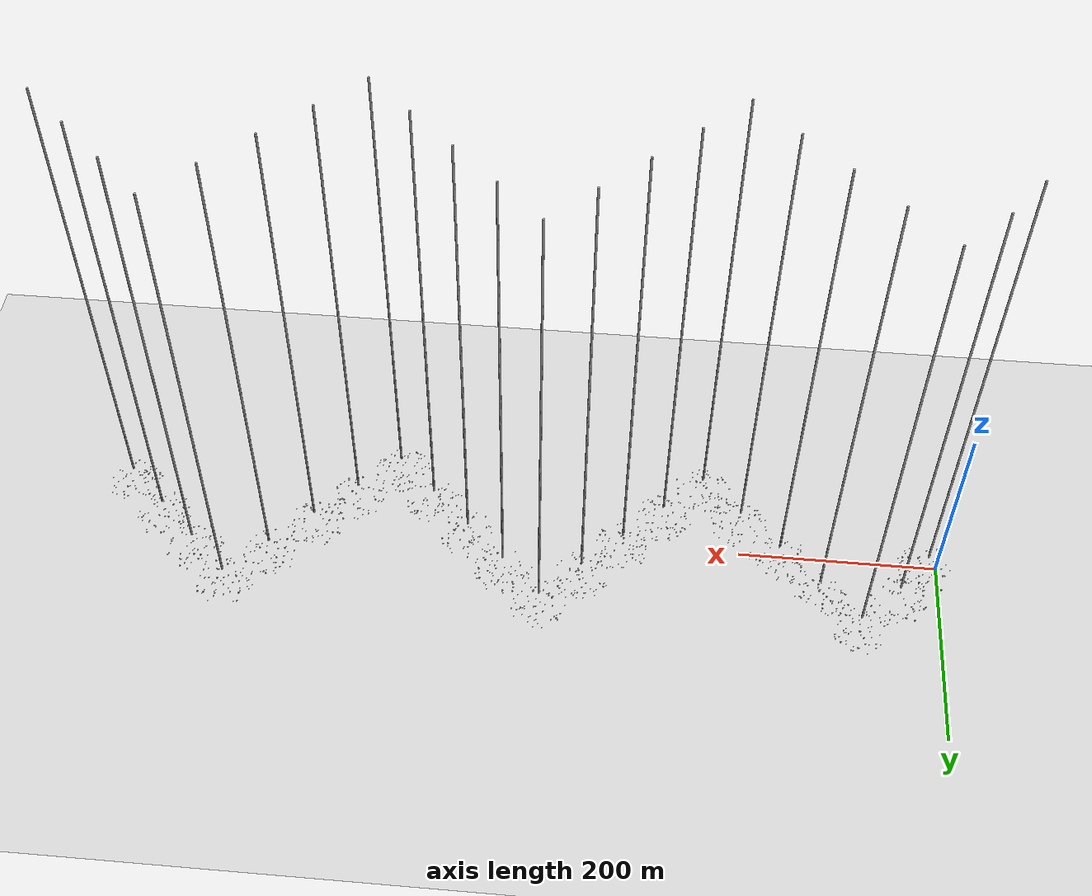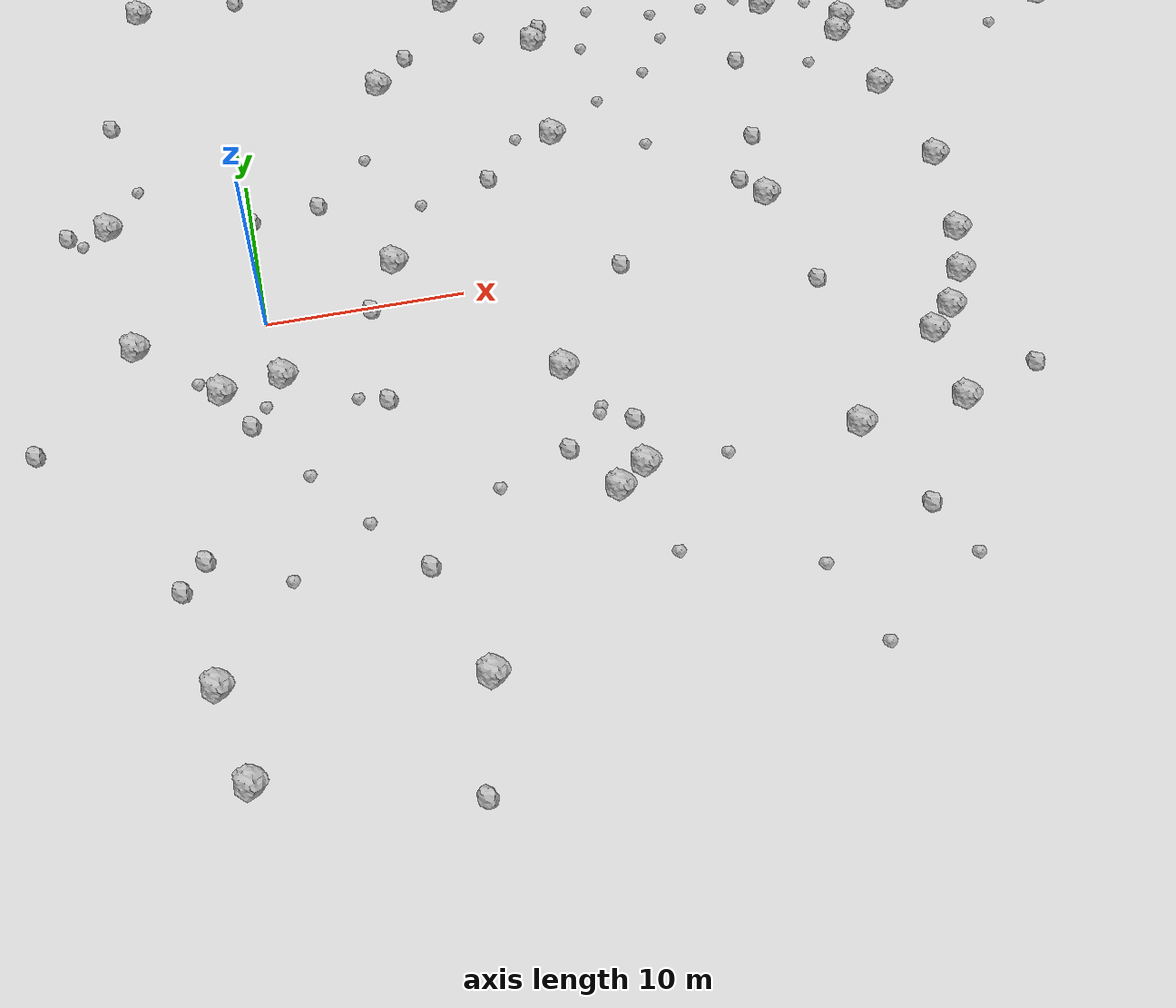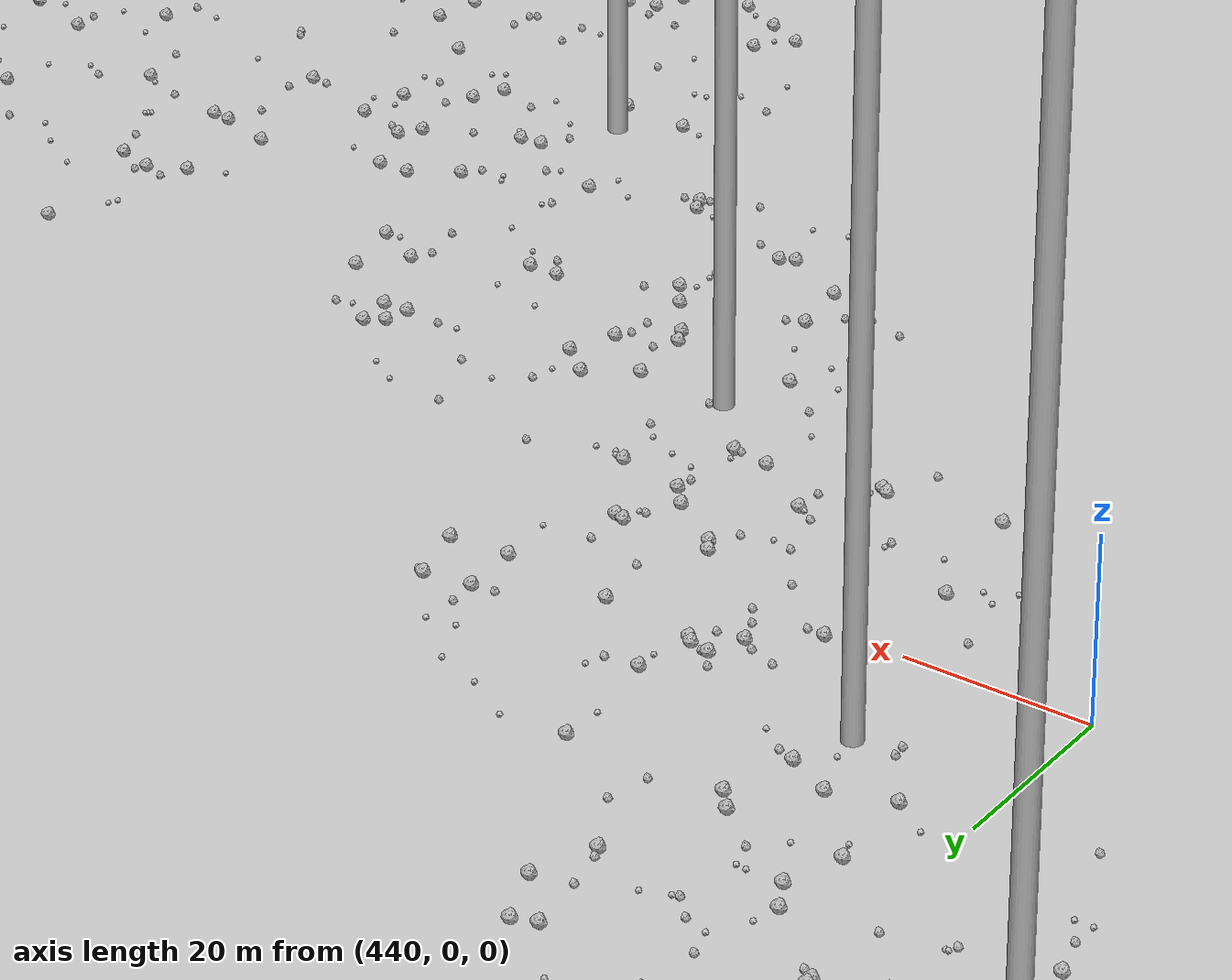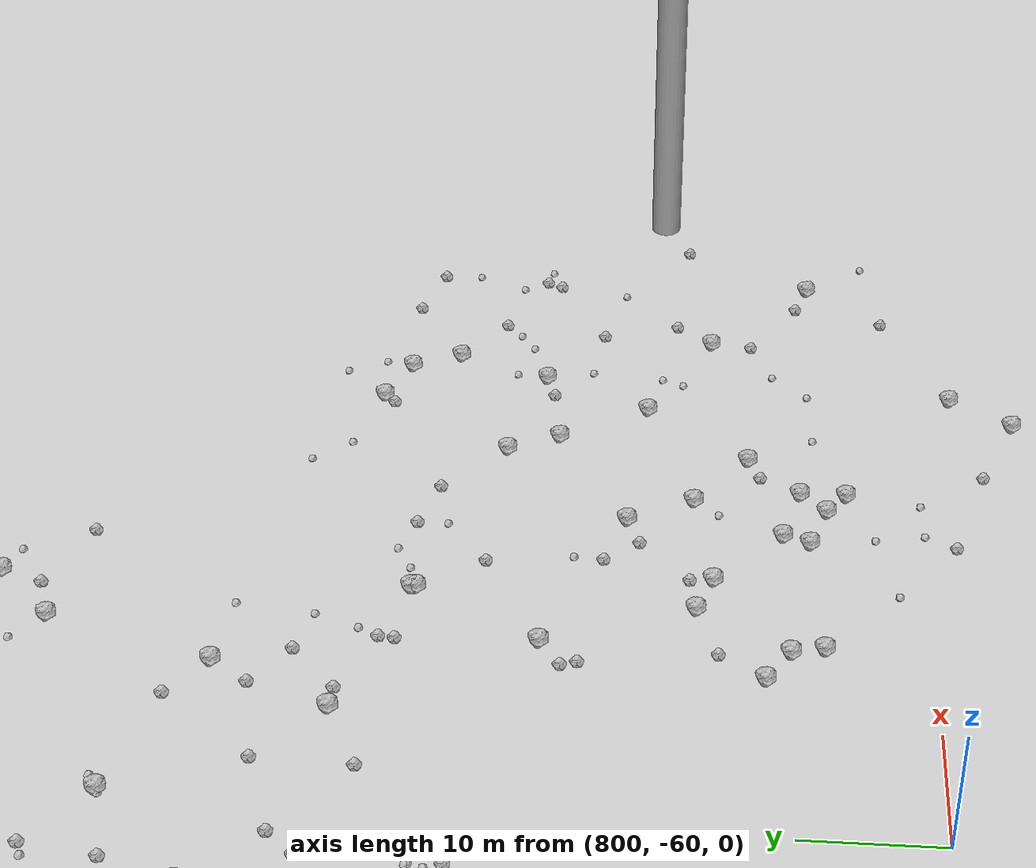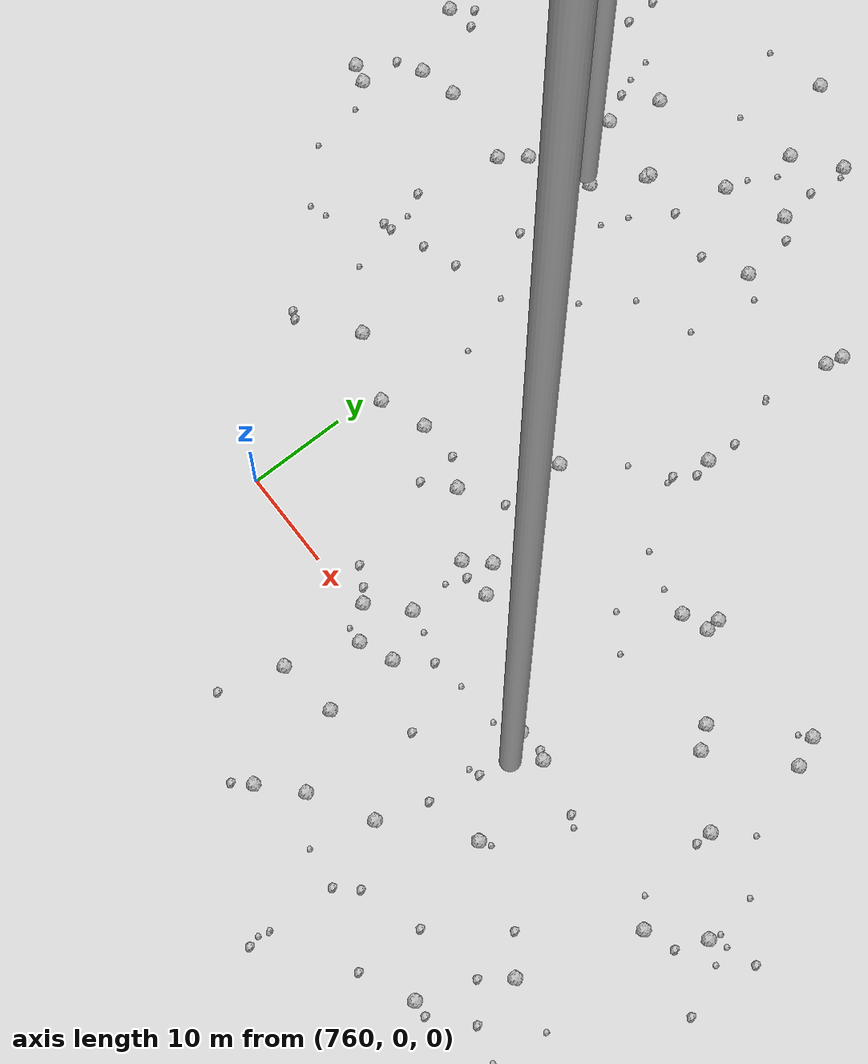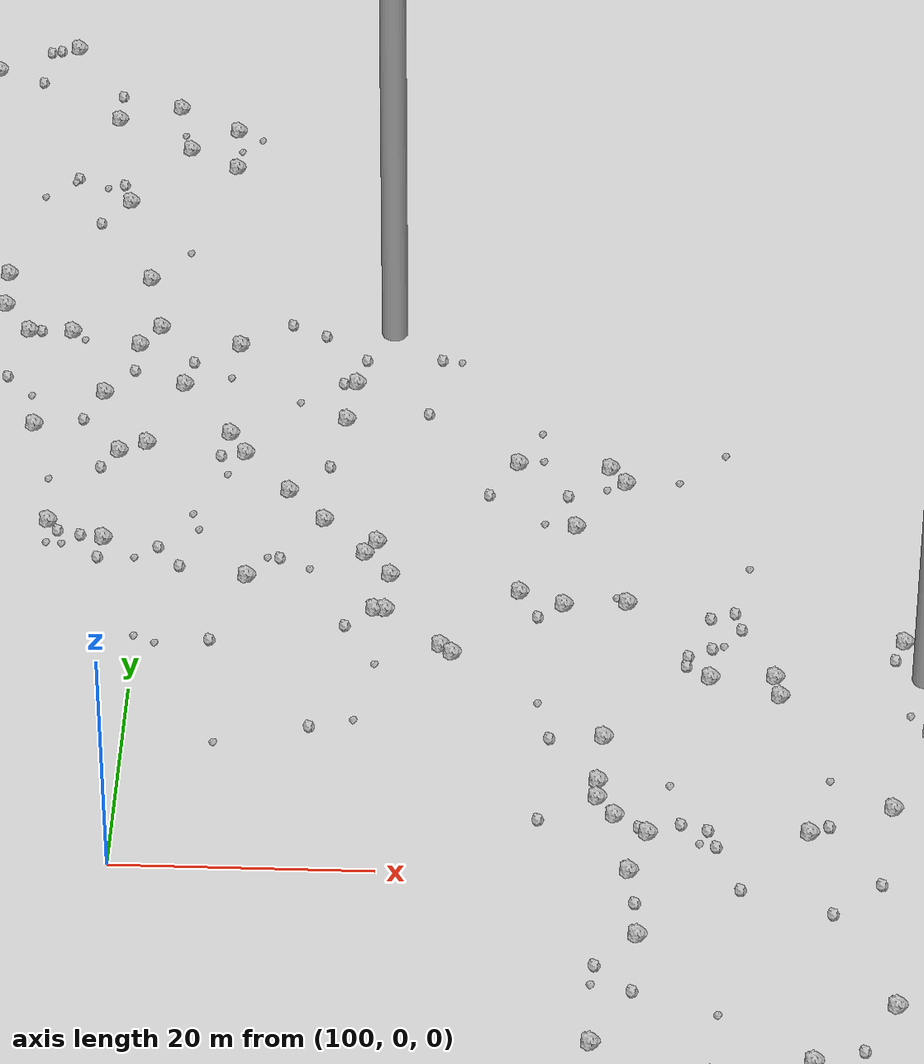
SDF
<sdf version="1.6">
 <world name="default">
  <include><uri>model://custom_ground</uri></include>
  <include><uri>model://sun</uri></include>
  <spherical_coordinates>
   <surface_model>EARTH_WGS84</surface_model>
   <latitude_deg>38.161479</latitude_deg>
   <longitude_deg>-122.454630</longitude_deg>
   <elevation>488.0</elevation>
   <heading_deg>90</heading_deg>
  </spherical_coordinates>
  <model name="rock1_0_0">
   <include><uri>model://rock1</uri><pose>-6.424930950970255 -0.587219061488998 0.5 0 0 0</pose></include>
  </model>
  <model name="rock1_0_1">
   <include><uri>model://rock1</uri><pose>0.4827601119100251 -3.8090856985313835 0.5 0 0 0</pose></include>
  </model>
  <model name="rock1_0_2">
   <include><uri>model://rock1</uri><pose>36.88775999359197 4.346876838986887 0.5 0 0 0</pose></include>
  </model>
  <model name="rock1_0_3">
   <include><uri>model://rock1</uri><pose>14.923049454195976 -13.80396306774842 0.5 0 0 0</pose></include>
  </model>
  <model name="rock1_0_4">
   <include><uri>model://rock1</uri><pose>16.887059671707675 10.390908326920261 0.5 0 0 0</pose></include>
  </model>
  <model name="rock1_0_5">
   <include><uri>model://rock1</uri><pose>8.138750803626664 16.44142675524393 0.5 0 0 0</pose></include>
  </model>
  <model name="rock1_0_6">
   <include><uri>model://rock1</uri><pose>13.911853286613521 -6.145931606272061 0.5 0 0 0</pose></include>
  </model>
  <model name="rock1_0_7">
   <include><uri>model://rock1</uri><pose>-4.143460547015906 -20.362375384908376 0.5 0 0 0</pose></include>
  </model>
  <model name="rock1_0_8">
   <include><uri>model://rock1</uri><pose>-3.2262482423043934 -25.13845869900265 0.5 0 0 0</pose></include>
  </model>
  <model name="rock1_0_9">
   <include><uri>model://rock1</uri><pose>6.906103817150765 2.608231383768441 0.5 0 0 0</pose></include>
  </model>
  <model name="rock1_0_10">
   <include><uri>model://rock1</uri><pose>27.049187201133932 3.336943743982914 0.5 0 0 0</pose></include>
  </model>
  <model name="rock1_0_11">
   <include><uri>model://rock1</uri><pose>26.960159791275785 -12.59698647021252 0.5 0 0 0</pose></include>
  </model>
  <model name="rock1_0_12">
   <include><uri>model://rock1</uri><pose>32.39070895929106 -7.7359565793915515 0.5 0 0 0</pose></include>
  </model>
  <model name="rock1_0_13">
   <include><uri>model://rock1</uri><pose>13.08126236878556 23.024323875420478 0.5 0 0 0</pose></include>
  </model>
  <model name="rock1_0_14">
   <include><uri>model://rock1</uri><pose>35.128662441814306 -4.126179838080205 0.5 0 0 0</pose></include>
  </model>
  <model name="rock1_0_15">
   <include><uri>model://rock1</uri><pose>16.388843395942907 -12.718197862610246 0.5 0 0 0</pose></include>
  </model>
  <model name="rock1_0_16">
   <include><uri>model://rock1</uri><pose>-7.296600861721473 8.082078696174172 0.5 0 0 0</pose></include>
  </model>
  <model name="rock1_0_17">
   <include><uri>model://rock1</uri><pose>-4.681012567768235 25.70677008234707 0.5 0 0 0</pose></include>
  </model>
  <model name="rock1_0_18">
   <include><uri>model://rock1</uri><pose>36.01405602124401 -1.2816330833552705 0.5 0 0 0</pose></include>
  </model>
  <model name="rock1_0_19">
   <include><uri>model://rock1</uri><pose>32.42811270994512 -12.105488435162709 0.5 0 0 0</pose></include>
  </model>
  <model name="rock1_0_20">
   <include><uri>model://rock1</uri><pose>33.806929551316706 -6.351853177204006 0.5 0 0 0</pose></include>
  </model>
  <model name="rock1_0_21">
   <include><uri>model://rock1</uri><pose>17.44617941107751 18.422138651616557 0.5 0 0 0</pose></include>
  </model>
  <model name="rock1_0_22">
   <include><uri>model://rock1</uri><pose>34.971879204956174 15.534540416273586 0.5 0 0 0</pose></include>
  </model>
  <model name="rock1_0_23">
   <include><uri>model://rock1</uri><pose>35.847326501902884 10.580018013693035 0.5 0 0 0</pose></include>
  </model>
  <model name="rock1_0_24">
   <include><uri>model://rock1</uri><pose>13.027638627756637 27.946789274651813 0.5 0 0 0</pose></include>
  </model>
  <model name="rock1_0_25">
   <include><uri>model://rock1</uri><pose>-2.507647725210937 -4.237533619354956 0.5 0 0 0</pose></include>
  </model>
  <model name="rock1_0_26">
   <include><uri>model://rock1</uri><pose>7.3377661946634625 -22.183354296081614 0.5 0 0 0</pose></include>
  </model>
  <model name="rock2_0_0">
   <include><uri>model://rock2</uri><pose>-4.121745442522933 -13.787380472383106 0.3 0 0 0</pose></include>
  </model>
  <model name="rock2_0_1">
   <include><uri>model://rock2</uri><pose>6.02727244789822 -27.691656911253133 0.3 0 0 0</pose></include>
  </model>
  <model name="rock2_0_2">
   <include><uri>model://rock2</uri><pose>5.643895941575003 -16.18768189136278 0.3 0 0 0</pose></include>
  </model>
  <model name="rock2_0_3">
   <include><uri>model://rock2</uri><pose>18.238238493033585 0.07173180588229755 0.3 0 0 0</pose></include>
  </model>
  <model name="rock2_0_4">
   <include><uri>model://rock2</uri><pose>3.6078879824832413 7.610764798383457 0.3 0 0 0</pose></include>
  </model>
  <model name="rock2_0_5">
   <include><uri>model://rock2</uri><pose>-15.186372700609452 5.87925003771295 0.3 0 0 0</pose></include>
  </model>
  <model name="rock2_0_6">
   <include><uri>model://rock2</uri><pose>16.504459766829108 -9.935552404733773 0.3 0 0 0</pose></include>
  </model>
  <model name="rock2_0_7">
   <include><uri>model://rock2</uri><pose>12.78260217597579 7.73079113643368 0.3 0 0 0</pose></include>
  </model>
  <model name="rock2_0_8">
   <include><uri>model://rock2</uri><pose>0.039705448453077 7.184080819439643 0.3 0 0 0</pose></include>
  </model>
  <model name="rock2_0_9">
   <include><uri>model://rock2</uri><pose>36.54334942712644 -10.65370863085327 0.3 0 0 0</pose></include>
  </model>
  <model name="rock2_0_10">
   <include><uri>model://rock2</uri><pose>27.597653816326684 8.040115236845125 0.3 0 0 0</pose></include>
  </model>
  <model name="rock2_0_11">
   <include><uri>model://rock2</uri><pose>-15.046654697180834 0.10346229742173918 0.3 0 0 0</pose></include>
  </model>
  <model name="rock2_0_12">
   <include><uri>model://rock2</uri><pose>-1.3454595727170044 -6.524952263800159 0.3 0 0 0</pose></include>
  </model>
  <model name="rock2_0_13">
   <include><uri>model://rock2</uri><pose>5.245549027416082 -6.27528653563828 0.3 0 0 0</pose></include>
  </model>
  <model name="rock2_0_14">
   <include><uri>model://rock2</uri><pose>-5.286193931160319 -15.205947305390694 0.3 0 0 0</pose></include>
  </model>
  <model name="rock2_0_15">
   <include><uri>model://rock2</uri><pose>28.641112922983126 -17.60046424606943 0.3 0 0 0</pose></include>
  </model>
  <model name="rock2_0_16">
   <include><uri>model://rock2</uri><pose>5.264321129621443 -0.3136881654027661 0.3 0 0 0</pose></include>
  </model>
  <model name="rock2_0_17">
   <include><uri>model://rock2</uri><pose>18.00236160064243 19.673171436700997 0.3 0 0 0</pose></include>
  </model>
  <model name="rock2_0_18">
   <include><uri>model://rock2</uri><pose>25.959879022906797 4.8422759221276195 0.3 0 0 0</pose></include>
  </model>
  <model name="rock2_0_19">
   <include><uri>model://rock2</uri><pose>-9.428198143826092 7.974403395505959 0.3 0 0 0</pose></include>
  </model>
  <model name="rock2_0_20">
   <include><uri>model://rock2</uri><pose>-6.799431593227098 16.081724157229836 0.3 0 0 0</pose></include>
  </model>
  <model name="rock2_0_21">
   <include><uri>model://rock2</uri><pose>9.94887941465078 18.61240090159602 0.3 0 0 0</pose></include>
  </model>
  <model name="rock2_0_22">
   <include><uri>model://rock2</uri><pose>18.074094186574 24.16056833041862 0.3 0 0 0</pose></include>
  </model>
  <model name="rock2_0_23">
   <include><uri>model://rock2</uri><pose>-11.388317694965211 -6.195728672452827 0.3 0 0 0</pose></include>
  </model>
  <model name="rock2_0_24">
   <include><uri>model://rock2</uri><pose>27.823754854013863 -3.0111221643475403 0.3 0 0 0</pose></include>
  </model>
  <model name="rock2_0_25">
   <include><uri>model://rock2</uri><pose>0.8898733755639938 25.777111683934173 0.3 0 0 0</pose></include>
  </model>
  <model name="rock2_0_26">
   <include><uri>model://rock2</uri><pose>13.080689797649228 -11.063708474578437 0.3 0 0 0</pose></include>
  </model>
  <model name="rock3_0_0">
   <include><uri>model://rock3</uri><pose>6.488434919068087 10.631520947523846 0.2 0 0 0</pose></include>
  </model>
  <model name="rock3_0_1">
   <include><uri>model://rock3</uri><pose>29.784587298323082 -20.63380957273997 0.2 0 0 0</pose></include>
  </model>
  <model name="rock3_0_2">
   <include><uri>model://rock3</uri><pose>14.445841882298659 19.550157781954475 0.2 0 0 0</pose></include>
  </model>
  <model name="rock3_0_3">
   <include><uri>model://rock3</uri><pose>20.330327477489178 -12.811855047368944 0.2 0 0 0</pose></include>
  </model>
  <model name="rock3_0_4">
   <include><uri>model://rock3</uri><pose>-0.43575194746698287 -15.672463894014507 0.2 0 0 0</pose></include>
  </model>
  <model name="rock3_0_5">
   <include><uri>model://rock3</uri><pose>23.021220149080612 14.557532408985587 0.2 0 0 0</pose></include>
  </model>
  <model name="rock3_0_6">
   <include><uri>model://rock3</uri><pose>21.738385684555894 8.68379241075872 0.2 0 0 0</pose></include>
  </model>
  <model name="rock3_0_7">
   <include><uri>model://rock3</uri><pose>3.8353257977112634 -5.90171158971166 0.2 0 0 0</pose></include>
  </model>
  <model name="rock3_0_8">
   <include><uri>model://rock3</uri><pose>14.82097568700263 10.517911142520376 0.2 0 0 0</pose></include>
  </model>
  <model name="rock3_0_9">
   <include><uri>model://rock3</uri><pose>19.92394835274196 12.666558596376184 0.2 0 0 0</pose></include>
  </model>
  <model name="rock3_0_10">
   <include><uri>model://rock3</uri><pose>14.966993434874212 -9.279859984470207 0.2 0 0 0</pose></include>
  </model>
  <model name="rock3_0_11">
   <include><uri>model://rock3</uri><pose>24.339732634928232 -24.18660334233016 0.2 0 0 0</pose></include>
  </model>
  <model name="rock3_0_12">
   <include><uri>model://rock3</uri><pose>22.890793022231072 -19.773272631332965 0.2 0 0 0</pose></include>
  </model>
  <model name="rock3_0_13">
   <include><uri>model://rock3</uri><pose>-5.6812917144487685 10.7218506217801 0.2 0 0 0</pose></include>
  </model>
  <model name="rock3_0_14">
   <include><uri>model://rock3</uri><pose>9.477431022400435 -12.596574786586253 0.2 0 0 0</pose></include>
  </model>
  <model name="rock3_0_15">
   <include><uri>model://rock3</uri><pose>20.022412290563082 17.33206077068545 0.2 0 0 0</pose></include>
  </model>
  <model name="rock3_0_16">
   <include><uri>model://rock3</uri><pose>16.65332013705364 -17.74248876391136 0.2 0 0 0</pose></include>
  </model>
  <model name="rock3_0_17">
   <include><uri>model://rock3</uri><pose>1.0035197009831727 -10.024429072979736 0.2 0 0 0</pose></include>
  </model>
  <model name="rock3_0_18">
   <include><uri>model://rock3</uri><pose>-3.6121050912636186 -3.367374369408836 0.2 0 0 0</pose></include>
  </model>
  <model name="rock3_0_19">
   <include><uri>model://rock3</uri><pose>-7.014481069307514 8.570208155446565 0.2 0 0 0</pose></include>
  </model>
  <model name="rock3_0_20">
   <include><uri>model://rock3</uri><pose>3.3342125044127933 -13.289884075950937 0.2 0 0 0</pose></include>
  </model>
  <model name="rock3_0_21">
   <include><uri>model://rock3</uri><pose>-0.5556876973498746 -5.498297088017775 0.2 0 0 0</pose></include>
  </model>
  <model name="rock3_0_22">
   <include><uri>model://rock3</uri><pose>21.09589339933811 20.573079447945886 0.2 0 0 0</pose></include>
  </model>
  <model name="rock3_0_23">
   <include><uri>model://rock3</uri><pose>15.142183269325194 -8.84426443397843 0.2 0 0 0</pose></include>
  </model>
  <model name="rock3_0_24">
   <include><uri>model://rock3</uri><pose>32.56411310183095 13.374693724547868 0.2 0 0 0</pose></include>
  </model>
  <model name="rock3_0_25">
   <include><uri>model://rock3</uri><pose>8.933583390641175 6.538434013395914 0.2 0 0 0</pose></include>
  </model>
  <model name="rock3_0_26">
   <include><uri>model://rock3</uri><pose>-8.70610887085024 7.221260666325911 0.2 0 0 0</pose></include>
  </model>
  <model name="rock1_1_0">
   <include><uri>model://rock1</uri><pose>68.86400824875136 34.069561577146864 0.5 0 0 0</pose></include>
  </model>
  <model name="rock1_1_1">
   <include><uri>model://rock1</uri><pose>47.76727453801469 16.301111077668864 0.5 0 0 0</pose></include>
  </model>
  <model name="rock1_1_2">
   <include><uri>model://rock1</uri><pose>39.307524957477895 20.166772092633213 0.5 0 0 0</pose></include>
  </model>
  <model name="rock1_1_3">
   <include><uri>model://rock1</uri><pose>12.25192965902502 48.62252861232169 0.5 0 0 0</pose></include>
  </model>
  <model name="rock1_1_4">
   <include><uri>model://rock1</uri><pose>24.1384607675775 65.41065434113244 0.5 0 0 0</pose></include>
  </model>
  <model name="rock1_1_5">
   <include><uri>model://rock1</uri><pose>31.362173406228475 18.846947253304254 0.5 0 0 0</pose></include>
  </model>
  <model name="rock1_1_6">
   <include><uri>model://rock1</uri><pose>36.712903762459575 32.59069409378657 0.5 0 0 0</pose></include>
  </model>
  <model name="rock1_1_7">
   <include><uri>model://rock1</uri><pose>35.63601293424438 16.82782876853642 0.5 0 0 0</pose></include>
  </model>
  <model name="rock1_1_8">
   <include><uri>model://rock1</uri><pose>32.42145707912561 47.06792660704034 0.5 0 0 0</pose></include>
  </model>
  <model name="rock1_1_9">
   <include><uri>model://rock1</uri><pose>14.0138161283147 28.420684449015546 0.5 0 0 0</pose></include>
  </model>
  <model name="rock1_1_10">
   <include><uri>model://rock1</uri><pose>66.64592380735658 51.72776656924366 0.5 0 0 0</pose></include>
  </model>
  <model name="rock1_1_11">
   <include><uri>model://rock1</uri><pose>21.501550237080544 31.85731170200114 0.5 0 0 0</pose></include>
  </model>
  <model name="rock1_1_12">
   <include><uri>model://rock1</uri><pose>69.3592806542197 41.37176553652843 0.5 0 0 0</pose></include>
  </model>
  <model name="rock1_1_13">
   <include><uri>model://rock1</uri><pose>46.66328442988543 60.1256761875151 0.5 0 0 0</pose></include>
  </model>
  <model name="rock1_1_14">
   <include><uri>model://rock1</uri><pose>53.93014024186871 27.223100498850044 0.5 0 0 0</pose></include>
  </model>
  <model name="rock1_1_15">
   <include><uri>model://rock1</uri><pose>32.82161994447237 63.00066519148471 0.5 0 0 0</pose></include>
  </model>
  <model name="rock1_1_16">
   <include><uri>model://rock1</uri><pose>48.68135680397333 56.74840208029302 0.5 0 0 0</pose></include>
  </model>
  <model name="rock1_1_17">
   <include><uri>model://rock1</uri><pose>49.22944939027209 66.9276588976235 0.5 0 0 0</pose></include>
  </model>
  <model name="rock1_1_18">
   <include><uri>model://rock1</uri><pose>39.37794371454307 17.611837074297853 0.5 0 0 0</pose></include>
  </model>
  <model name="rock1_1_19">
   <include><uri>model://rock1</uri><pose>32.03007947076384 63.56696581666155 0.5 0 0 0</pose></include>
  </model>
  <model name="rock1_1_20">
   <include><uri>model://rock1</uri><pose>14.017041576867552 34.345239105403394 0.5 0 0 0</pose></include>
  </model>
  <model name="rock1_1_21">
   <include><uri>model://rock1</uri><pose>45.10751432949657 34.317494436734805 0.5 0 0 0</pose></include>
  </model>
  <model name="rock1_1_22">
   <include><uri>model://rock1</uri><pose>39.39979206157596 33.768766892385976 0.5 0 0 0</pose></include>
  </model>
  <model name="rock1_1_23">
   <include><uri>model://rock1</uri><pose>44.16931207349062 61.03408871182704 0.5 0 0 0</pose></include>
  </model>
  <model name="rock1_1_24">
   <include><uri>model://rock1</uri><pose>14.343172167880386 50.82239631679361 0.5 0 0 0</pose></include>
  </model>
  <model name="rock1_1_25">
   <include><uri>model://rock1</uri><pose>66.37922184561405 38.32744686083102 0.5 0 0 0</pose></include>
  </model>
  <model name="rock1_1_26">
   <include><uri>model://rock1</uri><pose>25.164872008846746 51.90851550639208 0.5 0 0 0</pose></include>
  </model>
  <model name="rock2_1_0">
   <include><uri>model://rock2</uri><pose>48.640294364961264 57.98479991134535 0.3 0 0 0</pose></include>
  </model>
  <model name="rock2_1_1">
   <include><uri>model://rock2</uri><pose>41.73150551148905 20.429236757302693 0.3 0 0 0</pose></include>
  </model>
  <model name="rock2_1_2">
   <include><uri>model://rock2</uri><pose>22.94250202202356 44.88716144217826 0.3 0 0 0</pose></include>
  </model>
  <model name="rock2_1_3">
   <include><uri>model://rock2</uri><pose>17.40617673575063 47.94629809114059 0.3 0 0 0</pose></include>
  </model>
  <model name="rock2_1_4">
   <include><uri>model://rock2</uri><pose>19.343848726636672 29.655591789775112 0.3 0 0 0</pose></include>
  </model>
  <model name="rock2_1_5">
   <include><uri>model://rock2</uri><pose>43.09918546543366 31.20502744012552 0.3 0 0 0</pose></include>
  </model>
  <model name="rock2_1_6">
   <include><uri>model://rock2</uri><pose>28.483775485347266 14.38035765847269 0.3 0 0 0</pose></include>
  </model>
  <model name="rock2_1_7">
   <include><uri>model://rock2</uri><pose>57.92246953744937 16.69668491729915 0.3 0 0 0</pose></include>
  </model>
  <model name="rock2_1_8">
   <include><uri>model://rock2</uri><pose>19.309858176497684 55.03103817009988 0.3 0 0 0</pose></include>
  </model>
  <model name="rock2_1_9">
   <include><uri>model://rock2</uri><pose>20.071693481285166 41.838799401142694 0.3 0 0 0</pose></include>
  </model>
  <model name="rock2_1_10">
   <include><uri>model://rock2</uri><pose>23.973005197392474 53.87337488748569 0.3 0 0 0</pose></include>
  </model>
  <model name="rock2_1_11">
   <include><uri>model://rock2</uri><pose>40.840126401553135 59.33654245350004 0.3 0 0 0</pose></include>
  </model>
  <model name="rock2_1_12">
   <include><uri>model://rock2</uri><pose>19.056911810131233 37.93129698353749 0.3 0 0 0</pose></include>
  </model>
  <model name="rock2_1_13">
   <include><uri>model://rock2</uri><pose>26.417901609614496 49.00611412423889 0.3 0 0 0</pose></include>
  </model>
  <model name="rock2_1_14">
   <include><uri>model://rock2</uri><pose>17.888970761415397 47.58173238089485 0.3 0 0 0</pose></include>
  </model>
  <model name="rock2_1_15">
   <include><uri>model://rock2</uri><pose>52.96544596551863 61.66029076767362 0.3 0 0 0</pose></include>
  </model>
  <model name="rock2_1_16">
   <include><uri>model://rock2</uri><pose>58.33896861177955 49.7196680912585 0.3 0 0 0</pose></include>
  </model>
  <model name="rock2_1_17">
   <include><uri>model://rock2</uri><pose>49.17327664041617 29.357569081593947 0.3 0 0 0</pose></include>
  </model>
  <model name="rock2_1_18">
   <include><uri>model://rock2</uri><pose>30.025900195864697 55.966741448104735 0.3 0 0 0</pose></include>
  </model>
  <model name="rock2_1_19">
   <include><uri>model://rock2</uri><pose>54.419709947834626 31.86803435568143 0.3 0 0 0</pose></include>
  </model>
  <model name="rock2_1_20">
   <include><uri>model://rock2</uri><pose>43.906023957821354 32.44726054705613 0.3 0 0 0</pose></include>
  </model>
  <model name="rock2_1_21">
   <include><uri>model://rock2</uri><pose>47.265599835076664 31.2786257067672 0.3 0 0 0</pose></include>
  </model>
  <model name="rock2_1_22">
   <include><uri>model://rock2</uri><pose>33.7980869371558 39.86746045489761 0.3 0 0 0</pose></include>
  </model>
  <model name="rock2_1_23">
   <include><uri>model://rock2</uri><pose>29.26982362636847 53.8849251603022 0.3 0 0 0</pose></include>
  </model>
  <model name="rock2_1_24">
   <include><uri>model://rock2</uri><pose>31.280950153362664 18.993381624155454 0.3 0 0 0</pose></include>
  </model>
  <model name="rock2_1_25">
   <include><uri>model://rock2</uri><pose>16.082450077491266 39.85834736066114 0.3 0 0 0</pose></include>
  </model>
  <model name="rock2_1_26">
   <include><uri>model://rock2</uri><pose>31.455537040256115 59.94459865024909 0.3 0 0 0</pose></include>
  </model>
  <model name="rock3_1_0">
   <include><uri>model://rock3</uri><pose>14.649591270976941 32.20339435070779 0.2 0 0 0</pose></include>
  </model>
  <model name="rock3_1_1">
   <include><uri>model://rock3</uri><pose>24.653460287906828 55.098528380883515 0.2 0 0 0</pose></include>
  </model>
  <model name="rock3_1_2">
   <include><uri>model://rock3</uri><pose>24.70421965234873 19.501588446853283 0.2 0 0 0</pose></include>
  </model>
  <model name="rock3_1_3">
   <include><uri>model://rock3</uri><pose>35.727546558243375 63.8027740287834 0.2 0 0 0</pose></include>
  </model>
  <model name="rock3_1_4">
   <include><uri>model://rock3</uri><pose>18.477515172913712 52.29972186196373 0.2 0 0 0</pose></include>
  </model>
  <model name="rock3_1_5">
   <include><uri>model://rock3</uri><pose>23.518045263652443 28.435227504742947 0.2 0 0 0</pose></include>
  </model>
  <model name="rock3_1_6">
   <include><uri>model://rock3</uri><pose>50.85685318826802 31.33116748109157 0.2 0 0 0</pose></include>
  </model>
  <model name="rock3_1_7">
   <include><uri>model://rock3</uri><pose>41.87262412291042 69.2804891500979 0.2 0 0 0</pose></include>
  </model>
  <model name="rock3_1_8">
   <include><uri>model://rock3</uri><pose>20.448494606856364 26.468353548597257 0.2 0 0 0</pose></include>
  </model>
  <model name="rock3_1_9">
   <include><uri>model://rock3</uri><pose>33.94860567154677 18.642394246215083 0.2 0 0 0</pose></include>
  </model>
  <model name="rock3_1_10">
   <include><uri>model://rock3</uri><pose>16.32177352260637 25.81452106981093 0.2 0 0 0</pose></include>
  </model>
  <model name="rock3_1_11">
   <include><uri>model://rock3</uri><pose>47.147926161493814 31.820914945436304 0.2 0 0 0</pose></include>
  </model>
  <model name="rock3_1_12">
   <include><uri>model://rock3</uri><pose>30.48855622446746 58.6871440944852 0.2 0 0 0</pose></include>
  </model>
  <model name="rock3_1_13">
   <include><uri>model://rock3</uri><pose>42.30782355050064 19.124907351252638 0.2 0 0 0</pose></include>
  </model>
  <model name="rock3_1_14">
   <include><uri>model://rock3</uri><pose>29.899841083797263 19.792006652210084 0.2 0 0 0</pose></include>
  </model>
  <model name="rock3_1_15">
   <include><uri>model://rock3</uri><pose>11.670895632417606 37.17532811673388 0.2 0 0 0</pose></include>
  </model>
  <model name="rock3_1_16">
   <include><uri>model://rock3</uri><pose>43.988535589170986 14.593782776329508 0.2 0 0 0</pose></include>
  </model>
  <model name="rock3_1_17">
   <include><uri>model://rock3</uri><pose>18.584089532501334 41.5981568858879 0.2 0 0 0</pose></include>
  </model>
  <model name="rock3_1_18">
   <include><uri>model://rock3</uri><pose>34.87547244171421 37.466604583013414 0.2 0 0 0</pose></include>
  </model>
  <model name="rock3_1_19">
   <include><uri>model://rock3</uri><pose>62.44300239596396 42.406115712777186 0.2 0 0 0</pose></include>
  </model>
  <model name="rock3_1_20">
   <include><uri>model://rock3</uri><pose>32.89113423056774 50.27698131500383 0.2 0 0 0</pose></include>
  </model>
  <model name="rock3_1_21">
   <include><uri>model://rock3</uri><pose>46.65800733042068 67.18949500180744 0.2 0 0 0</pose></include>
  </model>
  <model name="rock3_1_22">
   <include><uri>model://rock3</uri><pose>38.924265215991625 21.897731752279405 0.2 0 0 0</pose></include>
  </model>
  <model name="rock3_1_23">
   <include><uri>model://rock3</uri><pose>44.09924169416429 43.45665431539084 0.2 0 0 0</pose></include>
  </model>
  <model name="rock3_1_24">
   <include><uri>model://rock3</uri><pose>24.767966249720672 17.285736600774428 0.2 0 0 0</pose></include>
  </model>
  <model name="rock3_1_25">
   <include><uri>model://rock3</uri><pose>27.75801036136507 19.40350497631123 0.2 0 0 0</pose></include>
  </model>
  <model name="rock3_1_26">
   <include><uri>model://rock3</uri><pose>17.97611248884063 42.11274602030927 0.2 0 0 0</pose></include>
  </model>
  <model name="rock1_2_0">
   <include><uri>model://rock1</uri><pose>79.41806116971962 83.3934203010386 0.5 0 0 0</pose></include>
  </model>
  <model name="rock1_2_1">
   <include><uri>model://rock1</uri><pose>97.86971181934406 72.60991442903857 0.5 0 0 0</pose></include>
  </model>
  <model name="rock1_2_2">
   <include><uri>model://rock1</uri><pose>82.0208038972247 103.33051081775979 0.5 0 0 0</pose></include>
  </model>
  <model name="rock1_2_3">
   <include><uri>model://rock1</uri><pose>104.16541234798044 89.03815988205253 0.5 0 0 0</pose></include>
  </model>
  <model name="rock1_2_4">
   <include><uri>model://rock1</uri><pose>85.88858045237441 68.63042145809939 0.5 0 0 0</pose></include>
  </model>
  <model name="rock1_2_5">
   <include><uri>model://rock1</uri><pose>99.97297356373002 91.65801916876791 0.5 0 0 0</pose></include>
  </model>
  <model name="rock1_2_6">
   <include><uri>model://rock1</uri><pose>89.7206676595926 52.44787833639492 0.5 0 0 0</pose></include>
  </model>
  <model name="rock1_2_7">
   <include><uri>model://rock1</uri><pose>85.75728733444484 72.95778067863463 0.5 0 0 0</pose></include>
  </model>
  <model name="rock1_2_8">
   <include><uri>model://rock1</uri><pose>71.7177020706958 59.330907991074774 0.5 0 0 0</pose></include>
  </model>
  <model name="rock1_2_9">
   <include><uri>model://rock1</uri><pose>98.67666447287488 97.88693595773933 0.5 0 0 0</pose></include>
  </model>
  <model name="rock1_2_10">
   <include><uri>model://rock1</uri><pose>93.3488914843692 95.99606980602505 0.5 0 0 0</pose></include>
  </model>
  <model name="rock1_2_11">
   <include><uri>model://rock1</uri><pose>91.84421367055356 65.07394770145476 0.5 0 0 0</pose></include>
  </model>
  <model name="rock1_2_12">
   <include><uri>model://rock1</uri><pose>95.19300187458828 56.8638340151752 0.5 0 0 0</pose></include>
  </model>
  <model name="rock1_2_13">
   <include><uri>model://rock1</uri><pose>97.6083613324156 63.44105975809035 0.5 0 0 0</pose></include>
  </model>
  <model name="rock1_2_14">
   <include><uri>model://rock1</uri><pose>88.17964375318743 65.09526553463358 0.5 0 0 0</pose></include>
  </model>
  <model name="rock1_2_15">
   <include><uri>model://rock1</uri><pose>99.23664109573318 65.91445732943802 0.5 0 0 0</pose></include>
  </model>
  <model name="rock1_2_16">
   <include><uri>model://rock1</uri><pose>71.79358750984139 62.73750135741842 0.5 0 0 0</pose></include>
  </model>
  <model name="rock1_2_17">
   <include><uri>model://rock1</uri><pose>54.69390823666608 74.93619056602854 0.5 0 0 0</pose></include>
  </model>
  <model name="rock1_2_18">
   <include><uri>model://rock1</uri><pose>58.145458324760824 70.37689129095511 0.5 0 0 0</pose></include>
  </model>
  <model name="rock1_2_19">
   <include><uri>model://rock1</uri><pose>63.60823169164469 58.94974476166995 0.5 0 0 0</pose></include>
  </model>
  <model name="rock1_2_20">
   <include><uri>model://rock1</uri><pose>88.81014596007373 106.91441736648628 0.5 0 0 0</pose></include>
  </model>
  <model name="rock1_2_21">
   <include><uri>model://rock1</uri><pose>95.2836445915184 83.72167012446073 0.5 0 0 0</pose></include>
  </model>
  <model name="rock1_2_22">
   <include><uri>model://rock1</uri><pose>51.44399814251174 72.44360223512606 0.5 0 0 0</pose></include>
  </model>
  <model name="rock1_2_23">
   <include><uri>model://rock1</uri><pose>63.70288500454729 97.22384497377831 0.5 0 0 0</pose></include>
  </model>
  <model name="rock1_2_24">
   <include><uri>model://rock1</uri><pose>103.93116772685345 94.55413795804989 0.5 0 0 0</pose></include>
  </model>
  <model name="rock1_2_25">
   <include><uri>model://rock1</uri><pose>74.26813642231497 97.83006381976489 0.5 0 0 0</pose></include>
  </model>
  <model name="rock1_2_26">
   <include><uri>model://rock1</uri><pose>64.11906567534669 101.9414562830629 0.5 0 0 0</pose></include>
  </model>
  <model name="rock2_2_0">
   <include><uri>model://rock2</uri><pose>78.48366940487772 87.17144734257533 0.3 0 0 0</pose></include>
  </model>
  <model name="rock2_2_1">
   <include><uri>model://rock2</uri><pose>78.73428356013947 74.41655164253083 0.3 0 0 0</pose></include>
  </model>
  <model name="rock2_2_2">
   <include><uri>model://rock2</uri><pose>87.27142736108172 106.66589846088165 0.3 0 0 0</pose></include>
  </model>
  <model name="rock2_2_3">
   <include><uri>model://rock2</uri><pose>75.69143068831247 91.3414567302299 0.3 0 0 0</pose></include>
  </model>
  <model name="rock2_2_4">
   <include><uri>model://rock2</uri><pose>90.50282603589233 87.24170243327096 0.3 0 0 0</pose></include>
  </model>
  <model name="rock2_2_5">
   <include><uri>model://rock2</uri><pose>59.273486406561275 97.24444462667704 0.3 0 0 0</pose></include>
  </model>
  <model name="rock2_2_6">
   <include><uri>model://rock2</uri><pose>67.80497548432326 69.26211264754812 0.3 0 0 0</pose></include>
  </model>
  <model name="rock2_2_7">
   <include><uri>model://rock2</uri><pose>69.4034749871795 82.39562042827008 0.3 0 0 0</pose></include>
  </model>
  <model name="rock2_2_8">
   <include><uri>model://rock2</uri><pose>93.34326886894829 99.73583880694791 0.3 0 0 0</pose></include>
  </model>
  <model name="rock2_2_9">
   <include><uri>model://rock2</uri><pose>102.28349013839161 61.35659133888959 0.3 0 0 0</pose></include>
  </model>
  <model name="rock2_2_10">
   <include><uri>model://rock2</uri><pose>72.990553242999 109.11858195731696 0.3 0 0 0</pose></include>
  </model>
  <model name="rock2_2_11">
   <include><uri>model://rock2</uri><pose>86.41263991114931 106.3968105509561 0.3 0 0 0</pose></include>
  </model>
  <model name="rock2_2_12">
   <include><uri>model://rock2</uri><pose>84.2505958012359 56.281394239745765 0.3 0 0 0</pose></include>
  </model>
  <model name="rock2_2_13">
   <include><uri>model://rock2</uri><pose>70.91017199997069 98.1927979908713 0.3 0 0 0</pose></include>
  </model>
  <model name="rock2_2_14">
   <include><uri>model://rock2</uri><pose>67.28040893428795 76.56871900819763 0.3 0 0 0</pose></include>
  </model>
  <model name="rock2_2_15">
   <include><uri>model://rock2</uri><pose>70.66917992024258 78.17676597075796 0.3 0 0 0</pose></include>
  </model>
  <model name="rock2_2_16">
   <include><uri>model://rock2</uri><pose>97.45934741552914 60.071616575548205 0.3 0 0 0</pose></include>
  </model>
  <model name="rock2_2_17">
   <include><uri>model://rock2</uri><pose>53.92655396346496 75.06154678780004 0.3 0 0 0</pose></include>
  </model>
  <model name="rock2_2_18">
   <include><uri>model://rock2</uri><pose>86.09624698401359 101.6801289186573 0.3 0 0 0</pose></include>
  </model>
  <model name="rock2_2_19">
   <include><uri>model://rock2</uri><pose>94.52886957764404 86.34472262053893 0.3 0 0 0</pose></include>
  </model>
  <model name="rock2_2_20">
   <include><uri>model://rock2</uri><pose>89.22241094671361 65.27551417710399 0.3 0 0 0</pose></include>
  </model>
  <model name="rock2_2_21">
   <include><uri>model://rock2</uri><pose>92.96885472034596 80.66511711141848 0.3 0 0 0</pose></include>
  </model>
  <model name="rock2_2_22">
   <include><uri>model://rock2</uri><pose>52.52284990023136 82.84504902642138 0.3 0 0 0</pose></include>
  </model>
  <model name="rock2_2_23">
   <include><uri>model://rock2</uri><pose>93.70253912610224 53.409743957222034 0.3 0 0 0</pose></include>
  </model>
  <model name="rock2_2_24">
   <include><uri>model://rock2</uri><pose>86.91622921360738 58.97478298186226 0.3 0 0 0</pose></include>
  </model>
  <model name="rock2_2_25">
   <include><uri>model://rock2</uri><pose>73.57872437289278 55.00581283242092 0.3 0 0 0</pose></include>
  </model>
  <model name="rock2_2_26">
   <include><uri>model://rock2</uri><pose>59.628497797631546 86.01977810686331 0.3 0 0 0</pose></include>
  </model>
  <model name="rock3_2_0">
   <include><uri>model://rock3</uri><pose>90.22481312842226 86.71023310703683 0.2 0 0 0</pose></include>
  </model>
  <model name="rock3_2_1">
   <include><uri>model://rock3</uri><pose>78.32617967801447 52.09871925155312 0.2 0 0 0</pose></include>
  </model>
  <model name="rock3_2_2">
   <include><uri>model://rock3</uri><pose>58.56058272105757 64.73014524487715 0.2 0 0 0</pose></include>
  </model>
  <model name="rock3_2_3">
   <include><uri>model://rock3</uri><pose>67.94800631399283 89.34710548996773 0.2 0 0 0</pose></include>
  </model>
  <model name="rock3_2_4">
   <include><uri>model://rock3</uri><pose>78.91186622537917 63.67528195202695 0.2 0 0 0</pose></include>
  </model>
  <model name="rock3_2_5">
   <include><uri>model://rock3</uri><pose>100.95361328363222 76.69548683975276 0.2 0 0 0</pose></include>
  </model>
  <model name="rock3_2_6">
   <include><uri>model://rock3</uri><pose>69.18634489269024 64.11837777975263 0.2 0 0 0</pose></include>
  </model>
  <model name="rock3_2_7">
   <include><uri>model://rock3</uri><pose>93.08600980881255 85.9204568969991 0.2 0 0 0</pose></include>
  </model>
  <model name="rock3_2_8">
   <include><uri>model://rock3</uri><pose>53.758480788966764 68.68208329457937 0.2 0 0 0</pose></include>
  </model>
  <model name="rock3_2_9">
   <include><uri>model://rock3</uri><pose>87.78603918675356 84.46664617521915 0.2 0 0 0</pose></include>
  </model>
  <model name="rock3_2_10">
   <include><uri>model://rock3</uri><pose>92.9124030884087 64.25819041780619 0.2 0 0 0</pose></include>
  </model>
  <model name="rock3_2_11">
   <include><uri>model://rock3</uri><pose>51.18360941437066 86.53666947991525 0.2 0 0 0</pose></include>
  </model>
  <model name="rock3_2_12">
   <include><uri>model://rock3</uri><pose>58.691442366488594 93.76039688589921 0.2 0 0 0</pose></include>
  </model>
  <model name="rock3_2_13">
   <include><uri>model://rock3</uri><pose>89.14067118238766 56.51150601876317 0.2 0 0 0</pose></include>
  </model>
  <model name="rock3_2_14">
   <include><uri>model://rock3</uri><pose>80.81741068869047 103.34883636521214 0.2 0 0 0</pose></include>
  </model>
  <model name="rock3_2_15">
   <include><uri>model://rock3</uri><pose>75.074622870784 90.22162864312536 0.2 0 0 0</pose></include>
  </model>
  <model name="rock3_2_16">
   <include><uri>model://rock3</uri><pose>78.43700931217431 83.67756932788464 0.2 0 0 0</pose></include>
  </model>
  <model name="rock3_2_17">
   <include><uri>model://rock3</uri><pose>64.24189392763985 56.03785229023912 0.2 0 0 0</pose></include>
  </model>
  <model name="rock3_2_18">
   <include><uri>model://rock3</uri><pose>84.29843983512374 53.68957291848625 0.2 0 0 0</pose></include>
  </model>
  <model name="rock3_2_19">
   <include><uri>model://rock3</uri><pose>64.9288189101531 66.53999926948832 0.2 0 0 0</pose></include>
  </model>
  <model name="rock3_2_20">
   <include><uri>model://rock3</uri><pose>99.29705948608324 94.0001382064793 0.2 0 0 0</pose></include>
  </model>
  <model name="rock3_2_21">
   <include><uri>model://rock3</uri><pose>54.01540820639548 75.11066291161741 0.2 0 0 0</pose></include>
  </model>
  <model name="rock3_2_22">
   <include><uri>model://rock3</uri><pose>106.07511293541558 93.5043639047701 0.2 0 0 0</pose></include>
  </model>
  <model name="rock3_2_23">
   <include><uri>model://rock3</uri><pose>57.07571704529836 73.57291940910096 0.2 0 0 0</pose></include>
  </model>
  <model name="rock3_2_24">
   <include><uri>model://rock3</uri><pose>59.65100940698985 93.09127202637765 0.2 0 0 0</pose></include>
  </model>
  <model name="rock3_2_25">
   <include><uri>model://rock3</uri><pose>79.16280262281202 70.01055883156158 0.2 0 0 0</pose></include>
  </model>
  <model name="rock3_2_26">
   <include><uri>model://rock3</uri><pose>104.40203778287864 91.76160609113572 0.2 0 0 0</pose></include>
  </model>
  <model name="rock1_3_0">
   <include><uri>model://rock1</uri><pose>137.12238972765653 48.16893602023368 0.5 0 0 0</pose></include>
  </model>
  <model name="rock1_3_1">
   <include><uri>model://rock1</uri><pose>107.33853753605294 49.22940268255625 0.5 0 0 0</pose></include>
  </model>
  <model name="rock1_3_2">
   <include><uri>model://rock1</uri><pose>130.0940411663308 32.32537993327726 0.5 0 0 0</pose></include>
  </model>
  <model name="rock1_3_3">
   <include><uri>model://rock1</uri><pose>134.46027987010692 40.593043723965195 0.5 0 0 0</pose></include>
  </model>
  <model name="rock1_3_4">
   <include><uri>model://rock1</uri><pose>118.69972674841833 29.85199331933828 0.5 0 0 0</pose></include>
  </model>
  <model name="rock1_3_5">
   <include><uri>model://rock1</uri><pose>96.98784812605705 49.183120249191234 0.5 0 0 0</pose></include>
  </model>
  <model name="rock1_3_6">
   <include><uri>model://rock1</uri><pose>96.5982990457185 37.95443228600777 0.5 0 0 0</pose></include>
  </model>
  <model name="rock1_3_7">
   <include><uri>model://rock1</uri><pose>129.6712468000586 48.580498145341416 0.5 0 0 0</pose></include>
  </model>
  <model name="rock1_3_8">
   <include><uri>model://rock1</uri><pose>117.63978447095249 36.71732327124216 0.5 0 0 0</pose></include>
  </model>
  <model name="rock1_3_9">
   <include><uri>model://rock1</uri><pose>119.54297175393066 29.836374518541355 0.5 0 0 0</pose></include>
  </model>
  <model name="rock1_3_10">
   <include><uri>model://rock1</uri><pose>105.94974891165693 51.75691172387242 0.5 0 0 0</pose></include>
  </model>
  <model name="rock1_3_11">
   <include><uri>model://rock1</uri><pose>118.55696441584736 38.20966268989426 0.5 0 0 0</pose></include>
  </model>
  <model name="rock1_3_12">
   <include><uri>model://rock1</uri><pose>124.04798202696358 25.62628522620494 0.5 0 0 0</pose></include>
  </model>
  <model name="rock1_3_13">
   <include><uri>model://rock1</uri><pose>119.77775711541526 34.11131674709037 0.5 0 0 0</pose></include>
  </model>
  <model name="rock1_3_14">
   <include><uri>model://rock1</uri><pose>116.01433242164613 58.83139504202645 0.5 0 0 0</pose></include>
  </model>
  <model name="rock1_3_15">
   <include><uri>model://rock1</uri><pose>133.61714967000012 30.87533570315745 0.5 0 0 0</pose></include>
  </model>
  <model name="rock1_3_16">
   <include><uri>model://rock1</uri><pose>114.19397215605368 40.83711362125612 0.5 0 0 0</pose></include>
  </model>
  <model name="rock1_3_17">
   <include><uri>model://rock1</uri><pose>99.19058616012384 50.318436214731726 0.5 0 0 0</pose></include>
  </model>
  <model name="rock1_3_18">
   <include><uri>model://rock1</uri><pose>124.98247640587036 24.74852072731486 0.5 0 0 0</pose></include>
  </model>
  <model name="rock1_3_19">
   <include><uri>model://rock1</uri><pose>138.630592877877 31.240248978692915 0.5 0 0 0</pose></include>
  </model>
  <model name="rock1_3_20">
   <include><uri>model://rock1</uri><pose>108.36768617388132 33.602680787542454 0.5 0 0 0</pose></include>
  </model>
  <model name="rock1_3_21">
   <include><uri>model://rock1</uri><pose>111.17842633097713 44.44245544199086 0.5 0 0 0</pose></include>
  </model>
  <model name="rock1_3_22">
   <include><uri>model://rock1</uri><pose>138.4177960073394 46.28122972562911 0.5 0 0 0</pose></include>
  </model>
  <model name="rock1_3_23">
   <include><uri>model://rock1</uri><pose>115.38671938875076 53.939016016714056 0.5 0 0 0</pose></include>
  </model>
  <model name="rock1_3_24">
   <include><uri>model://rock1</uri><pose>106.03559532461739 63.646040187944735 0.5 0 0 0</pose></include>
  </model>
  <model name="rock1_3_25">
   <include><uri>model://rock1</uri><pose>101.74141322063251 58.154470263371216 0.5 0 0 0</pose></include>
  </model>
  <model name="rock1_3_26">
   <include><uri>model://rock1</uri><pose>91.97429194136744 40.01194500935695 0.5 0 0 0</pose></include>
  </model>
  <model name="rock2_3_0">
   <include><uri>model://rock2</uri><pose>116.42153212782573 27.927528518513885 0.3 0 0 0</pose></include>
  </model>
  <model name="rock2_3_1">
   <include><uri>model://rock2</uri><pose>145.19417793774983 29.68547117715393 0.3 0 0 0</pose></include>
  </model>
  <model name="rock2_3_2">
   <include><uri>model://rock2</uri><pose>114.917830707234 58.87931917972978 0.3 0 0 0</pose></include>
  </model>
  <model name="rock2_3_3">
   <include><uri>model://rock2</uri><pose>96.27546530627572 35.73369190162103 0.3 0 0 0</pose></include>
  </model>
  <model name="rock2_3_4">
   <include><uri>model://rock2</uri><pose>113.15252571793724 65.29398902767909 0.3 0 0 0</pose></include>
  </model>
  <model name="rock2_3_5">
   <include><uri>model://rock2</uri><pose>132.73997009741646 15.087522920904204 0.3 0 0 0</pose></include>
  </model>
  <model name="rock2_3_6">
   <include><uri>model://rock2</uri><pose>147.60282667238167 28.421480188963887 0.3 0 0 0</pose></include>
  </model>
  <model name="rock2_3_7">
   <include><uri>model://rock2</uri><pose>95.63495344550094 47.18595338829947 0.3 0 0 0</pose></include>
  </model>
  <model name="rock2_3_8">
   <include><uri>model://rock2</uri><pose>147.10406650050527 30.38975924172848 0.3 0 0 0</pose></include>
  </model>
  <model name="rock2_3_9">
   <include><uri>model://rock2</uri><pose>116.70191424646245 62.06628808263119 0.3 0 0 0</pose></include>
  </model>
  <model name="rock2_3_10">
   <include><uri>model://rock2</uri><pose>122.10698187490127 55.03133009595702 0.3 0 0 0</pose></include>
  </model>
  <model name="rock2_3_11">
   <include><uri>model://rock2</uri><pose>102.91709673791863 34.838231350639106 0.3 0 0 0</pose></include>
  </model>
  <model name="rock2_3_12">
   <include><uri>model://rock2</uri><pose>122.97719927131466 62.29363786898117 0.3 0 0 0</pose></include>
  </model>
  <model name="rock2_3_13">
   <include><uri>model://rock2</uri><pose>114.24127645481164 15.885556065957145 0.3 0 0 0</pose></include>
  </model>
  <model name="rock2_3_14">
   <include><uri>model://rock2</uri><pose>143.26303388466812 23.91900928151044 0.3 0 0 0</pose></include>
  </model>
  <model name="rock2_3_15">
   <include><uri>model://rock2</uri><pose>133.7439360158203 44.64317565647845 0.3 0 0 0</pose></include>
  </model>
  <model name="rock2_3_16">
   <include><uri>model://rock2</uri><pose>94.7079908387202 38.463671108275655 0.3 0 0 0</pose></include>
  </model>
  <model name="rock2_3_17">
   <include><uri>model://rock2</uri><pose>110.86493973151654 36.07985069005262 0.3 0 0 0</pose></include>
  </model>
  <model name="rock2_3_18">
   <include><uri>model://rock2</uri><pose>105.9007882194867 25.90088152609463 0.3 0 0 0</pose></include>
  </model>
  <model name="rock2_3_19">
   <include><uri>model://rock2</uri><pose>127.35474043358778 44.61380665313421 0.3 0 0 0</pose></include>
  </model>
  <model name="rock2_3_20">
   <include><uri>model://rock2</uri><pose>101.05464674232093 37.14937956893837 0.3 0 0 0</pose></include>
  </model>
  <model name="rock2_3_21">
   <include><uri>model://rock2</uri><pose>92.8360020625389 38.98587353427878 0.3 0 0 0</pose></include>
  </model>
  <model name="rock2_3_22">
   <include><uri>model://rock2</uri><pose>143.41212312962026 25.082274019466603 0.3 0 0 0</pose></include>
  </model>
  <model name="rock2_3_23">
   <include><uri>model://rock2</uri><pose>114.29665361617879 47.817075457541414 0.3 0 0 0</pose></include>
  </model>
  <model name="rock2_3_24">
   <include><uri>model://rock2</uri><pose>131.5605048027748 29.478171776221846 0.3 0 0 0</pose></include>
  </model>
  <model name="rock2_3_25">
   <include><uri>model://rock2</uri><pose>110.25225615249735 66.7392645100741 0.3 0 0 0</pose></include>
  </model>
  <model name="rock2_3_26">
   <include><uri>model://rock2</uri><pose>105.3386627158954 48.99067510387093 0.3 0 0 0</pose></include>
  </model>
  <model name="rock3_3_0">
   <include><uri>model://rock3</uri><pose>131.90367049271325 41.10286280539826 0.2 0 0 0</pose></include>
  </model>
  <model name="rock3_3_1">
   <include><uri>model://rock3</uri><pose>91.47603710441304 45.61647699487437 0.2 0 0 0</pose></include>
  </model>
  <model name="rock3_3_2">
   <include><uri>model://rock3</uri><pose>105.99772278562148 46.62874194801566 0.2 0 0 0</pose></include>
  </model>
  <model name="rock3_3_3">
   <include><uri>model://rock3</uri><pose>103.54533150102937 41.45763809771737 0.2 0 0 0</pose></include>
  </model>
  <model name="rock3_3_4">
   <include><uri>model://rock3</uri><pose>131.750624515018 19.21526081112549 0.2 0 0 0</pose></include>
  </model>
  <model name="rock3_3_5">
   <include><uri>model://rock3</uri><pose>99.22369724846483 35.821953113880795 0.2 0 0 0</pose></include>
  </model>
  <model name="rock3_3_6">
   <include><uri>model://rock3</uri><pose>104.16341679039729 39.47699794032332 0.2 0 0 0</pose></include>
  </model>
  <model name="rock3_3_7">
   <include><uri>model://rock3</uri><pose>137.7588689045047 32.058746556132846 0.2 0 0 0</pose></include>
  </model>
  <model name="rock3_3_8">
   <include><uri>model://rock3</uri><pose>92.00205141174665 37.51036673590254 0.2 0 0 0</pose></include>
  </model>
  <model name="rock3_3_9">
   <include><uri>model://rock3</uri><pose>106.31136063250504 64.60567985506485 0.2 0 0 0</pose></include>
  </model>
  <model name="rock3_3_10">
   <include><uri>model://rock3</uri><pose>101.60309584035537 25.451242987530353 0.2 0 0 0</pose></include>
  </model>
  <model name="rock3_3_11">
   <include><uri>model://rock3</uri><pose>106.97218879237205 13.878674714117237 0.2 0 0 0</pose></include>
  </model>
  <model name="rock3_3_12">
   <include><uri>model://rock3</uri><pose>131.49000975567424 52.73184151911914 0.2 0 0 0</pose></include>
  </model>
  <model name="rock3_3_13">
   <include><uri>model://rock3</uri><pose>117.59455664231442 16.78069566620658 0.2 0 0 0</pose></include>
  </model>
  <model name="rock3_3_14">
   <include><uri>model://rock3</uri><pose>124.59003996291662 62.10091556430477 0.2 0 0 0</pose></include>
  </model>
  <model name="rock3_3_15">
   <include><uri>model://rock3</uri><pose>136.84685860140593 45.604009660036596 0.2 0 0 0</pose></include>
  </model>
  <model name="rock3_3_16">
   <include><uri>model://rock3</uri><pose>146.47069869257416 50.31059242302778 0.2 0 0 0</pose></include>
  </model>
  <model name="rock3_3_17">
   <include><uri>model://rock3</uri><pose>131.66865186057635 49.13444206231263 0.2 0 0 0</pose></include>
  </model>
  <model name="rock3_3_18">
   <include><uri>model://rock3</uri><pose>111.43376967593252 56.28117182745319 0.2 0 0 0</pose></include>
  </model>
  <model name="rock3_3_19">
   <include><uri>model://rock3</uri><pose>99.90509027225781 26.224593274781938 0.2 0 0 0</pose></include>
  </model>
  <model name="rock3_3_20">
   <include><uri>model://rock3</uri><pose>113.29828780197919 34.8466209896039 0.2 0 0 0</pose></include>
  </model>
  <model name="rock3_3_21">
   <include><uri>model://rock3</uri><pose>105.51017262773846 59.40107306836732 0.2 0 0 0</pose></include>
  </model>
  <model name="rock3_3_22">
   <include><uri>model://rock3</uri><pose>93.24715255368311 37.414525451329496 0.2 0 0 0</pose></include>
  </model>
  <model name="rock3_3_23">
   <include><uri>model://rock3</uri><pose>142.7224409712234 46.674881803673955 0.2 0 0 0</pose></include>
  </model>
  <model name="rock3_3_24">
   <include><uri>model://rock3</uri><pose>109.87160246849906 36.160697111956694 0.2 0 0 0</pose></include>
  </model>
  <model name="rock3_3_25">
   <include><uri>model://rock3</uri><pose>148.2977403154847 35.94301379438899 0.2 0 0 0</pose></include>
  </model>
  <model name="rock3_3_26">
   <include><uri>model://rock3</uri><pose>118.9432470378582 23.452111967668273 0.2 0 0 0</pose></include>
  </model>
  <model name="rock1_4_0">
   <include><uri>model://rock1</uri><pose>160.36566058791666 27.149546218925508 0.5 0 0 0</pose></include>
  </model>
  <model name="rock1_4_1">
   <include><uri>model://rock1</uri><pose>161.86057030463877 2.7525603945046058 0.5 0 0 0</pose></include>
  </model>
  <model name="rock1_4_2">
   <include><uri>model://rock1</uri><pose>150.5274723038872 20.437350035439877 0.5 0 0 0</pose></include>
  </model>
  <model name="rock1_4_3">
   <include><uri>model://rock1</uri><pose>140.36131645578777 4.469589372449917 0.5 0 0 0</pose></include>
  </model>
  <model name="rock1_4_4">
   <include><uri>model://rock1</uri><pose>139.6518706626675 -6.665643065830384 0.5 0 0 0</pose></include>
  </model>
  <model name="rock1_4_5">
   <include><uri>model://rock1</uri><pose>178.15508127511708 3.4804192428005294 0.5 0 0 0</pose></include>
  </model>
  <model name="rock1_4_6">
   <include><uri>model://rock1</uri><pose>137.8422712939796 6.3519110462320185 0.5 0 0 0</pose></include>
  </model>
  <model name="rock1_4_7">
   <include><uri>model://rock1</uri><pose>162.08597495241457 16.534522220171894 0.5 0 0 0</pose></include>
  </model>
  <model name="rock1_4_8">
   <include><uri>model://rock1</uri><pose>178.1244208000973 5.472129240923586 0.5 0 0 0</pose></include>
  </model>
  <model name="rock1_4_9">
   <include><uri>model://rock1</uri><pose>155.59894532190617 -28.329141694190866 0.5 0 0 0</pose></include>
  </model>
  <model name="rock1_4_10">
   <include><uri>model://rock1</uri><pose>136.33646240380727 -18.007617517986567 0.5 0 0 0</pose></include>
  </model>
  <model name="rock1_4_11">
   <include><uri>model://rock1</uri><pose>136.51007037674177 8.331373688480738 0.5 0 0 0</pose></include>
  </model>
  <model name="rock1_4_12">
   <include><uri>model://rock1</uri><pose>138.96627507854873 0.24413685507452598 0.5 0 0 0</pose></include>
  </model>
  <model name="rock1_4_13">
   <include><uri>model://rock1</uri><pose>172.6105301428824 -17.95324265106774 0.5 0 0 0</pose></include>
  </model>
  <model name="rock1_4_14">
   <include><uri>model://rock1</uri><pose>136.54477149683723 10.19446695793593 0.5 0 0 0</pose></include>
  </model>
  <model name="rock1_4_15">
   <include><uri>model://rock1</uri><pose>164.10592079019045 3.1174348060665835 0.5 0 0 0</pose></include>
  </model>
  <model name="rock1_4_16">
   <include><uri>model://rock1</uri><pose>152.54377500261268 4.838356102980065 0.5 0 0 0</pose></include>
  </model>
  <model name="rock1_4_17">
   <include><uri>model://rock1</uri><pose>158.59371126578407 -13.512006370057318 0.5 0 0 0</pose></include>
  </model>
  <model name="rock1_4_18">
   <include><uri>model://rock1</uri><pose>145.14479050472863 22.45883381661644 0.5 0 0 0</pose></include>
  </model>
  <model name="rock1_4_19">
   <include><uri>model://rock1</uri><pose>152.43402641243839 -19.41964189158815 0.5 0 0 0</pose></include>
  </model>
  <model name="rock1_4_20">
   <include><uri>model://rock1</uri><pose>136.9429194228553 15.231622176917895 0.5 0 0 0</pose></include>
  </model>
  <model name="rock1_4_21">
   <include><uri>model://rock1</uri><pose>171.5260271289372 20.490894568111095 0.5 0 0 0</pose></include>
  </model>
  <model name="rock1_4_22">
   <include><uri>model://rock1</uri><pose>150.00539271821597 -21.15728674792055 0.5 0 0 0</pose></include>
  </model>
  <model name="rock1_4_23">
   <include><uri>model://rock1</uri><pose>182.19375822312483 4.4281013741981 0.5 0 0 0</pose></include>
  </model>
  <model name="rock1_4_24">
   <include><uri>model://rock1</uri><pose>158.9262883569539 7.780061618795962 0.5 0 0 0</pose></include>
  </model>
  <model name="rock1_4_25">
   <include><uri>model://rock1</uri><pose>150.1780844501245 22.663457209653586 0.5 0 0 0</pose></include>
  </model>
  <model name="rock1_4_26">
   <include><uri>model://rock1</uri><pose>173.41651251745967 -3.478810127402518 0.5 0 0 0</pose></include>
  </model>
  <model name="rock2_4_0">
   <include><uri>model://rock2</uri><pose>132.053504957046 5.831025680068038 0.3 0 0 0</pose></include>
  </model>
  <model name="rock2_4_1">
   <include><uri>model://rock2</uri><pose>168.4192436407289 -24.317520294469407 0.3 0 0 0</pose></include>
  </model>
  <model name="rock2_4_2">
   <include><uri>model://rock2</uri><pose>145.49181368041596 3.225574135049065 0.3 0 0 0</pose></include>
  </model>
  <model name="rock2_4_3">
   <include><uri>model://rock2</uri><pose>167.58633908123184 -12.243916631042094 0.3 0 0 0</pose></include>
  </model>
  <model name="rock2_4_4">
   <include><uri>model://rock2</uri><pose>139.66993040908392 5.227059403226335 0.3 0 0 0</pose></include>
  </model>
  <model name="rock2_4_5">
   <include><uri>model://rock2</uri><pose>188.79764263796565 -1.0981253830705668 0.3 0 0 0</pose></include>
  </model>
  <model name="rock2_4_6">
   <include><uri>model://rock2</uri><pose>157.79598755652927 -0.536555547104193 0.3 0 0 0</pose></include>
  </model>
  <model name="rock2_4_7">
   <include><uri>model://rock2</uri><pose>147.26284967696722 -1.4200091884856576 0.3 0 0 0</pose></include>
  </model>
  <model name="rock2_4_8">
   <include><uri>model://rock2</uri><pose>154.01735985282886 5.729473148524669 0.3 0 0 0</pose></include>
  </model>
  <model name="rock2_4_9">
   <include><uri>model://rock2</uri><pose>144.87164041936043 5.006652275516416 0.3 0 0 0</pose></include>
  </model>
  <model name="rock2_4_10">
   <include><uri>model://rock2</uri><pose>148.31328494694526 -26.218143157199606 0.3 0 0 0</pose></include>
  </model>
  <model name="rock2_4_11">
   <include><uri>model://rock2</uri><pose>185.9557075086051 2.653208964269197 0.3 0 0 0</pose></include>
  </model>
  <model name="rock2_4_12">
   <include><uri>model://rock2</uri><pose>170.24684937032154 -17.463590491299293 0.3 0 0 0</pose></include>
  </model>
  <model name="rock2_4_13">
   <include><uri>model://rock2</uri><pose>167.7860721066786 6.014714444835548 0.3 0 0 0</pose></include>
  </model>
  <model name="rock2_4_14">
   <include><uri>model://rock2</uri><pose>174.3005899654267 0.3940444277009547 0.3 0 0 0</pose></include>
  </model>
  <model name="rock2_4_15">
   <include><uri>model://rock2</uri><pose>139.41131530728944 -3.1112830759539065 0.3 0 0 0</pose></include>
  </model>
  <model name="rock2_4_16">
   <include><uri>model://rock2</uri><pose>180.47938542023365 11.479390046597544 0.3 0 0 0</pose></include>
  </model>
  <model name="rock2_4_17">
   <include><uri>model://rock2</uri><pose>159.56099570486165 25.146963700353318 0.3 0 0 0</pose></include>
  </model>
  <model name="rock2_4_18">
   <include><uri>model://rock2</uri><pose>142.8352774821812 5.639684374065354 0.3 0 0 0</pose></include>
  </model>
  <model name="rock2_4_19">
   <include><uri>model://rock2</uri><pose>156.11392170309713 -18.129228553308707 0.3 0 0 0</pose></include>
  </model>
  <model name="rock2_4_20">
   <include><uri>model://rock2</uri><pose>145.2954634425862 26.0570740109469 0.3 0 0 0</pose></include>
  </model>
  <model name="rock2_4_21">
   <include><uri>model://rock2</uri><pose>165.5451850857991 -26.88507344677029 0.3 0 0 0</pose></include>
  </model>
  <model name="rock2_4_22">
   <include><uri>model://rock2</uri><pose>136.5009806357562 -9.84251559893455 0.3 0 0 0</pose></include>
  </model>
  <model name="rock2_4_23">
   <include><uri>model://rock2</uri><pose>139.2833197876204 -12.457327349298048 0.3 0 0 0</pose></include>
  </model>
  <model name="rock2_4_24">
   <include><uri>model://rock2</uri><pose>166.67756070931023 -22.632755542797145 0.3 0 0 0</pose></include>
  </model>
  <model name="rock2_4_25">
   <include><uri>model://rock2</uri><pose>187.9640267570408 -3.4796119749972156 0.3 0 0 0</pose></include>
  </model>
  <model name="rock2_4_26">
   <include><uri>model://rock2</uri><pose>154.10965421026356 -3.822238417037404 0.3 0 0 0</pose></include>
  </model>
  <model name="rock3_4_0">
   <include><uri>model://rock3</uri><pose>175.45168673271422 7.196591057229874 0.2 0 0 0</pose></include>
  </model>
  <model name="rock3_4_1">
   <include><uri>model://rock3</uri><pose>141.99655222222128 10.001037152520809 0.2 0 0 0</pose></include>
  </model>
  <model name="rock3_4_2">
   <include><uri>model://rock3</uri><pose>162.02768938989684 -11.61286153555347 0.2 0 0 0</pose></include>
  </model>
  <model name="rock3_4_3">
   <include><uri>model://rock3</uri><pose>184.20249179722296 -1.2299465250079038 0.2 0 0 0</pose></include>
  </model>
  <model name="rock3_4_4">
   <include><uri>model://rock3</uri><pose>161.4024915207768 27.696219906912134 0.2 0 0 0</pose></include>
  </model>
  <model name="rock3_4_5">
   <include><uri>model://rock3</uri><pose>188.91618196382018 3.4003936440752796 0.2 0 0 0</pose></include>
  </model>
  <model name="rock3_4_6">
   <include><uri>model://rock3</uri><pose>156.86603397785726 -25.4232895972899 0.2 0 0 0</pose></include>
  </model>
  <model name="rock3_4_7">
   <include><uri>model://rock3</uri><pose>136.23738536715211 -11.830512154304941 0.2 0 0 0</pose></include>
  </model>
  <model name="rock3_4_8">
   <include><uri>model://rock3</uri><pose>160.53274584000619 18.622205537517743 0.2 0 0 0</pose></include>
  </model>
  <model name="rock3_4_9">
   <include><uri>model://rock3</uri><pose>173.90978596857212 3.3825101215289735 0.2 0 0 0</pose></include>
  </model>
  <model name="rock3_4_10">
   <include><uri>model://rock3</uri><pose>167.28727752847638 16.30129074787942 0.2 0 0 0</pose></include>
  </model>
  <model name="rock3_4_11">
   <include><uri>model://rock3</uri><pose>169.55186115592267 14.341994635741344 0.2 0 0 0</pose></include>
  </model>
  <model name="rock3_4_12">
   <include><uri>model://rock3</uri><pose>166.9648309758784 11.95159779281098 0.2 0 0 0</pose></include>
  </model>
  <model name="rock3_4_13">
   <include><uri>model://rock3</uri><pose>187.5101971516479 11.753190970909074 0.2 0 0 0</pose></include>
  </model>
  <model name="rock3_4_14">
   <include><uri>model://rock3</uri><pose>162.52939363935576 18.806545416991213 0.2 0 0 0</pose></include>
  </model>
  <model name="rock3_4_15">
   <include><uri>model://rock3</uri><pose>183.33495717625527 10.722018046388143 0.2 0 0 0</pose></include>
  </model>
  <model name="rock3_4_16">
   <include><uri>model://rock3</uri><pose>154.18229364871345 10.925170017416796 0.2 0 0 0</pose></include>
  </model>
  <model name="rock3_4_17">
   <include><uri>model://rock3</uri><pose>166.8495421681104 0.9898574356988803 0.2 0 0 0</pose></include>
  </model>
  <model name="rock3_4_18">
   <include><uri>model://rock3</uri><pose>164.11643286619633 -3.354665579802255 0.2 0 0 0</pose></include>
  </model>
  <model name="rock3_4_19">
   <include><uri>model://rock3</uri><pose>145.00072193153392 -20.056178724305333 0.2 0 0 0</pose></include>
  </model>
  <model name="rock3_4_20">
   <include><uri>model://rock3</uri><pose>144.22834074871352 3.567428029846326 0.2 0 0 0</pose></include>
  </model>
  <model name="rock3_4_21">
   <include><uri>model://rock3</uri><pose>146.24743453831314 -26.606436662546574 0.2 0 0 0</pose></include>
  </model>
  <model name="rock3_4_22">
   <include><uri>model://rock3</uri><pose>146.1976065181155 26.41810959874553 0.2 0 0 0</pose></include>
  </model>
  <model name="rock3_4_23">
   <include><uri>model://rock3</uri><pose>157.92453043678364 -25.22997845656817 0.2 0 0 0</pose></include>
  </model>
  <model name="rock3_4_24">
   <include><uri>model://rock3</uri><pose>165.9303359070438 -18.844806225356464 0.2 0 0 0</pose></include>
  </model>
  <model name="rock3_4_25">
   <include><uri>model://rock3</uri><pose>145.52297810558795 -14.706011604382514 0.2 0 0 0</pose></include>
  </model>
  <model name="rock3_4_26">
   <include><uri>model://rock3</uri><pose>167.48410203609944 16.337420313772583 0.2 0 0 0</pose></include>
  </model>
  <model name="rock1_5_0">
   <include><uri>model://rock1</uri><pose>228.73913492725367 -44.9801992160315 0.5 0 0 0</pose></include>
  </model>
  <model name="rock1_5_1">
   <include><uri>model://rock1</uri><pose>219.8335083483792 -34.419993610535805 0.5 0 0 0</pose></include>
  </model>
  <model name="rock1_5_2">
   <include><uri>model://rock1</uri><pose>213.64924948564172 -53.192771926465475 0.5 0 0 0</pose></include>
  </model>
  <model name="rock1_5_3">
   <include><uri>model://rock1</uri><pose>195.99773073804334 -43.9032041048449 0.5 0 0 0</pose></include>
  </model>
  <model name="rock1_5_4">
   <include><uri>model://rock1</uri><pose>222.47565881908656 -59.660454673938276 0.5 0 0 0</pose></include>
  </model>
  <model name="rock1_5_5">
   <include><uri>model://rock1</uri><pose>180.9396555632939 -59.20317715362893 0.5 0 0 0</pose></include>
  </model>
  <model name="rock1_5_6">
   <include><uri>model://rock1</uri><pose>183.6463804516999 -59.41441952086686 0.5 0 0 0</pose></include>
  </model>
  <model name="rock1_5_7">
   <include><uri>model://rock1</uri><pose>207.04205216301972 -27.949869853041193 0.5 0 0 0</pose></include>
  </model>
  <model name="rock1_5_8">
   <include><uri>model://rock1</uri><pose>218.31746484274467 -41.029958565706316 0.5 0 0 0</pose></include>
  </model>
  <model name="rock1_5_9">
   <include><uri>model://rock1</uri><pose>226.67411754829803 -38.10813055233132 0.5 0 0 0</pose></include>
  </model>
  <model name="rock1_5_10">
   <include><uri>model://rock1</uri><pose>178.7624398384046 -47.99912506372558 0.5 0 0 0</pose></include>
  </model>
  <model name="rock1_5_11">
   <include><uri>model://rock1</uri><pose>205.64431377978858 -10.730793269091805 0.5 0 0 0</pose></include>
  </model>
  <model name="rock1_5_12">
   <include><uri>model://rock1</uri><pose>200.66181532172533 -26.224148599576345 0.5 0 0 0</pose></include>
  </model>
  <model name="rock1_5_13">
   <include><uri>model://rock1</uri><pose>217.25411489041053 -32.8462388465875 0.5 0 0 0</pose></include>
  </model>
  <model name="rock1_5_14">
   <include><uri>model://rock1</uri><pose>199.3032881765809 -17.04214233118458 0.5 0 0 0</pose></include>
  </model>
  <model name="rock1_5_15">
   <include><uri>model://rock1</uri><pose>200.2222942957124 -48.40691915422039 0.5 0 0 0</pose></include>
  </model>
  <model name="rock1_5_16">
   <include><uri>model://rock1</uri><pose>208.80423991191972 -39.76541648512672 0.5 0 0 0</pose></include>
  </model>
  <model name="rock1_5_17">
   <include><uri>model://rock1</uri><pose>204.91564033720505 -68.23408957876866 0.5 0 0 0</pose></include>
  </model>
  <model name="rock1_5_18">
   <include><uri>model://rock1</uri><pose>202.7829304195239 -40.282309930620265 0.5 0 0 0</pose></include>
  </model>
  <model name="rock1_5_19">
   <include><uri>model://rock1</uri><pose>183.3724868543188 -52.900956898856606 0.5 0 0 0</pose></include>
  </model>
  <model name="rock1_5_20">
   <include><uri>model://rock1</uri><pose>213.18256104536135 -66.51554021727844 0.5 0 0 0</pose></include>
  </model>
  <model name="rock1_5_21">
   <include><uri>model://rock1</uri><pose>219.96364742966978 -52.229227995119686 0.5 0 0 0</pose></include>
  </model>
  <model name="rock1_5_22">
   <include><uri>model://rock1</uri><pose>197.04429658108575 -26.74524215787448 0.5 0 0 0</pose></include>
  </model>
  <model name="rock1_5_23">
   <include><uri>model://rock1</uri><pose>211.13527624716886 -14.42119535757621 0.5 0 0 0</pose></include>
  </model>
  <model name="rock1_5_24">
   <include><uri>model://rock1</uri><pose>201.96383340830712 -64.35367377676711 0.5 0 0 0</pose></include>
  </model>
  <model name="rock1_5_25">
   <include><uri>model://rock1</uri><pose>206.3179703397367 -62.83219569609233 0.5 0 0 0</pose></include>
  </model>
  <model name="rock1_5_26">
   <include><uri>model://rock1</uri><pose>211.43261527131378 -64.39836623797416 0.5 0 0 0</pose></include>
  </model>
  <model name="rock2_5_0">
   <include><uri>model://rock2</uri><pose>210.02768890548785 -26.849573576205806 0.3 0 0 0</pose></include>
  </model>
  <model name="rock2_5_1">
   <include><uri>model://rock2</uri><pose>183.8345787279371 -32.009471303997444 0.3 0 0 0</pose></include>
  </model>
  <model name="rock2_5_2">
   <include><uri>model://rock2</uri><pose>198.89778008836228 -65.19532355978242 0.3 0 0 0</pose></include>
  </model>
  <model name="rock2_5_3">
   <include><uri>model://rock2</uri><pose>220.69871658742895 -20.17446636666694 0.3 0 0 0</pose></include>
  </model>
  <model name="rock2_5_4">
   <include><uri>model://rock2</uri><pose>198.06875592473844 -62.80056403572331 0.3 0 0 0</pose></include>
  </model>
  <model name="rock2_5_5">
   <include><uri>model://rock2</uri><pose>190.79162588015797 -64.1392277909521 0.3 0 0 0</pose></include>
  </model>
  <model name="rock2_5_6">
   <include><uri>model://rock2</uri><pose>198.4260375205523 -49.267401209735574 0.3 0 0 0</pose></include>
  </model>
  <model name="rock2_5_7">
   <include><uri>model://rock2</uri><pose>226.07708949947627 -54.48214656569772 0.3 0 0 0</pose></include>
  </model>
  <model name="rock2_5_8">
   <include><uri>model://rock2</uri><pose>226.11184772350018 -26.440868492296644 0.3 0 0 0</pose></include>
  </model>
  <model name="rock2_5_9">
   <include><uri>model://rock2</uri><pose>181.18313390540317 -26.399516598798577 0.3 0 0 0</pose></include>
  </model>
  <model name="rock2_5_10">
   <include><uri>model://rock2</uri><pose>206.82687894950269 -32.205729571298335 0.3 0 0 0</pose></include>
  </model>
  <model name="rock2_5_11">
   <include><uri>model://rock2</uri><pose>195.1388834558315 -67.83593639133824 0.3 0 0 0</pose></include>
  </model>
  <model name="rock2_5_12">
   <include><uri>model://rock2</uri><pose>224.57591539473012 -37.87679016585781 0.3 0 0 0</pose></include>
  </model>
  <model name="rock2_5_13">
   <include><uri>model://rock2</uri><pose>188.64932426295022 -37.167120138002694 0.3 0 0 0</pose></include>
  </model>
  <model name="rock2_5_14">
   <include><uri>model://rock2</uri><pose>204.74755435704708 -13.893901325660316 0.3 0 0 0</pose></include>
  </model>
  <model name="rock2_5_15">
   <include><uri>model://rock2</uri><pose>177.99554441116413 -54.05823914549329 0.3 0 0 0</pose></include>
  </model>
  <model name="rock2_5_16">
   <include><uri>model://rock2</uri><pose>207.32789063111557 -14.244673017866958 0.3 0 0 0</pose></include>
  </model>
  <model name="rock2_5_17">
   <include><uri>model://rock2</uri><pose>177.38693621897087 -38.80482083883166 0.3 0 0 0</pose></include>
  </model>
  <model name="rock2_5_18">
   <include><uri>model://rock2</uri><pose>177.05841582723284 -45.40571962360657 0.3 0 0 0</pose></include>
  </model>
  <model name="rock2_5_19">
   <include><uri>model://rock2</uri><pose>203.5762832268084 -37.67680055505957 0.3 0 0 0</pose></include>
  </model>
  <model name="rock2_5_20">
   <include><uri>model://rock2</uri><pose>172.8197688360923 -38.15000617901468 0.3 0 0 0</pose></include>
  </model>
  <model name="rock2_5_21">
   <include><uri>model://rock2</uri><pose>223.73820826433837 -53.212895407888624 0.3 0 0 0</pose></include>
  </model>
  <model name="rock2_5_22">
   <include><uri>model://rock2</uri><pose>183.83190788229544 -17.95440279298367 0.3 0 0 0</pose></include>
  </model>
  <model name="rock2_5_23">
   <include><uri>model://rock2</uri><pose>189.49903014906505 -64.74470757215441 0.3 0 0 0</pose></include>
  </model>
  <model name="rock2_5_24">
   <include><uri>model://rock2</uri><pose>219.25892319378693 -18.947870621783018 0.3 0 0 0</pose></include>
  </model>
  <model name="rock2_5_25">
   <include><uri>model://rock2</uri><pose>216.29762395176272 -50.226480197965614 0.3 0 0 0</pose></include>
  </model>
  <model name="rock2_5_26">
   <include><uri>model://rock2</uri><pose>209.48298626989157 -64.52743653439127 0.3 0 0 0</pose></include>
  </model>
  <model name="rock3_5_0">
   <include><uri>model://rock3</uri><pose>184.66853230058823 -48.844953029865195 0.2 0 0 0</pose></include>
  </model>
  <model name="rock3_5_1">
   <include><uri>model://rock3</uri><pose>206.6991908656151 -24.982887489957356 0.2 0 0 0</pose></include>
  </model>
  <model name="rock3_5_2">
   <include><uri>model://rock3</uri><pose>187.17104180730075 -15.239887190749378 0.2 0 0 0</pose></include>
  </model>
  <model name="rock3_5_3">
   <include><uri>model://rock3</uri><pose>171.81908007317807 -34.747052386028805 0.2 0 0 0</pose></include>
  </model>
  <model name="rock3_5_4">
   <include><uri>model://rock3</uri><pose>193.5824240285129 -46.046745340139275 0.2 0 0 0</pose></include>
  </model>
  <model name="rock3_5_5">
   <include><uri>model://rock3</uri><pose>190.09258593391695 -47.68354655571352 0.2 0 0 0</pose></include>
  </model>
  <model name="rock3_5_6">
   <include><uri>model://rock3</uri><pose>210.43723458181174 -17.865373242016915 0.2 0 0 0</pose></include>
  </model>
  <model name="rock3_5_7">
   <include><uri>model://rock3</uri><pose>201.01181127848542 -43.55567049659875 0.2 0 0 0</pose></include>
  </model>
  <model name="rock3_5_8">
   <include><uri>model://rock3</uri><pose>210.55767552308555 -17.10365447046079 0.2 0 0 0</pose></include>
  </model>
  <model name="rock3_5_9">
   <include><uri>model://rock3</uri><pose>206.48676582096024 -31.608543477310093 0.2 0 0 0</pose></include>
  </model>
  <model name="rock3_5_10">
   <include><uri>model://rock3</uri><pose>184.89861049213806 -17.19759268713092 0.2 0 0 0</pose></include>
  </model>
  <model name="rock3_5_11">
   <include><uri>model://rock3</uri><pose>189.35925693182145 -53.540125246967094 0.2 0 0 0</pose></include>
  </model>
  <model name="rock3_5_12">
   <include><uri>model://rock3</uri><pose>207.88018198558217 -61.62653921688067 0.2 0 0 0</pose></include>
  </model>
  <model name="rock3_5_13">
   <include><uri>model://rock3</uri><pose>183.4753429940405 -55.55295052017765 0.2 0 0 0</pose></include>
  </model>
  <model name="rock3_5_14">
   <include><uri>model://rock3</uri><pose>206.01092489926958 -49.1128294143856 0.2 0 0 0</pose></include>
  </model>
  <model name="rock3_5_15">
   <include><uri>model://rock3</uri><pose>212.8076009802802 -45.38380322728094 0.2 0 0 0</pose></include>
  </model>
  <model name="rock3_5_16">
   <include><uri>model://rock3</uri><pose>194.59007162193842 -63.687723354139 0.2 0 0 0</pose></include>
  </model>
  <model name="rock3_5_17">
   <include><uri>model://rock3</uri><pose>179.42846361998343 -54.1720215642545 0.2 0 0 0</pose></include>
  </model>
  <model name="rock3_5_18">
   <include><uri>model://rock3</uri><pose>203.27589006053802 -64.19002157656962 0.2 0 0 0</pose></include>
  </model>
  <model name="rock3_5_19">
   <include><uri>model://rock3</uri><pose>210.14037347149537 -57.12896399987267 0.2 0 0 0</pose></include>
  </model>
  <model name="rock3_5_20">
   <include><uri>model://rock3</uri><pose>203.3537317746955 -51.19243697159038 0.2 0 0 0</pose></include>
  </model>
  <model name="rock3_5_21">
   <include><uri>model://rock3</uri><pose>225.33685744235518 -39.96921452458848 0.2 0 0 0</pose></include>
  </model>
  <model name="rock3_5_22">
   <include><uri>model://rock3</uri><pose>172.82848685619496 -47.62144655717174 0.2 0 0 0</pose></include>
  </model>
  <model name="rock3_5_23">
   <include><uri>model://rock3</uri><pose>189.7755125991652 -49.224248896907106 0.2 0 0 0</pose></include>
  </model>
  <model name="rock3_5_24">
   <include><uri>model://rock3</uri><pose>215.7215129889224 -54.06626410683671 0.2 0 0 0</pose></include>
  </model>
  <model name="rock3_5_25">
   <include><uri>model://rock3</uri><pose>203.37179334261106 -33.1035258424519 0.2 0 0 0</pose></include>
  </model>
  <model name="rock3_5_26">
   <include><uri>model://rock3</uri><pose>215.81384766865418 -47.14284431110643 0.2 0 0 0</pose></include>
  </model>
  <model name="rock1_6_0">
   <include><uri>model://rock1</uri><pose>222.38727656419894 -73.91089832788504 0.5 0 0 0</pose></include>
  </model>
  <model name="rock1_6_1">
   <include><uri>model://rock1</uri><pose>266.72563504016836 -93.12057751988036 0.5 0 0 0</pose></include>
  </model>
  <model name="rock1_6_2">
   <include><uri>model://rock1</uri><pose>239.75158843136643 -74.99235695112755 0.5 0 0 0</pose></include>
  </model>
  <model name="rock1_6_3">
   <include><uri>model://rock1</uri><pose>237.87998602177612 -70.73612713293582 0.5 0 0 0</pose></include>
  </model>
  <model name="rock1_6_4">
   <include><uri>model://rock1</uri><pose>246.64021946633636 -62.04315127908905 0.5 0 0 0</pose></include>
  </model>
  <model name="rock1_6_5">
   <include><uri>model://rock1</uri><pose>235.81776446554605 -54.000768804920135 0.5 0 0 0</pose></include>
  </model>
  <model name="rock1_6_6">
   <include><uri>model://rock1</uri><pose>246.05589419547368 -92.87328943725868 0.5 0 0 0</pose></include>
  </model>
  <model name="rock1_6_7">
   <include><uri>model://rock1</uri><pose>231.46372461322846 -73.98783135203219 0.5 0 0 0</pose></include>
  </model>
  <model name="rock1_6_8">
   <include><uri>model://rock1</uri><pose>213.61701449701 -71.5133194586657 0.5 0 0 0</pose></include>
  </model>
  <model name="rock1_6_9">
   <include><uri>model://rock1</uri><pose>215.42945412320526 -94.22388343108939 0.5 0 0 0</pose></include>
  </model>
  <model name="rock1_6_10">
   <include><uri>model://rock1</uri><pose>221.31253000187274 -70.08386372177392 0.5 0 0 0</pose></include>
  </model>
  <model name="rock1_6_11">
   <include><uri>model://rock1</uri><pose>223.40177481945796 -97.08346137347415 0.5 0 0 0</pose></include>
  </model>
  <model name="rock1_6_12">
   <include><uri>model://rock1</uri><pose>251.34779106964683 -71.7666569353666 0.5 0 0 0</pose></include>
  </model>
  <model name="rock1_6_13">
   <include><uri>model://rock1</uri><pose>264.7998121629689 -74.43578784338403 0.5 0 0 0</pose></include>
  </model>
  <model name="rock1_6_14">
   <include><uri>model://rock1</uri><pose>229.74985540371256 -54.433279628068554 0.5 0 0 0</pose></include>
  </model>
  <model name="rock1_6_15">
   <include><uri>model://rock1</uri><pose>234.6029833811262 -85.21623161383593 0.5 0 0 0</pose></include>
  </model>
  <model name="rock1_6_16">
   <include><uri>model://rock1</uri><pose>234.51755052059158 -65.55706049996391 0.5 0 0 0</pose></include>
  </model>
  <model name="rock1_6_17">
   <include><uri>model://rock1</uri><pose>245.59386010479648 -91.44475969910222 0.5 0 0 0</pose></include>
  </model>
  <model name="rock1_6_18">
   <include><uri>model://rock1</uri><pose>248.06914378643938 -58.147771295948935 0.5 0 0 0</pose></include>
  </model>
  <model name="rock1_6_19">
   <include><uri>model://rock1</uri><pose>241.33500729671573 -91.99950554445584 0.5 0 0 0</pose></include>
  </model>
  <model name="rock1_6_20">
   <include><uri>model://rock1</uri><pose>218.055275295889 -97.72477026281376 0.5 0 0 0</pose></include>
  </model>
  <model name="rock1_6_21">
   <include><uri>model://rock1</uri><pose>218.93588587288298 -72.19794719768318 0.5 0 0 0</pose></include>
  </model>
  <model name="rock1_6_22">
   <include><uri>model://rock1</uri><pose>238.12481254534796 -87.77925959358869 0.5 0 0 0</pose></include>
  </model>
  <model name="rock1_6_23">
   <include><uri>model://rock1</uri><pose>210.87711390579773 -85.43188396576176 0.5 0 0 0</pose></include>
  </model>
  <model name="rock1_6_24">
   <include><uri>model://rock1</uri><pose>225.03101550178803 -59.969512365067914 0.5 0 0 0</pose></include>
  </model>
  <model name="rock1_6_25">
   <include><uri>model://rock1</uri><pose>264.7436215874445 -81.63204069413784 0.5 0 0 0</pose></include>
  </model>
  <model name="rock1_6_26">
   <include><uri>model://rock1</uri><pose>229.94998364060126 -77.77325306562395 0.5 0 0 0</pose></include>
  </model>
  <model name="rock2_6_0">
   <include><uri>model://rock2</uri><pose>245.04536557265868 -103.23465571054876 0.3 0 0 0</pose></include>
  </model>
  <model name="rock2_6_1">
   <include><uri>model://rock2</uri><pose>222.80425616207398 -59.04035104363508 0.3 0 0 0</pose></include>
  </model>
  <model name="rock2_6_2">
   <include><uri>model://rock2</uri><pose>231.43285299016125 -100.16906951001157 0.3 0 0 0</pose></include>
  </model>
  <model name="rock2_6_3">
   <include><uri>model://rock2</uri><pose>248.29535251544453 -55.36619817865739 0.3 0 0 0</pose></include>
  </model>
  <model name="rock2_6_4">
   <include><uri>model://rock2</uri><pose>216.71692222310847 -61.21830369260304 0.3 0 0 0</pose></include>
  </model>
  <model name="rock2_6_5">
   <include><uri>model://rock2</uri><pose>252.69101941682422 -92.11200722081848 0.3 0 0 0</pose></include>
  </model>
  <model name="rock2_6_6">
   <include><uri>model://rock2</uri><pose>263.7946265753626 -63.24280312187929 0.3 0 0 0</pose></include>
  </model>
  <model name="rock2_6_7">
   <include><uri>model://rock2</uri><pose>222.51682953222777 -92.46953370731853 0.3 0 0 0</pose></include>
  </model>
  <model name="rock2_6_8">
   <include><uri>model://rock2</uri><pose>235.81306511510206 -91.20030316083196 0.3 0 0 0</pose></include>
  </model>
  <model name="rock2_6_9">
   <include><uri>model://rock2</uri><pose>222.4470343450288 -77.94939773252696 0.3 0 0 0</pose></include>
  </model>
  <model name="rock2_6_10">
   <include><uri>model://rock2</uri><pose>243.2321472841422 -109.28557909537615 0.3 0 0 0</pose></include>
  </model>
  <model name="rock2_6_11">
   <include><uri>model://rock2</uri><pose>220.27782123244467 -60.31651795290552 0.3 0 0 0</pose></include>
  </model>
  <model name="rock2_6_12">
   <include><uri>model://rock2</uri><pose>218.3721847941537 -81.26363619570861 0.3 0 0 0</pose></include>
  </model>
  <model name="rock2_6_13">
   <include><uri>model://rock2</uri><pose>212.4217660198052 -84.7611179324948 0.3 0 0 0</pose></include>
  </model>
  <model name="rock2_6_14">
   <include><uri>model://rock2</uri><pose>249.81545536583772 -104.65651897532861 0.3 0 0 0</pose></include>
  </model>
  <model name="rock2_6_15">
   <include><uri>model://rock2</uri><pose>219.5932446022155 -100.60859816956915 0.3 0 0 0</pose></include>
  </model>
  <model name="rock2_6_16">
   <include><uri>model://rock2</uri><pose>240.14079230520326 -99.85687979925966 0.3 0 0 0</pose></include>
  </model>
  <model name="rock2_6_17">
   <include><uri>model://rock2</uri><pose>234.52539913535634 -108.57403354939213 0.3 0 0 0</pose></include>
  </model>
  <model name="rock2_6_18">
   <include><uri>model://rock2</uri><pose>222.0779085282787 -62.68823578492561 0.3 0 0 0</pose></include>
  </model>
  <model name="rock2_6_19">
   <include><uri>model://rock2</uri><pose>246.2250136766096 -84.2933462428831 0.3 0 0 0</pose></include>
  </model>
  <model name="rock2_6_20">
   <include><uri>model://rock2</uri><pose>231.02872760570742 -70.59255419673289 0.3 0 0 0</pose></include>
  </model>
  <model name="rock2_6_21">
   <include><uri>model://rock2</uri><pose>238.44574850173586 -64.05101837675207 0.3 0 0 0</pose></include>
  </model>
  <model name="rock2_6_22">
   <include><uri>model://rock2</uri><pose>242.82449327904706 -60.3611857751384 0.3 0 0 0</pose></include>
  </model>
  <model name="rock2_6_23">
   <include><uri>model://rock2</uri><pose>235.04539162425976 -103.87077176988296 0.3 0 0 0</pose></include>
  </model>
  <model name="rock2_6_24">
   <include><uri>model://rock2</uri><pose>238.2934054443829 -74.70038046213949 0.3 0 0 0</pose></include>
  </model>
  <model name="rock2_6_25">
   <include><uri>model://rock2</uri><pose>213.29756414509404 -67.73769183366969 0.3 0 0 0</pose></include>
  </model>
  <model name="rock2_6_26">
   <include><uri>model://rock2</uri><pose>225.84485685932367 -72.12733714067502 0.3 0 0 0</pose></include>
  </model>
  <model name="rock3_6_0">
   <include><uri>model://rock3</uri><pose>245.38783835578135 -69.56743035348173 0.2 0 0 0</pose></include>
  </model>
  <model name="rock3_6_1">
   <include><uri>model://rock3</uri><pose>235.3975386271073 -84.72280554686972 0.2 0 0 0</pose></include>
  </model>
  <model name="rock3_6_2">
   <include><uri>model://rock3</uri><pose>239.63922129714777 -72.47008856334985 0.2 0 0 0</pose></include>
  </model>
  <model name="rock3_6_3">
   <include><uri>model://rock3</uri><pose>235.39996971377462 -56.520742538952064 0.2 0 0 0</pose></include>
  </model>
  <model name="rock3_6_4">
   <include><uri>model://rock3</uri><pose>252.0591192113708 -56.585624001515434 0.2 0 0 0</pose></include>
  </model>
  <model name="rock3_6_5">
   <include><uri>model://rock3</uri><pose>227.7495756001265 -67.19575172721636 0.2 0 0 0</pose></include>
  </model>
  <model name="rock3_6_6">
   <include><uri>model://rock3</uri><pose>245.30572562914597 -69.80461199976644 0.2 0 0 0</pose></include>
  </model>
  <model name="rock3_6_7">
   <include><uri>model://rock3</uri><pose>249.75317640708784 -98.0198596395208 0.2 0 0 0</pose></include>
  </model>
  <model name="rock3_6_8">
   <include><uri>model://rock3</uri><pose>236.29147287381917 -97.79546652351236 0.2 0 0 0</pose></include>
  </model>
  <model name="rock3_6_9">
   <include><uri>model://rock3</uri><pose>227.70937968623196 -95.1784053734697 0.2 0 0 0</pose></include>
  </model>
  <model name="rock3_6_10">
   <include><uri>model://rock3</uri><pose>236.1166858488794 -83.56760744213062 0.2 0 0 0</pose></include>
  </model>
  <model name="rock3_6_11">
   <include><uri>model://rock3</uri><pose>257.6421570906086 -57.36313921191332 0.2 0 0 0</pose></include>
  </model>
  <model name="rock3_6_12">
   <include><uri>model://rock3</uri><pose>244.42204708391242 -108.30999338981833 0.2 0 0 0</pose></include>
  </model>
  <model name="rock3_6_13">
   <include><uri>model://rock3</uri><pose>259.4036530545693 -88.19674824356721 0.2 0 0 0</pose></include>
  </model>
  <model name="rock3_6_14">
   <include><uri>model://rock3</uri><pose>233.15232041380528 -102.90837856175486 0.2 0 0 0</pose></include>
  </model>
  <model name="rock3_6_15">
   <include><uri>model://rock3</uri><pose>228.8276271130003 -78.27750018268421 0.2 0 0 0</pose></include>
  </model>
  <model name="rock3_6_16">
   <include><uri>model://rock3</uri><pose>242.43715410027596 -80.30471590867057 0.2 0 0 0</pose></include>
  </model>
  <model name="rock3_6_17">
   <include><uri>model://rock3</uri><pose>264.2174578073976 -87.98370854556973 0.2 0 0 0</pose></include>
  </model>
  <model name="rock3_6_18">
   <include><uri>model://rock3</uri><pose>224.0635914874756 -95.39590671593538 0.2 0 0 0</pose></include>
  </model>
  <model name="rock3_6_19">
   <include><uri>model://rock3</uri><pose>213.1800262504076 -91.56374149293728 0.2 0 0 0</pose></include>
  </model>
  <model name="rock3_6_20">
   <include><uri>model://rock3</uri><pose>219.5169515896867 -91.68875118352436 0.2 0 0 0</pose></include>
  </model>
  <model name="rock3_6_21">
   <include><uri>model://rock3</uri><pose>248.44812760968594 -99.9441370720321 0.2 0 0 0</pose></include>
  </model>
  <model name="rock3_6_22">
   <include><uri>model://rock3</uri><pose>264.3789003466646 -97.13720882413051 0.2 0 0 0</pose></include>
  </model>
  <model name="rock3_6_23">
   <include><uri>model://rock3</uri><pose>232.65152351354658 -60.223534893290264 0.2 0 0 0</pose></include>
  </model>
  <model name="rock3_6_24">
   <include><uri>model://rock3</uri><pose>248.44141854721258 -93.7571118446063 0.2 0 0 0</pose></include>
  </model>
  <model name="rock3_6_25">
   <include><uri>model://rock3</uri><pose>227.28475208193103 -82.56652548256984 0.2 0 0 0</pose></include>
  </model>
  <model name="rock3_6_26">
   <include><uri>model://rock3</uri><pose>238.68048480996075 -73.40830955967297 0.2 0 0 0</pose></include>
  </model>
  <model name="rock1_7_0">
   <include><uri>model://rock1</uri><pose>289.861879247748 -32.90017674342552 0.5 0 0 0</pose></include>
  </model>
  <model name="rock1_7_1">
   <include><uri>model://rock1</uri><pose>260.88311057906725 -24.13288337426887 0.5 0 0 0</pose></include>
  </model>
  <model name="rock1_7_2">
   <include><uri>model://rock1</uri><pose>265.69643541366804 -33.40646605371165 0.5 0 0 0</pose></include>
  </model>
  <model name="rock1_7_3">
   <include><uri>model://rock1</uri><pose>291.8477807359963 -60.950777738084454 0.5 0 0 0</pose></include>
  </model>
  <model name="rock1_7_4">
   <include><uri>model://rock1</uri><pose>274.1367422573932 -63.69940710011768 0.5 0 0 0</pose></include>
  </model>
  <model name="rock1_7_5">
   <include><uri>model://rock1</uri><pose>299.1502167837141 -50.90248489317307 0.5 0 0 0</pose></include>
  </model>
  <model name="rock1_7_6">
   <include><uri>model://rock1</uri><pose>297.6213585687175 -43.23637898848744 0.5 0 0 0</pose></include>
  </model>
  <model name="rock1_7_7">
   <include><uri>model://rock1</uri><pose>265.2322975948897 -22.807185882721896 0.5 0 0 0</pose></include>
  </model>
  <model name="rock1_7_8">
   <include><uri>model://rock1</uri><pose>283.8461496723877 -57.67196383536668 0.5 0 0 0</pose></include>
  </model>
  <model name="rock1_7_9">
   <include><uri>model://rock1</uri><pose>258.62447345516654 -29.40115998846035 0.5 0 0 0</pose></include>
  </model>
  <model name="rock1_7_10">
   <include><uri>model://rock1</uri><pose>283.46429508405754 -68.7567117618555 0.5 0 0 0</pose></include>
  </model>
  <model name="rock1_7_11">
   <include><uri>model://rock1</uri><pose>269.3141171070676 -48.68434090819888 0.5 0 0 0</pose></include>
  </model>
  <model name="rock1_7_12">
   <include><uri>model://rock1</uri><pose>274.5140976500575 -27.167946567996083 0.5 0 0 0</pose></include>
  </model>
  <model name="rock1_7_13">
   <include><uri>model://rock1</uri><pose>263.7960050720679 -18.240284301302275 0.5 0 0 0</pose></include>
  </model>
  <model name="rock1_7_14">
   <include><uri>model://rock1</uri><pose>279.82147593927255 -66.34353711628741 0.5 0 0 0</pose></include>
  </model>
  <model name="rock1_7_15">
   <include><uri>model://rock1</uri><pose>260.3475664969941 -23.640248138150824 0.5 0 0 0</pose></include>
  </model>
  <model name="rock1_7_16">
   <include><uri>model://rock1</uri><pose>288.6966593156394 -51.17626773109253 0.5 0 0 0</pose></include>
  </model>
  <model name="rock1_7_17">
   <include><uri>model://rock1</uri><pose>286.0067498510334 -69.18004923270782 0.5 0 0 0</pose></include>
  </model>
  <model name="rock1_7_18">
   <include><uri>model://rock1</uri><pose>290.43123992994225 -21.461346854185095 0.5 0 0 0</pose></include>
  </model>
  <model name="rock1_7_19">
   <include><uri>model://rock1</uri><pose>291.8055432907122 -61.97457220322357 0.5 0 0 0</pose></include>
  </model>
  <model name="rock1_7_20">
   <include><uri>model://rock1</uri><pose>272.84715167642787 -14.530931699829566 0.5 0 0 0</pose></include>
  </model>
  <model name="rock1_7_21">
   <include><uri>model://rock1</uri><pose>284.14824711033884 -27.086010588902447 0.5 0 0 0</pose></include>
  </model>
  <model name="rock1_7_22">
   <include><uri>model://rock1</uri><pose>256.3625896435846 -48.639152667710846 0.5 0 0 0</pose></include>
  </model>
  <model name="rock1_7_23">
   <include><uri>model://rock1</uri><pose>256.6509357878036 -45.14568188462195 0.5 0 0 0</pose></include>
  </model>
  <model name="rock1_7_24">
   <include><uri>model://rock1</uri><pose>274.39532465720964 -43.399989073331554 0.5 0 0 0</pose></include>
  </model>
  <model name="rock1_7_25">
   <include><uri>model://rock1</uri><pose>271.1556149937021 -61.37700836313863 0.5 0 0 0</pose></include>
  </model>
  <model name="rock1_7_26">
   <include><uri>model://rock1</uri><pose>288.55193694357956 -57.29314893882466 0.5 0 0 0</pose></include>
  </model>
  <model name="rock2_7_0">
   <include><uri>model://rock2</uri><pose>289.4921445013954 -12.739354698807936 0.3 0 0 0</pose></include>
  </model>
  <model name="rock2_7_1">
   <include><uri>model://rock2</uri><pose>295.85900253170826 -62.975619860313934 0.3 0 0 0</pose></include>
  </model>
  <model name="rock2_7_2">
   <include><uri>model://rock2</uri><pose>285.12541079478825 -15.036699423830228 0.3 0 0 0</pose></include>
  </model>
  <model name="rock2_7_3">
   <include><uri>model://rock2</uri><pose>275.62692723181937 -28.948922938422605 0.3 0 0 0</pose></include>
  </model>
  <model name="rock2_7_4">
   <include><uri>model://rock2</uri><pose>285.71728708799594 -10.763145967216921 0.3 0 0 0</pose></include>
  </model>
  <model name="rock2_7_5">
   <include><uri>model://rock2</uri><pose>292.9433033279693 -60.37311328200998 0.3 0 0 0</pose></include>
  </model>
  <model name="rock2_7_6">
   <include><uri>model://rock2</uri><pose>289.960266459137 -58.34988118113756 0.3 0 0 0</pose></include>
  </model>
  <model name="rock2_7_7">
   <include><uri>model://rock2</uri><pose>294.6617362224559 -46.57760631472896 0.3 0 0 0</pose></include>
  </model>
  <model name="rock2_7_8">
   <include><uri>model://rock2</uri><pose>256.62397984032293 -29.11572432546518 0.3 0 0 0</pose></include>
  </model>
  <model name="rock2_7_9">
   <include><uri>model://rock2</uri><pose>304.39880307733716 -47.723180495742966 0.3 0 0 0</pose></include>
  </model>
  <model name="rock2_7_10">
   <include><uri>model://rock2</uri><pose>301.3644484655225 -59.479287952082785 0.3 0 0 0</pose></include>
  </model>
  <model name="rock2_7_11">
   <include><uri>model://rock2</uri><pose>279.98265101789525 -55.03523483410204 0.3 0 0 0</pose></include>
  </model>
  <model name="rock2_7_12">
   <include><uri>model://rock2</uri><pose>271.2567801679791 -28.770330720990096 0.3 0 0 0</pose></include>
  </model>
  <model name="rock2_7_13">
   <include><uri>model://rock2</uri><pose>296.82727415079916 -22.494621136469505 0.3 0 0 0</pose></include>
  </model>
  <model name="rock2_7_14">
   <include><uri>model://rock2</uri><pose>275.84442510747846 -64.23636799210496 0.3 0 0 0</pose></include>
  </model>
  <model name="rock2_7_15">
   <include><uri>model://rock2</uri><pose>250.7538166049714 -34.51339399858209 0.3 0 0 0</pose></include>
  </model>
  <model name="rock2_7_16">
   <include><uri>model://rock2</uri><pose>257.9661706432054 -59.61944335414573 0.3 0 0 0</pose></include>
  </model>
  <model name="rock2_7_17">
   <include><uri>model://rock2</uri><pose>271.5772082265533 -12.011915664384162 0.3 0 0 0</pose></include>
  </model>
  <model name="rock2_7_18">
   <include><uri>model://rock2</uri><pose>294.26286189858104 -32.64841983116242 0.3 0 0 0</pose></include>
  </model>
  <model name="rock2_7_19">
   <include><uri>model://rock2</uri><pose>281.02950193026743 -26.620078898689705 0.3 0 0 0</pose></include>
  </model>
  <model name="rock2_7_20">
   <include><uri>model://rock2</uri><pose>296.22106718834164 -32.73749297233968 0.3 0 0 0</pose></include>
  </model>
  <model name="rock2_7_21">
   <include><uri>model://rock2</uri><pose>305.88209099559674 -36.26014561054613 0.3 0 0 0</pose></include>
  </model>
  <model name="rock2_7_22">
   <include><uri>model://rock2</uri><pose>288.6439199798893 -42.980019181838315 0.3 0 0 0</pose></include>
  </model>
  <model name="rock2_7_23">
   <include><uri>model://rock2</uri><pose>271.84975104163937 -57.81229678581282 0.3 0 0 0</pose></include>
  </model>
  <model name="rock2_7_24">
   <include><uri>model://rock2</uri><pose>300.6509711330628 -35.98596957838212 0.3 0 0 0</pose></include>
  </model>
  <model name="rock2_7_25">
   <include><uri>model://rock2</uri><pose>275.8739206741896 -35.22770349007984 0.3 0 0 0</pose></include>
  </model>
  <model name="rock2_7_26">
   <include><uri>model://rock2</uri><pose>304.6222204213394 -26.208337197032293 0.3 0 0 0</pose></include>
  </model>
  <model name="rock3_7_0">
   <include><uri>model://rock3</uri><pose>252.53644986219777 -44.66094876128649 0.2 0 0 0</pose></include>
  </model>
  <model name="rock3_7_1">
   <include><uri>model://rock3</uri><pose>279.82985802374725 -61.77429673776258 0.2 0 0 0</pose></include>
  </model>
  <model name="rock3_7_2">
   <include><uri>model://rock3</uri><pose>262.2377782085199 -62.3068459827295 0.2 0 0 0</pose></include>
  </model>
  <model name="rock3_7_3">
   <include><uri>model://rock3</uri><pose>260.4082738102756 -43.43032772132497 0.2 0 0 0</pose></include>
  </model>
  <model name="rock3_7_4">
   <include><uri>model://rock3</uri><pose>255.2309319845385 -42.17692669627262 0.2 0 0 0</pose></include>
  </model>
  <model name="rock3_7_5">
   <include><uri>model://rock3</uri><pose>268.9932359809965 -28.858040163772053 0.2 0 0 0</pose></include>
  </model>
  <model name="rock3_7_6">
   <include><uri>model://rock3</uri><pose>304.8958662856509 -46.90042654383132 0.2 0 0 0</pose></include>
  </model>
  <model name="rock3_7_7">
   <include><uri>model://rock3</uri><pose>257.960056184794 -39.03743069251779 0.2 0 0 0</pose></include>
  </model>
  <model name="rock3_7_8">
   <include><uri>model://rock3</uri><pose>305.59098317750505 -32.5780532278482 0.2 0 0 0</pose></include>
  </model>
  <model name="rock3_7_9">
   <include><uri>model://rock3</uri><pose>280.68891673943904 -42.960645661318104 0.2 0 0 0</pose></include>
  </model>
  <model name="rock3_7_10">
   <include><uri>model://rock3</uri><pose>280.75727862269935 -16.00768335764875 0.2 0 0 0</pose></include>
  </model>
  <model name="rock3_7_11">
   <include><uri>model://rock3</uri><pose>295.7728773710653 -28.236299866145117 0.2 0 0 0</pose></include>
  </model>
  <model name="rock3_7_12">
   <include><uri>model://rock3</uri><pose>266.0014635176045 -14.195134481345207 0.2 0 0 0</pose></include>
  </model>
  <model name="rock3_7_13">
   <include><uri>model://rock3</uri><pose>284.32206082149 -11.43076887667167 0.2 0 0 0</pose></include>
  </model>
  <model name="rock3_7_14">
   <include><uri>model://rock3</uri><pose>271.7065870779932 -20.039804911520797 0.2 0 0 0</pose></include>
  </model>
  <model name="rock3_7_15">
   <include><uri>model://rock3</uri><pose>266.8355609056134 -26.760988831918922 0.2 0 0 0</pose></include>
  </model>
  <model name="rock3_7_16">
   <include><uri>model://rock3</uri><pose>270.87811816623963 -52.96344939017226 0.2 0 0 0</pose></include>
  </model>
  <model name="rock3_7_17">
   <include><uri>model://rock3</uri><pose>300.2924136963577 -48.62138768844238 0.2 0 0 0</pose></include>
  </model>
  <model name="rock3_7_18">
   <include><uri>model://rock3</uri><pose>276.43423429852 -51.473874105819704 0.2 0 0 0</pose></include>
  </model>
  <model name="rock3_7_19">
   <include><uri>model://rock3</uri><pose>287.4876844235367 -33.66453075672311 0.2 0 0 0</pose></include>
  </model>
  <model name="rock3_7_20">
   <include><uri>model://rock3</uri><pose>291.79109080688147 -24.15925239158951 0.2 0 0 0</pose></include>
  </model>
  <model name="rock3_7_21">
   <include><uri>model://rock3</uri><pose>280.0549970582936 -46.80720875198605 0.2 0 0 0</pose></include>
  </model>
  <model name="rock3_7_22">
   <include><uri>model://rock3</uri><pose>293.3390100446808 -66.3307386900799 0.2 0 0 0</pose></include>
  </model>
  <model name="rock3_7_23">
   <include><uri>model://rock3</uri><pose>255.7428558706882 -27.931602739863166 0.2 0 0 0</pose></include>
  </model>
  <model name="rock3_7_24">
   <include><uri>model://rock3</uri><pose>304.26523418358863 -43.75558241761512 0.2 0 0 0</pose></include>
  </model>
  <model name="rock3_7_25">
   <include><uri>model://rock3</uri><pose>295.9079706180883 -63.474862364829626 0.2 0 0 0</pose></include>
  </model>
  <model name="rock3_7_26">
   <include><uri>model://rock3</uri><pose>259.36180113956135 -55.15365034498347 0.2 0 0 0</pose></include>
  </model>
  <model name="rock1_8_0">
   <include><uri>model://rock1</uri><pose>340.6844886809791 21.096331349725347 0.5 0 0 0</pose></include>
  </model>
  <model name="rock1_8_1">
   <include><uri>model://rock1</uri><pose>338.45029760079944 -12.810122456284201 0.5 0 0 0</pose></include>
  </model>
  <model name="rock1_8_2">
   <include><uri>model://rock1</uri><pose>296.0179283064601 -1.6876026894470435 0.5 0 0 0</pose></include>
  </model>
  <model name="rock1_8_3">
   <include><uri>model://rock1</uri><pose>319.39903825789446 -3.8741807100624186 0.5 0 0 0</pose></include>
  </model>
  <model name="rock1_8_4">
   <include><uri>model://rock1</uri><pose>304.73874785337375 -0.3184072869260248 0.5 0 0 0</pose></include>
  </model>
  <model name="rock1_8_5">
   <include><uri>model://rock1</uri><pose>341.6758051017376 15.54872602066306 0.5 0 0 0</pose></include>
  </model>
  <model name="rock1_8_6">
   <include><uri>model://rock1</uri><pose>346.4114073162061 12.968579852684535 0.5 0 0 0</pose></include>
  </model>
  <model name="rock1_8_7">
   <include><uri>model://rock1</uri><pose>318.76347309489904 -9.935138192458421 0.5 0 0 0</pose></include>
  </model>
  <model name="rock1_8_8">
   <include><uri>model://rock1</uri><pose>299.7959055055412 -3.2705930146910305 0.5 0 0 0</pose></include>
  </model>
  <model name="rock1_8_9">
   <include><uri>model://rock1</uri><pose>308.7314607689295 14.389573344888284 0.5 0 0 0</pose></include>
  </model>
  <model name="rock1_8_10">
   <include><uri>model://rock1</uri><pose>340.80134738127845 11.390127027396119 0.5 0 0 0</pose></include>
  </model>
  <model name="rock1_8_11">
   <include><uri>model://rock1</uri><pose>331.2216493881798 13.823221610774077 0.5 0 0 0</pose></include>
  </model>
  <model name="rock1_8_12">
   <include><uri>model://rock1</uri><pose>321.72744533106754 -12.699483604586192 0.5 0 0 0</pose></include>
  </model>
  <model name="rock1_8_13">
   <include><uri>model://rock1</uri><pose>327.7957436558909 6.290745772112771 0.5 0 0 0</pose></include>
  </model>
  <model name="rock1_8_14">
   <include><uri>model://rock1</uri><pose>316.3286198671901 11.072659885856567 0.5 0 0 0</pose></include>
  </model>
  <model name="rock1_8_15">
   <include><uri>model://rock1</uri><pose>333.9250420460973 -8.627500936467648 0.5 0 0 0</pose></include>
  </model>
  <model name="rock1_8_16">
   <include><uri>model://rock1</uri><pose>337.37103628912865 14.95687827236555 0.5 0 0 0</pose></include>
  </model>
  <model name="rock1_8_17">
   <include><uri>model://rock1</uri><pose>323.5010728283591 -16.48045304789473 0.5 0 0 0</pose></include>
  </model>
  <model name="rock1_8_18">
   <include><uri>model://rock1</uri><pose>304.5265251078392 -15.817236235192025 0.5 0 0 0</pose></include>
  </model>
  <model name="rock1_8_19">
   <include><uri>model://rock1</uri><pose>312.4743506583595 -18.092065574632272 0.5 0 0 0</pose></include>
  </model>
  <model name="rock1_8_20">
   <include><uri>model://rock1</uri><pose>318.8422806668676 -11.097587719542055 0.5 0 0 0</pose></include>
  </model>
  <model name="rock1_8_21">
   <include><uri>model://rock1</uri><pose>343.8598241007367 -12.544052947456588 0.5 0 0 0</pose></include>
  </model>
  <model name="rock1_8_22">
   <include><uri>model://rock1</uri><pose>342.32889659416793 -19.686586112662603 0.5 0 0 0</pose></include>
  </model>
  <model name="rock1_8_23">
   <include><uri>model://rock1</uri><pose>299.3174918685036 19.86874604777597 0.5 0 0 0</pose></include>
  </model>
  <model name="rock1_8_24">
   <include><uri>model://rock1</uri><pose>297.7575532993873 -9.561197774863391 0.5 0 0 0</pose></include>
  </model>
  <model name="rock1_8_25">
   <include><uri>model://rock1</uri><pose>340.85842592976786 -18.004361239256845 0.5 0 0 0</pose></include>
  </model>
  <model name="rock1_8_26">
   <include><uri>model://rock1</uri><pose>308.43252927546183 9.157849467494806 0.5 0 0 0</pose></include>
  </model>
  <model name="rock2_8_0">
   <include><uri>model://rock2</uri><pose>313.06060100417864 2.9744683297647256 0.3 0 0 0</pose></include>
  </model>
  <model name="rock2_8_1">
   <include><uri>model://rock2</uri><pose>298.2556315424909 -12.681536319729783 0.3 0 0 0</pose></include>
  </model>
  <model name="rock2_8_2">
   <include><uri>model://rock2</uri><pose>326.02516621497585 -27.512886300241505 0.3 0 0 0</pose></include>
  </model>
  <model name="rock2_8_3">
   <include><uri>model://rock2</uri><pose>328.02915112691636 27.652770133483706 0.3 0 0 0</pose></include>
  </model>
  <model name="rock2_8_4">
   <include><uri>model://rock2</uri><pose>319.39852492714533 27.105471057190577 0.3 0 0 0</pose></include>
  </model>
  <model name="rock2_8_5">
   <include><uri>model://rock2</uri><pose>295.51809133119224 1.5995753775731885 0.3 0 0 0</pose></include>
  </model>
  <model name="rock2_8_6">
   <include><uri>model://rock2</uri><pose>304.9335630525692 16.627644199099883 0.3 0 0 0</pose></include>
  </model>
  <model name="rock2_8_7">
   <include><uri>model://rock2</uri><pose>337.0949927765419 5.992808050156192 0.3 0 0 0</pose></include>
  </model>
  <model name="rock2_8_8">
   <include><uri>model://rock2</uri><pose>346.72864291154076 -5.585880165947643 0.3 0 0 0</pose></include>
  </model>
  <model name="rock2_8_9">
   <include><uri>model://rock2</uri><pose>340.7717124340314 -5.185832543246278 0.3 0 0 0</pose></include>
  </model>
  <model name="rock2_8_10">
   <include><uri>model://rock2</uri><pose>301.07608248782793 18.186832299780107 0.3 0 0 0</pose></include>
  </model>
  <model name="rock2_8_11">
   <include><uri>model://rock2</uri><pose>311.08609171212856 9.436081161908504 0.3 0 0 0</pose></include>
  </model>
  <model name="rock2_8_12">
   <include><uri>model://rock2</uri><pose>302.5683723484153 -21.42971107460007 0.3 0 0 0</pose></include>
  </model>
  <model name="rock2_8_13">
   <include><uri>model://rock2</uri><pose>317.3621610093757 26.964819960705967 0.3 0 0 0</pose></include>
  </model>
  <model name="rock2_8_14">
   <include><uri>model://rock2</uri><pose>312.91636314277673 -13.556209899895698 0.3 0 0 0</pose></include>
  </model>
  <model name="rock2_8_15">
   <include><uri>model://rock2</uri><pose>301.96558907331416 9.610215309809725 0.3 0 0 0</pose></include>
  </model>
  <model name="rock2_8_16">
   <include><uri>model://rock2</uri><pose>344.25153355067226 -17.529425833929984 0.3 0 0 0</pose></include>
  </model>
  <model name="rock2_8_17">
   <include><uri>model://rock2</uri><pose>292.7162991523061 3.8554502234360086 0.3 0 0 0</pose></include>
  </model>
  <model name="rock2_8_18">
   <include><uri>model://rock2</uri><pose>305.44917304508795 -8.0528484985342 0.3 0 0 0</pose></include>
  </model>
  <model name="rock2_8_19">
   <include><uri>model://rock2</uri><pose>325.05884993110067 -17.84460803294609 0.3 0 0 0</pose></include>
  </model>
  <model name="rock2_8_20">
   <include><uri>model://rock2</uri><pose>323.15956229427525 -29.217680442005907 0.3 0 0 0</pose></include>
  </model>
  <model name="rock2_8_21">
   <include><uri>model://rock2</uri><pose>308.6566230510463 -1.4174197349264475 0.3 0 0 0</pose></include>
  </model>
  <model name="rock2_8_22">
   <include><uri>model://rock2</uri><pose>299.0833300140214 7.980979629556572 0.3 0 0 0</pose></include>
  </model>
  <model name="rock2_8_23">
   <include><uri>model://rock2</uri><pose>314.2346748378815 -0.5087838612451634 0.3 0 0 0</pose></include>
  </model>
  <model name="rock2_8_24">
   <include><uri>model://rock2</uri><pose>302.00432174129867 -1.1798387679488052 0.3 0 0 0</pose></include>
  </model>
  <model name="rock2_8_25">
   <include><uri>model://rock2</uri><pose>312.4869161452969 -2.013804913675802 0.3 0 0 0</pose></include>
  </model>
  <model name="rock2_8_26">
   <include><uri>model://rock2</uri><pose>300.2465425149298 -10.43095197527063 0.3 0 0 0</pose></include>
  </model>
  <model name="rock3_8_0">
   <include><uri>model://rock3</uri><pose>338.8813495727497 -18.088278356540265 0.2 0 0 0</pose></include>
  </model>
  <model name="rock3_8_1">
   <include><uri>model://rock3</uri><pose>330.89404156725647 27.048600359750104 0.2 0 0 0</pose></include>
  </model>
  <model name="rock3_8_2">
   <include><uri>model://rock3</uri><pose>314.3170972220571 -21.832944365141472 0.2 0 0 0</pose></include>
  </model>
  <model name="rock3_8_3">
   <include><uri>model://rock3</uri><pose>293.17341005004323 -4.458523273800079 0.2 0 0 0</pose></include>
  </model>
  <model name="rock3_8_4">
   <include><uri>model://rock3</uri><pose>308.19383122994077 2.8553097203595215 0.2 0 0 0</pose></include>
  </model>
  <model name="rock3_8_5">
   <include><uri>model://rock3</uri><pose>330.997288682846 4.299145572399844 0.2 0 0 0</pose></include>
  </model>
  <model name="rock3_8_6">
   <include><uri>model://rock3</uri><pose>314.1581133059589 19.374282874328316 0.2 0 0 0</pose></include>
  </model>
  <model name="rock3_8_7">
   <include><uri>model://rock3</uri><pose>337.18384837138154 2.1257954027010726 0.2 0 0 0</pose></include>
  </model>
  <model name="rock3_8_8">
   <include><uri>model://rock3</uri><pose>303.0598590237871 13.105036027123994 0.2 0 0 0</pose></include>
  </model>
  <model name="rock3_8_9">
   <include><uri>model://rock3</uri><pose>297.0187343259868 13.520928631732048 0.2 0 0 0</pose></include>
  </model>
  <model name="rock3_8_10">
   <include><uri>model://rock3</uri><pose>334.5174225876463 -5.485611844282229 0.2 0 0 0</pose></include>
  </model>
  <model name="rock3_8_11">
   <include><uri>model://rock3</uri><pose>321.42766497347355 4.319461999547649 0.2 0 0 0</pose></include>
  </model>
  <model name="rock3_8_12">
   <include><uri>model://rock3</uri><pose>330.7404045110212 15.511309387333604 0.2 0 0 0</pose></include>
  </model>
  <model name="rock3_8_13">
   <include><uri>model://rock3</uri><pose>326.95277662284155 -3.09616866416642 0.2 0 0 0</pose></include>
  </model>
  <model name="rock3_8_14">
   <include><uri>model://rock3</uri><pose>322.8724294607997 22.842539914947153 0.2 0 0 0</pose></include>
  </model>
  <model name="rock3_8_15">
   <include><uri>model://rock3</uri><pose>311.6119782274456 -20.00193528549284 0.2 0 0 0</pose></include>
  </model>
  <model name="rock3_8_16">
   <include><uri>model://rock3</uri><pose>320.5781690536196 18.058437280382506 0.2 0 0 0</pose></include>
  </model>
  <model name="rock3_8_17">
   <include><uri>model://rock3</uri><pose>310.517808975188 -2.0114406461908665 0.2 0 0 0</pose></include>
  </model>
  <model name="rock3_8_18">
   <include><uri>model://rock3</uri><pose>316.13975262280053 28.400554778849298 0.2 0 0 0</pose></include>
  </model>
  <model name="rock3_8_19">
   <include><uri>model://rock3</uri><pose>319.67027872928935 -5.270365757424365 0.2 0 0 0</pose></include>
  </model>
  <model name="rock3_8_20">
   <include><uri>model://rock3</uri><pose>345.06338426796094 15.977915949872092 0.2 0 0 0</pose></include>
  </model>
  <model name="rock3_8_21">
   <include><uri>model://rock3</uri><pose>321.73002803491295 -26.658322285969486 0.2 0 0 0</pose></include>
  </model>
  <model name="rock3_8_22">
   <include><uri>model://rock3</uri><pose>340.4997001977394 7.663636284448849 0.2 0 0 0</pose></include>
  </model>
  <model name="rock3_8_23">
   <include><uri>model://rock3</uri><pose>335.1338296306002 10.721162286144512 0.2 0 0 0</pose></include>
  </model>
  <model name="rock3_8_24">
   <include><uri>model://rock3</uri><pose>312.3117491364425 28.75794662402746 0.2 0 0 0</pose></include>
  </model>
  <model name="rock3_8_25">
   <include><uri>model://rock3</uri><pose>314.35496575396854 -6.054557814786023 0.2 0 0 0</pose></include>
  </model>
  <model name="rock3_8_26">
   <include><uri>model://rock3</uri><pose>296.5272696876804 -0.039960100995788395 0.2 0 0 0</pose></include>
  </model>
  <model name="rock1_9_0">
   <include><uri>model://rock1</uri><pose>367.9299479558435 64.02622869926243 0.5 0 0 0</pose></include>
  </model>
  <model name="rock1_9_1">
   <include><uri>model://rock1</uri><pose>333.62790640878853 51.276128795308246 0.5 0 0 0</pose></include>
  </model>
  <model name="rock1_9_2">
   <include><uri>model://rock1</uri><pose>371.7623525994072 33.353032770580924 0.5 0 0 0</pose></include>
  </model>
  <model name="rock1_9_3">
   <include><uri>model://rock1</uri><pose>362.7710114792324 34.639595599463036 0.5 0 0 0</pose></include>
  </model>
  <model name="rock1_9_4">
   <include><uri>model://rock1</uri><pose>366.08748170480226 65.95666663223028 0.5 0 0 0</pose></include>
  </model>
  <model name="rock1_9_5">
   <include><uri>model://rock1</uri><pose>354.88872390588966 62.371953194418396 0.5 0 0 0</pose></include>
  </model>
  <model name="rock1_9_6">
   <include><uri>model://rock1</uri><pose>374.03102010239274 46.526694560819074 0.5 0 0 0</pose></include>
  </model>
  <model name="rock1_9_7">
   <include><uri>model://rock1</uri><pose>354.28189814785844 49.99463082216663 0.5 0 0 0</pose></include>
  </model>
  <model name="rock1_9_8">
   <include><uri>model://rock1</uri><pose>362.33306687401534 62.319314093130046 0.5 0 0 0</pose></include>
  </model>
  <model name="rock1_9_9">
   <include><uri>model://rock1</uri><pose>358.90746913400807 36.32835732971787 0.5 0 0 0</pose></include>
  </model>
  <model name="rock1_9_10">
   <include><uri>model://rock1</uri><pose>363.36684341032515 33.943051931521566 0.5 0 0 0</pose></include>
  </model>
  <model name="rock1_9_11">
   <include><uri>model://rock1</uri><pose>361.30687074282713 45.88737960033699 0.5 0 0 0</pose></include>
  </model>
  <model name="rock1_9_12">
   <include><uri>model://rock1</uri><pose>336.4808065221923 52.75425526450694 0.5 0 0 0</pose></include>
  </model>
  <model name="rock1_9_13">
   <include><uri>model://rock1</uri><pose>351.3235027010614 21.636602691632163 0.5 0 0 0</pose></include>
  </model>
  <model name="rock1_9_14">
   <include><uri>model://rock1</uri><pose>345.46131096701066 30.312075888275437 0.5 0 0 0</pose></include>
  </model>
  <model name="rock1_9_15">
   <include><uri>model://rock1</uri><pose>339.37314641568423 26.56557592598068 0.5 0 0 0</pose></include>
  </model>
  <model name="rock1_9_16">
   <include><uri>model://rock1</uri><pose>358.6880543304139 18.714937254285342 0.5 0 0 0</pose></include>
  </model>
  <model name="rock1_9_17">
   <include><uri>model://rock1</uri><pose>366.3115668838849 20.886720183125043 0.5 0 0 0</pose></include>
  </model>
  <model name="rock1_9_18">
   <include><uri>model://rock1</uri><pose>365.25203508670984 36.14577333035459 0.5 0 0 0</pose></include>
  </model>
  <model name="rock1_9_19">
   <include><uri>model://rock1</uri><pose>349.1176724679884 33.34353850213021 0.5 0 0 0</pose></include>
  </model>
  <model name="rock1_9_20">
   <include><uri>model://rock1</uri><pose>380.342806766834 48.794559020288226 0.5 0 0 0</pose></include>
  </model>
  <model name="rock1_9_21">
   <include><uri>model://rock1</uri><pose>369.9240788746836 12.969914852338238 0.5 0 0 0</pose></include>
  </model>
  <model name="rock1_9_22">
   <include><uri>model://rock1</uri><pose>364.7669491884254 63.24722820638752 0.5 0 0 0</pose></include>
  </model>
  <model name="rock1_9_23">
   <include><uri>model://rock1</uri><pose>358.4085386880952 55.47599935579196 0.5 0 0 0</pose></include>
  </model>
  <model name="rock1_9_24">
   <include><uri>model://rock1</uri><pose>382.51180936462964 55.57465921189187 0.5 0 0 0</pose></include>
  </model>
  <model name="rock1_9_25">
   <include><uri>model://rock1</uri><pose>343.4356140375287 22.590428822558827 0.5 0 0 0</pose></include>
  </model>
  <model name="rock1_9_26">
   <include><uri>model://rock1</uri><pose>334.1201533877731 29.179720074202432 0.5 0 0 0</pose></include>
  </model>
  <model name="rock2_9_0">
   <include><uri>model://rock2</uri><pose>381.20704943421674 24.053676006011507 0.3 0 0 0</pose></include>
  </model>
  <model name="rock2_9_1">
   <include><uri>model://rock2</uri><pose>361.94151282455437 15.129977985243663 0.3 0 0 0</pose></include>
  </model>
  <model name="rock2_9_2">
   <include><uri>model://rock2</uri><pose>362.48471298531285 40.42856358248655 0.3 0 0 0</pose></include>
  </model>
  <model name="rock2_9_3">
   <include><uri>model://rock2</uri><pose>362.19887664989005 18.859654900397167 0.3 0 0 0</pose></include>
  </model>
  <model name="rock2_9_4">
   <include><uri>model://rock2</uri><pose>365.12092790343627 60.297502865036115 0.3 0 0 0</pose></include>
  </model>
  <model name="rock2_9_5">
   <include><uri>model://rock2</uri><pose>339.9905449915564 49.22409978607111 0.3 0 0 0</pose></include>
  </model>
  <model name="rock2_9_6">
   <include><uri>model://rock2</uri><pose>370.7110598808558 16.23506849673339 0.3 0 0 0</pose></include>
  </model>
  <model name="rock2_9_7">
   <include><uri>model://rock2</uri><pose>340.42028930496883 48.454009557030496 0.3 0 0 0</pose></include>
  </model>
  <model name="rock2_9_8">
   <include><uri>model://rock2</uri><pose>345.81058398922255 59.09254589751354 0.3 0 0 0</pose></include>
  </model>
  <model name="rock2_9_9">
   <include><uri>model://rock2</uri><pose>355.62801791079943 68.37686960956205 0.3 0 0 0</pose></include>
  </model>
  <model name="rock2_9_10">
   <include><uri>model://rock2</uri><pose>386.5912307208888 49.99247712725116 0.3 0 0 0</pose></include>
  </model>
  <model name="rock2_9_11">
   <include><uri>model://rock2</uri><pose>350.5602238168237 29.83448404398552 0.3 0 0 0</pose></include>
  </model>
  <model name="rock2_9_12">
   <include><uri>model://rock2</uri><pose>344.5743377910744 64.41599646550014 0.3 0 0 0</pose></include>
  </model>
  <model name="rock2_9_13">
   <include><uri>model://rock2</uri><pose>363.0808416637199 17.37744645688796 0.3 0 0 0</pose></include>
  </model>
  <model name="rock2_9_14">
   <include><uri>model://rock2</uri><pose>357.9546534385884 43.87642133464205 0.3 0 0 0</pose></include>
  </model>
  <model name="rock2_9_15">
   <include><uri>model://rock2</uri><pose>343.7707088739239 56.886214869501174 0.3 0 0 0</pose></include>
  </model>
  <model name="rock2_9_16">
   <include><uri>model://rock2</uri><pose>375.3727514127329 59.792667535552546 0.3 0 0 0</pose></include>
  </model>
  <model name="rock2_9_17">
   <include><uri>model://rock2</uri><pose>346.78364508971265 13.55583323838254 0.3 0 0 0</pose></include>
  </model>
  <model name="rock2_9_18">
   <include><uri>model://rock2</uri><pose>385.2290283428383 29.95505179795626 0.3 0 0 0</pose></include>
  </model>
  <model name="rock2_9_19">
   <include><uri>model://rock2</uri><pose>344.32096868754405 25.020619135888737 0.3 0 0 0</pose></include>
  </model>
  <model name="rock2_9_20">
   <include><uri>model://rock2</uri><pose>354.20311119287214 62.09901878384255 0.3 0 0 0</pose></include>
  </model>
  <model name="rock2_9_21">
   <include><uri>model://rock2</uri><pose>371.47771560656736 36.18793171710904 0.3 0 0 0</pose></include>
  </model>
  <model name="rock2_9_22">
   <include><uri>model://rock2</uri><pose>383.4800787063856 47.36272180029517 0.3 0 0 0</pose></include>
  </model>
  <model name="rock2_9_23">
   <include><uri>model://rock2</uri><pose>359.0356986007376 24.67054331634668 0.3 0 0 0</pose></include>
  </model>
  <model name="rock2_9_24">
   <include><uri>model://rock2</uri><pose>371.53243496531576 35.08538740230978 0.3 0 0 0</pose></include>
  </model>
  <model name="rock2_9_25">
   <include><uri>model://rock2</uri><pose>336.00403715203845 49.04024467603796 0.3 0 0 0</pose></include>
  </model>
  <model name="rock2_9_26">
   <include><uri>model://rock2</uri><pose>382.54063889812016 45.60308082806242 0.3 0 0 0</pose></include>
  </model>
  <model name="rock3_9_0">
   <include><uri>model://rock3</uri><pose>347.8683916367084 51.6103884760147 0.2 0 0 0</pose></include>
  </model>
  <model name="rock3_9_1">
   <include><uri>model://rock3</uri><pose>349.0811943107358 56.465883150664126 0.2 0 0 0</pose></include>
  </model>
  <model name="rock3_9_2">
   <include><uri>model://rock3</uri><pose>373.63484996928577 28.040937363149453 0.2 0 0 0</pose></include>
  </model>
  <model name="rock3_9_3">
   <include><uri>model://rock3</uri><pose>335.7174339355195 47.949033317558296 0.2 0 0 0</pose></include>
  </model>
  <model name="rock3_9_4">
   <include><uri>model://rock3</uri><pose>364.02429787223207 40.372651987949226 0.2 0 0 0</pose></include>
  </model>
  <model name="rock3_9_5">
   <include><uri>model://rock3</uri><pose>374.50738947271657 46.49322943729185 0.2 0 0 0</pose></include>
  </model>
  <model name="rock3_9_6">
   <include><uri>model://rock3</uri><pose>352.4228486266306 13.535660318024195 0.2 0 0 0</pose></include>
  </model>
  <model name="rock3_9_7">
   <include><uri>model://rock3</uri><pose>347.48442870185403 30.07945288669825 0.2 0 0 0</pose></include>
  </model>
  <model name="rock3_9_8">
   <include><uri>model://rock3</uri><pose>350.9367480974161 15.616815260325863 0.2 0 0 0</pose></include>
  </model>
  <model name="rock3_9_9">
   <include><uri>model://rock3</uri><pose>374.70889220481075 45.832647016120646 0.2 0 0 0</pose></include>
  </model>
  <model name="rock3_9_10">
   <include><uri>model://rock3</uri><pose>348.4458078715605 48.532088554979325 0.2 0 0 0</pose></include>
  </model>
  <model name="rock3_9_11">
   <include><uri>model://rock3</uri><pose>344.1859949223928 19.222414862068955 0.2 0 0 0</pose></include>
  </model>
  <model name="rock3_9_12">
   <include><uri>model://rock3</uri><pose>369.47658928750377 48.37886052957499 0.2 0 0 0</pose></include>
  </model>
  <model name="rock3_9_13">
   <include><uri>model://rock3</uri><pose>344.9344552244932 56.49914653725369 0.2 0 0 0</pose></include>
  </model>
  <model name="rock3_9_14">
   <include><uri>model://rock3</uri><pose>383.34996982544925 21.557311903486806 0.2 0 0 0</pose></include>
  </model>
  <model name="rock3_9_15">
   <include><uri>model://rock3</uri><pose>378.31973560494487 52.00269416637679 0.2 0 0 0</pose></include>
  </model>
  <model name="rock3_9_16">
   <include><uri>model://rock3</uri><pose>363.7015939953458 32.0279057667015 0.2 0 0 0</pose></include>
  </model>
  <model name="rock3_9_17">
   <include><uri>model://rock3</uri><pose>347.2313533703761 41.30597726763154 0.2 0 0 0</pose></include>
  </model>
  <model name="rock3_9_18">
   <include><uri>model://rock3</uri><pose>370.005701006485 48.98243642670952 0.2 0 0 0</pose></include>
  </model>
  <model name="rock3_9_19">
   <include><uri>model://rock3</uri><pose>347.94286196136784 39.86540854954587 0.2 0 0 0</pose></include>
  </model>
  <model name="rock3_9_20">
   <include><uri>model://rock3</uri><pose>362.71941782397215 69.07889682174233 0.2 0 0 0</pose></include>
  </model>
  <model name="rock3_9_21">
   <include><uri>model://rock3</uri><pose>359.772678628201 64.75683973714413 0.2 0 0 0</pose></include>
  </model>
  <model name="rock3_9_22">
   <include><uri>model://rock3</uri><pose>386.21934024618196 28.455870834021493 0.2 0 0 0</pose></include>
  </model>
  <model name="rock3_9_23">
   <include><uri>model://rock3</uri><pose>367.5632801793506 18.754148733434057 0.2 0 0 0</pose></include>
  </model>
  <model name="rock3_9_24">
   <include><uri>model://rock3</uri><pose>367.7451474239247 27.610266000855948 0.2 0 0 0</pose></include>
  </model>
  <model name="rock3_9_25">
   <include><uri>model://rock3</uri><pose>335.25751348948233 49.546505120951004 0.2 0 0 0</pose></include>
  </model>
  <model name="rock3_9_26">
   <include><uri>model://rock3</uri><pose>351.6933911498384 65.60780911414693 0.2 0 0 0</pose></include>
  </model>
  <model name="rock1_10_0">
   <include><uri>model://rock1</uri><pose>380.3252364401233 58.38544072050518 0.5 0 0 0</pose></include>
  </model>
  <model name="rock1_10_1">
   <include><uri>model://rock1</uri><pose>386.07012143231805 80.90325636166038 0.5 0 0 0</pose></include>
  </model>
  <model name="rock1_10_2">
   <include><uri>model://rock1</uri><pose>417.5221029683332 85.92722408335709 0.5 0 0 0</pose></include>
  </model>
  <model name="rock1_10_3">
   <include><uri>model://rock1</uri><pose>406.6410166508086 63.76331720924718 0.5 0 0 0</pose></include>
  </model>
  <model name="rock1_10_4">
   <include><uri>model://rock1</uri><pose>423.3599788401037 80.71783812198365 0.5 0 0 0</pose></include>
  </model>
  <model name="rock1_10_5">
   <include><uri>model://rock1</uri><pose>401.2535544973069 91.57430623189214 0.5 0 0 0</pose></include>
  </model>
  <model name="rock1_10_6">
   <include><uri>model://rock1</uri><pose>381.0056183299139 95.414087741543 0.5 0 0 0</pose></include>
  </model>
  <model name="rock1_10_7">
   <include><uri>model://rock1</uri><pose>396.51881301504795 62.60717756723892 0.5 0 0 0</pose></include>
  </model>
  <model name="rock1_10_8">
   <include><uri>model://rock1</uri><pose>386.2474907509347 69.08243035788006 0.5 0 0 0</pose></include>
  </model>
  <model name="rock1_10_9">
   <include><uri>model://rock1</uri><pose>382.21008435868043 56.26463144183967 0.5 0 0 0</pose></include>
  </model>
  <model name="rock1_10_10">
   <include><uri>model://rock1</uri><pose>383.1153662001916 93.82236591322292 0.5 0 0 0</pose></include>
  </model>
  <model name="rock1_10_11">
   <include><uri>model://rock1</uri><pose>398.58945305604846 77.51576928912513 0.5 0 0 0</pose></include>
  </model>
  <model name="rock1_10_12">
   <include><uri>model://rock1</uri><pose>386.05869703015196 97.6310140513516 0.5 0 0 0</pose></include>
  </model>
  <model name="rock1_10_13">
   <include><uri>model://rock1</uri><pose>426.62731438145124 87.45413677431061 0.5 0 0 0</pose></include>
  </model>
  <model name="rock1_10_14">
   <include><uri>model://rock1</uri><pose>404.8087653201263 83.96621745175952 0.5 0 0 0</pose></include>
  </model>
  <model name="rock1_10_15">
   <include><uri>model://rock1</uri><pose>401.32415099429437 58.614984255101916 0.5 0 0 0</pose></include>
  </model>
  <model name="rock1_10_16">
   <include><uri>model://rock1</uri><pose>390.486400754152 68.84532346673132 0.5 0 0 0</pose></include>
  </model>
  <model name="rock1_10_17">
   <include><uri>model://rock1</uri><pose>395.013750193174 88.40689231658818 0.5 0 0 0</pose></include>
  </model>
  <model name="rock1_10_18">
   <include><uri>model://rock1</uri><pose>379.7552863857278 97.09540278250711 0.5 0 0 0</pose></include>
  </model>
  <model name="rock1_10_19">
   <include><uri>model://rock1</uri><pose>421.49784419707134 88.77415814035169 0.5 0 0 0</pose></include>
  </model>
  <model name="rock1_10_20">
   <include><uri>model://rock1</uri><pose>407.0766461717936 64.93637878555022 0.5 0 0 0</pose></include>
  </model>
  <model name="rock1_10_21">
   <include><uri>model://rock1</uri><pose>404.78559388587144 59.42606401877316 0.5 0 0 0</pose></include>
  </model>
  <model name="rock1_10_22">
   <include><uri>model://rock1</uri><pose>406.82424543355256 64.94659541561964 0.5 0 0 0</pose></include>
  </model>
  <model name="rock1_10_23">
   <include><uri>model://rock1</uri><pose>395.1795026512298 51.617052070354546 0.5 0 0 0</pose></include>
  </model>
  <model name="rock1_10_24">
   <include><uri>model://rock1</uri><pose>386.99931400467335 70.80286931576491 0.5 0 0 0</pose></include>
  </model>
  <model name="rock1_10_25">
   <include><uri>model://rock1</uri><pose>390.6787151800988 66.27529660469968 0.5 0 0 0</pose></include>
  </model>
  <model name="rock1_10_26">
   <include><uri>model://rock1</uri><pose>402.47402809987045 82.7838202137168 0.5 0 0 0</pose></include>
  </model>
  <model name="rock2_10_0">
   <include><uri>model://rock2</uri><pose>408.6687081324767 95.81597382828762 0.3 0 0 0</pose></include>
  </model>
  <model name="rock2_10_1">
   <include><uri>model://rock2</uri><pose>398.8499101745294 103.5725230787767 0.3 0 0 0</pose></include>
  </model>
  <model name="rock2_10_2">
   <include><uri>model://rock2</uri><pose>412.2262774461717 72.04578691704046 0.3 0 0 0</pose></include>
  </model>
  <model name="rock2_10_3">
   <include><uri>model://rock2</uri><pose>403.1126150639061 73.99116113221545 0.3 0 0 0</pose></include>
  </model>
  <model name="rock2_10_4">
   <include><uri>model://rock2</uri><pose>391.0992479305567 59.91077898807899 0.3 0 0 0</pose></include>
  </model>
  <model name="rock2_10_5">
   <include><uri>model://rock2</uri><pose>415.0368598972113 85.79992048138622 0.3 0 0 0</pose></include>
  </model>
  <model name="rock2_10_6">
   <include><uri>model://rock2</uri><pose>380.73243050084835 92.14302786810751 0.3 0 0 0</pose></include>
  </model>
  <model name="rock2_10_7">
   <include><uri>model://rock2</uri><pose>385.202224560074 83.96061338653622 0.3 0 0 0</pose></include>
  </model>
  <model name="rock2_10_8">
   <include><uri>model://rock2</uri><pose>418.4558339045555 65.7501713850671 0.3 0 0 0</pose></include>
  </model>
  <model name="rock2_10_9">
   <include><uri>model://rock2</uri><pose>380.43784666166266 65.20641188234893 0.3 0 0 0</pose></include>
  </model>
  <model name="rock2_10_10">
   <include><uri>model://rock2</uri><pose>385.64401650384093 77.60089196107693 0.3 0 0 0</pose></include>
  </model>
  <model name="rock2_10_11">
   <include><uri>model://rock2</uri><pose>394.1870268987746 107.52410112521937 0.3 0 0 0</pose></include>
  </model>
  <model name="rock2_10_12">
   <include><uri>model://rock2</uri><pose>415.724842319954 93.98813051934326 0.3 0 0 0</pose></include>
  </model>
  <model name="rock2_10_13">
   <include><uri>model://rock2</uri><pose>392.9551497107631 53.72498227433173 0.3 0 0 0</pose></include>
  </model>
  <model name="rock2_10_14">
   <include><uri>model://rock2</uri><pose>413.66403615858235 86.62281167261847 0.3 0 0 0</pose></include>
  </model>
  <model name="rock2_10_15">
   <include><uri>model://rock2</uri><pose>414.7820274322534 104.2485543524343 0.3 0 0 0</pose></include>
  </model>
  <model name="rock2_10_16">
   <include><uri>model://rock2</uri><pose>423.4657419702549 96.76195351093826 0.3 0 0 0</pose></include>
  </model>
  <model name="rock2_10_17">
   <include><uri>model://rock2</uri><pose>400.59253316314584 98.42308350023964 0.3 0 0 0</pose></include>
  </model>
  <model name="rock2_10_18">
   <include><uri>model://rock2</uri><pose>377.2693536656432 89.550497509108 0.3 0 0 0</pose></include>
  </model>
  <model name="rock2_10_19">
   <include><uri>model://rock2</uri><pose>393.18309803236997 79.70936961570914 0.3 0 0 0</pose></include>
  </model>
  <model name="rock2_10_20">
   <include><uri>model://rock2</uri><pose>396.24221772401523 60.31510786666806 0.3 0 0 0</pose></include>
  </model>
  <model name="rock2_10_21">
   <include><uri>model://rock2</uri><pose>410.4790828325437 77.55059058874994 0.3 0 0 0</pose></include>
  </model>
  <model name="rock2_10_22">
   <include><uri>model://rock2</uri><pose>399.0561356177891 56.54755543041387 0.3 0 0 0</pose></include>
  </model>
  <model name="rock2_10_23">
   <include><uri>model://rock2</uri><pose>418.3039072238765 87.163277422456 0.3 0 0 0</pose></include>
  </model>
  <model name="rock2_10_24">
   <include><uri>model://rock2</uri><pose>405.0035776795796 82.89309296496725 0.3 0 0 0</pose></include>
  </model>
  <model name="rock2_10_25">
   <include><uri>model://rock2</uri><pose>403.2176235261159 107.40761427889822 0.3 0 0 0</pose></include>
  </model>
  <model name="rock2_10_26">
   <include><uri>model://rock2</uri><pose>392.8195141888305 67.11576111891699 0.3 0 0 0</pose></include>
  </model>
  <model name="rock3_10_0">
   <include><uri>model://rock3</uri><pose>409.3296054159678 59.61483147182388 0.2 0 0 0</pose></include>
  </model>
  <model name="rock3_10_1">
   <include><uri>model://rock3</uri><pose>412.1419534171377 60.688679649335384 0.2 0 0 0</pose></include>
  </model>
  <model name="rock3_10_2">
   <include><uri>model://rock3</uri><pose>411.6758031785355 57.69731111119144 0.2 0 0 0</pose></include>
  </model>
  <model name="rock3_10_3">
   <include><uri>model://rock3</uri><pose>420.9633579763411 92.47386355809004 0.2 0 0 0</pose></include>
  </model>
  <model name="rock3_10_4">
   <include><uri>model://rock3</uri><pose>378.0909153294514 63.05295148721666 0.2 0 0 0</pose></include>
  </model>
  <model name="rock3_10_5">
   <include><uri>model://rock3</uri><pose>407.25913057095937 95.07804289809482 0.2 0 0 0</pose></include>
  </model>
  <model name="rock3_10_6">
   <include><uri>model://rock3</uri><pose>413.93495217525737 58.97319110896412 0.2 0 0 0</pose></include>
  </model>
  <model name="rock3_10_7">
   <include><uri>model://rock3</uri><pose>408.6691785592541 102.21330165085234 0.2 0 0 0</pose></include>
  </model>
  <model name="rock3_10_8">
   <include><uri>model://rock3</uri><pose>387.28326307489266 71.10878377471832 0.2 0 0 0</pose></include>
  </model>
  <model name="rock3_10_9">
   <include><uri>model://rock3</uri><pose>373.2676178789735 69.07235420739298 0.2 0 0 0</pose></include>
  </model>
  <model name="rock3_10_10">
   <include><uri>model://rock3</uri><pose>425.54373060901526 75.35408440719426 0.2 0 0 0</pose></include>
  </model>
  <model name="rock3_10_11">
   <include><uri>model://rock3</uri><pose>411.3423366241768 78.80191847159801 0.2 0 0 0</pose></include>
  </model>
  <model name="rock3_10_12">
   <include><uri>model://rock3</uri><pose>410.43930517188 86.9436044214602 0.2 0 0 0</pose></include>
  </model>
  <model name="rock3_10_13">
   <include><uri>model://rock3</uri><pose>413.66906536077295 70.93837087273687 0.2 0 0 0</pose></include>
  </model>
  <model name="rock3_10_14">
   <include><uri>model://rock3</uri><pose>412.6056113329937 95.11640547839774 0.2 0 0 0</pose></include>
  </model>
  <model name="rock3_10_15">
   <include><uri>model://rock3</uri><pose>373.6998825042801 78.75811502033918 0.2 0 0 0</pose></include>
  </model>
  <model name="rock3_10_16">
   <include><uri>model://rock3</uri><pose>411.3747209377224 71.42782137821462 0.2 0 0 0</pose></include>
  </model>
  <model name="rock3_10_17">
   <include><uri>model://rock3</uri><pose>423.17431937412505 68.7767599107783 0.2 0 0 0</pose></include>
  </model>
  <model name="rock3_10_18">
   <include><uri>model://rock3</uri><pose>421.92285635920086 70.00712029438043 0.2 0 0 0</pose></include>
  </model>
  <model name="rock3_10_19">
   <include><uri>model://rock3</uri><pose>412.57000231005435 85.85202681683617 0.2 0 0 0</pose></include>
  </model>
  <model name="rock3_10_20">
   <include><uri>model://rock3</uri><pose>402.5535013065025 99.63853557582024 0.2 0 0 0</pose></include>
  </model>
  <model name="rock3_10_21">
   <include><uri>model://rock3</uri><pose>372.5056832727489 75.55438674002824 0.2 0 0 0</pose></include>
  </model>
  <model name="rock3_10_22">
   <include><uri>model://rock3</uri><pose>414.07016170432235 83.40631702629571 0.2 0 0 0</pose></include>
  </model>
  <model name="rock3_10_23">
   <include><uri>model://rock3</uri><pose>375.01591773860406 72.42292909608258 0.2 0 0 0</pose></include>
  </model>
  <model name="rock3_10_24">
   <include><uri>model://rock3</uri><pose>399.0118302164914 51.19679924448596 0.2 0 0 0</pose></include>
  </model>
  <model name="rock3_10_25">
   <include><uri>model://rock3</uri><pose>417.88902189013044 71.84771556946109 0.2 0 0 0</pose></include>
  </model>
  <model name="rock3_10_26">
   <include><uri>model://rock3</uri><pose>399.65128516817555 63.80317918335765 0.2 0 0 0</pose></include>
  </model>
  <model name="rock1_11_0">
   <include><uri>model://rock1</uri><pose>431.4953847085892 45.67167063186096 0.5 0 0 0</pose></include>
  </model>
  <model name="rock1_11_1">
   <include><uri>model://rock1</uri><pose>467.5347853774043 47.840856077945446 0.5 0 0 0</pose></include>
  </model>
  <model name="rock1_11_2">
   <include><uri>model://rock1</uri><pose>443.59883972489916 55.48112735418665 0.5 0 0 0</pose></include>
  </model>
  <model name="rock1_11_3">
   <include><uri>model://rock1</uri><pose>427.4925874905723 57.520524303957835 0.5 0 0 0</pose></include>
  </model>
  <model name="rock1_11_4">
   <include><uri>model://rock1</uri><pose>414.991935818428 43.10055737166603 0.5 0 0 0</pose></include>
  </model>
  <model name="rock1_11_5">
   <include><uri>model://rock1</uri><pose>446.8159035848826 30.50874629678542 0.5 0 0 0</pose></include>
  </model>
  <model name="rock1_11_6">
   <include><uri>model://rock1</uri><pose>418.2208318568149 47.35186614481647 0.5 0 0 0</pose></include>
  </model>
  <model name="rock1_11_7">
   <include><uri>model://rock1</uri><pose>439.18971713609744 47.65918508558388 0.5 0 0 0</pose></include>
  </model>
  <model name="rock1_11_8">
   <include><uri>model://rock1</uri><pose>420.0722052506604 45.602620994660654 0.5 0 0 0</pose></include>
  </model>
  <model name="rock1_11_9">
   <include><uri>model://rock1</uri><pose>448.9240144244353 36.56963827602327 0.5 0 0 0</pose></include>
  </model>
  <model name="rock1_11_10">
   <include><uri>model://rock1</uri><pose>426.9135325764118 62.00475212809519 0.5 0 0 0</pose></include>
  </model>
  <model name="rock1_11_11">
   <include><uri>model://rock1</uri><pose>464.9923038288663 41.20763605338051 0.5 0 0 0</pose></include>
  </model>
  <model name="rock1_11_12">
   <include><uri>model://rock1</uri><pose>447.3838470047093 20.619621464780302 0.5 0 0 0</pose></include>
  </model>
  <model name="rock1_11_13">
   <include><uri>model://rock1</uri><pose>450.0340846786017 56.226402776169344 0.5 0 0 0</pose></include>
  </model>
  <model name="rock1_11_14">
   <include><uri>model://rock1</uri><pose>462.6057128793343 53.23595226227315 0.5 0 0 0</pose></include>
  </model>
  <model name="rock1_11_15">
   <include><uri>model://rock1</uri><pose>443.21746916001314 53.88064916461561 0.5 0 0 0</pose></include>
  </model>
  <model name="rock1_11_16">
   <include><uri>model://rock1</uri><pose>439.23016898123427 46.87555402056104 0.5 0 0 0</pose></include>
  </model>
  <model name="rock1_11_17">
   <include><uri>model://rock1</uri><pose>447.1636034606033 39.85364518670547 0.5 0 0 0</pose></include>
  </model>
  <model name="rock1_11_18">
   <include><uri>model://rock1</uri><pose>424.84797069852533 47.14832410112014 0.5 0 0 0</pose></include>
  </model>
  <model name="rock1_11_19">
   <include><uri>model://rock1</uri><pose>461.06182408847036 27.79525798106002 0.5 0 0 0</pose></include>
  </model>
  <model name="rock1_11_20">
   <include><uri>model://rock1</uri><pose>427.66218728650483 66.52108944798542 0.5 0 0 0</pose></include>
  </model>
  <model name="rock1_11_21">
   <include><uri>model://rock1</uri><pose>422.6424142822742 34.08574503395732 0.5 0 0 0</pose></include>
  </model>
  <model name="rock1_11_22">
   <include><uri>model://rock1</uri><pose>428.77928102793123 55.37138446774816 0.5 0 0 0</pose></include>
  </model>
  <model name="rock1_11_23">
   <include><uri>model://rock1</uri><pose>459.2326917192328 29.967061016878397 0.5 0 0 0</pose></include>
  </model>
  <model name="rock1_11_24">
   <include><uri>model://rock1</uri><pose>437.80295941627685 67.13917264360967 0.5 0 0 0</pose></include>
  </model>
  <model name="rock1_11_25">
   <include><uri>model://rock1</uri><pose>465.02852853665365 54.06342070098387 0.5 0 0 0</pose></include>
  </model>
  <model name="rock1_11_26">
   <include><uri>model://rock1</uri><pose>453.8024083708622 22.770631219981254 0.5 0 0 0</pose></include>
  </model>
  <model name="rock2_11_0">
   <include><uri>model://rock2</uri><pose>464.412302065082 42.45556197782683 0.3 0 0 0</pose></include>
  </model>
  <model name="rock2_11_1">
   <include><uri>model://rock2</uri><pose>437.97623882639846 65.79785207231794 0.3 0 0 0</pose></include>
  </model>
  <model name="rock2_11_2">
   <include><uri>model://rock2</uri><pose>410.97315073809904 35.65323035158857 0.3 0 0 0</pose></include>
  </model>
  <model name="rock2_11_3">
   <include><uri>model://rock2</uri><pose>467.60309987272433 29.92500455184434 0.3 0 0 0</pose></include>
  </model>
  <model name="rock2_11_4">
   <include><uri>model://rock2</uri><pose>468.71765760510664 34.436012767877955 0.3 0 0 0</pose></include>
  </model>
  <model name="rock2_11_5">
   <include><uri>model://rock2</uri><pose>434.29429073847695 55.848372363582676 0.3 0 0 0</pose></include>
  </model>
  <model name="rock2_11_6">
   <include><uri>model://rock2</uri><pose>440.47814057246313 49.75224614111345 0.3 0 0 0</pose></include>
  </model>
  <model name="rock2_11_7">
   <include><uri>model://rock2</uri><pose>455.00829490323554 43.16302009965194 0.3 0 0 0</pose></include>
  </model>
  <model name="rock2_11_8">
   <include><uri>model://rock2</uri><pose>428.9556947398961 17.24190557555304 0.3 0 0 0</pose></include>
  </model>
  <model name="rock2_11_9">
   <include><uri>model://rock2</uri><pose>451.87515841415376 12.889057207712987 0.3 0 0 0</pose></include>
  </model>
  <model name="rock2_11_10">
   <include><uri>model://rock2</uri><pose>438.2163160822861 37.960241630055364 0.3 0 0 0</pose></include>
  </model>
  <model name="rock2_11_11">
   <include><uri>model://rock2</uri><pose>427.0258400911289 40.63652019012183 0.3 0 0 0</pose></include>
  </model>
  <model name="rock2_11_12">
   <include><uri>model://rock2</uri><pose>446.3721471040525 60.68585047803937 0.3 0 0 0</pose></include>
  </model>
  <model name="rock2_11_13">
   <include><uri>model://rock2</uri><pose>454.6109660561504 33.73912925815634 0.3 0 0 0</pose></include>
  </model>
  <model name="rock2_11_14">
   <include><uri>model://rock2</uri><pose>449.3536071352143 49.29644170493412 0.3 0 0 0</pose></include>
  </model>
  <model name="rock2_11_15">
   <include><uri>model://rock2</uri><pose>431.61616157818884 35.96036222443886 0.3 0 0 0</pose></include>
  </model>
  <model name="rock2_11_16">
   <include><uri>model://rock2</uri><pose>412.6842366398117 46.71820167977688 0.3 0 0 0</pose></include>
  </model>
  <model name="rock2_11_17">
   <include><uri>model://rock2</uri><pose>451.67753258635753 14.39513538819675 0.3 0 0 0</pose></include>
  </model>
  <model name="rock2_11_18">
   <include><uri>model://rock2</uri><pose>423.92040248758804 29.746097871449315 0.3 0 0 0</pose></include>
  </model>
  <model name="rock2_11_19">
   <include><uri>model://rock2</uri><pose>446.732332875772 59.30804599949047 0.3 0 0 0</pose></include>
  </model>
  <model name="rock2_11_20">
   <include><uri>model://rock2</uri><pose>415.4973419999037 55.64040437518189 0.3 0 0 0</pose></include>
  </model>
  <model name="rock2_11_21">
   <include><uri>model://rock2</uri><pose>412.98279582388506 44.05211581620918 0.3 0 0 0</pose></include>
  </model>
  <model name="rock2_11_22">
   <include><uri>model://rock2</uri><pose>463.5028391999798 46.781726844691946 0.3 0 0 0</pose></include>
  </model>
  <model name="rock2_11_23">
   <include><uri>model://rock2</uri><pose>438.25025992946536 56.403962182093395 0.3 0 0 0</pose></include>
  </model>
  <model name="rock2_11_24">
   <include><uri>model://rock2</uri><pose>440.4793499398557 45.95758075427231 0.3 0 0 0</pose></include>
  </model>
  <model name="rock2_11_25">
   <include><uri>model://rock2</uri><pose>419.06852081387564 49.57520417096744 0.3 0 0 0</pose></include>
  </model>
  <model name="rock2_11_26">
   <include><uri>model://rock2</uri><pose>452.8278878511901 45.47928269321572 0.3 0 0 0</pose></include>
  </model>
  <model name="rock3_11_0">
   <include><uri>model://rock3</uri><pose>432.06860090428034 36.717024377407725 0.2 0 0 0</pose></include>
  </model>
  <model name="rock3_11_1">
   <include><uri>model://rock3</uri><pose>455.33363262804954 60.80539639009522 0.2 0 0 0</pose></include>
  </model>
  <model name="rock3_11_2">
   <include><uri>model://rock3</uri><pose>453.7887850301428 62.45390506947464 0.2 0 0 0</pose></include>
  </model>
  <model name="rock3_11_3">
   <include><uri>model://rock3</uri><pose>450.2942692965808 46.14515799821006 0.2 0 0 0</pose></include>
  </model>
  <model name="rock3_11_4">
   <include><uri>model://rock3</uri><pose>425.2391369636494 53.47226469860825 0.2 0 0 0</pose></include>
  </model>
  <model name="rock3_11_5">
   <include><uri>model://rock3</uri><pose>425.69819016953653 26.879074792737295 0.2 0 0 0</pose></include>
  </model>
  <model name="rock3_11_6">
   <include><uri>model://rock3</uri><pose>447.4952967750634 28.319440076439236 0.2 0 0 0</pose></include>
  </model>
  <model name="rock3_11_7">
   <include><uri>model://rock3</uri><pose>443.4291510203134 23.188494142490654 0.2 0 0 0</pose></include>
  </model>
  <model name="rock3_11_8">
   <include><uri>model://rock3</uri><pose>444.1803068545419 57.1884657483741 0.2 0 0 0</pose></include>
  </model>
  <model name="rock3_11_9">
   <include><uri>model://rock3</uri><pose>452.7016511839275 36.48425244307042 0.2 0 0 0</pose></include>
  </model>
  <model name="rock3_11_10">
   <include><uri>model://rock3</uri><pose>458.46530556610793 44.298351146786466 0.2 0 0 0</pose></include>
  </model>
  <model name="rock3_11_11">
   <include><uri>model://rock3</uri><pose>423.78515914842313 26.89299964603373 0.2 0 0 0</pose></include>
  </model>
  <model name="rock3_11_12">
   <include><uri>model://rock3</uri><pose>435.5160398647645 63.629500674734444 0.2 0 0 0</pose></include>
  </model>
  <model name="rock3_11_13">
   <include><uri>model://rock3</uri><pose>447.9048880364056 42.49527825811822 0.2 0 0 0</pose></include>
  </model>
  <model name="rock3_11_14">
   <include><uri>model://rock3</uri><pose>412.36758717839257 50.69339774499934 0.2 0 0 0</pose></include>
  </model>
  <model name="rock3_11_15">
   <include><uri>model://rock3</uri><pose>433.6552944007579 43.511089400072336 0.2 0 0 0</pose></include>
  </model>
  <model name="rock3_11_16">
   <include><uri>model://rock3</uri><pose>455.8361560737693 17.378901543741023 0.2 0 0 0</pose></include>
  </model>
  <model name="rock3_11_17">
   <include><uri>model://rock3</uri><pose>451.79704287646405 30.933346406816657 0.2 0 0 0</pose></include>
  </model>
  <model name="rock3_11_18">
   <include><uri>model://rock3</uri><pose>436.77372647047855 69.3546193849981 0.2 0 0 0</pose></include>
  </model>
  <model name="rock3_11_19">
   <include><uri>model://rock3</uri><pose>457.5687206996018 59.28917148763932 0.2 0 0 0</pose></include>
  </model>
  <model name="rock3_11_20">
   <include><uri>model://rock3</uri><pose>424.89908036052464 60.456279403309324 0.2 0 0 0</pose></include>
  </model>
  <model name="rock3_11_21">
   <include><uri>model://rock3</uri><pose>454.04655381311005 65.78733196733566 0.2 0 0 0</pose></include>
  </model>
  <model name="rock3_11_22">
   <include><uri>model://rock3</uri><pose>453.8006409482519 36.352744994598 0.2 0 0 0</pose></include>
  </model>
  <model name="rock3_11_23">
   <include><uri>model://rock3</uri><pose>432.35331389993377 36.71209479638747 0.2 0 0 0</pose></include>
  </model>
  <model name="rock3_11_24">
   <include><uri>model://rock3</uri><pose>455.74607974690844 43.246925385032384 0.2 0 0 0</pose></include>
  </model>
  <model name="rock3_11_25">
   <include><uri>model://rock3</uri><pose>420.2557466565212 59.43372136800661 0.2 0 0 0</pose></include>
  </model>
  <model name="rock3_11_26">
   <include><uri>model://rock3</uri><pose>412.69816493407586 48.97084299288475 0.2 0 0 0</pose></include>
  </model>
  <model name="rock1_12_0">
   <include><uri>model://rock1</uri><pose>467.774027257389 1.4260618378878078 0.5 0 0 0</pose></include>
  </model>
  <model name="rock1_12_1">
   <include><uri>model://rock1</uri><pose>499.66583676683496 12.750930848368995 0.5 0 0 0</pose></include>
  </model>
  <model name="rock1_12_2">
   <include><uri>model://rock1</uri><pose>494.0208222872228 -12.915353734080657 0.5 0 0 0</pose></include>
  </model>
  <model name="rock1_12_3">
   <include><uri>model://rock1</uri><pose>478.7917452231341 15.400360487428777 0.5 0 0 0</pose></include>
  </model>
  <model name="rock1_12_4">
   <include><uri>model://rock1</uri><pose>464.88030515505756 -25.07043670172728 0.5 0 0 0</pose></include>
  </model>
  <model name="rock1_12_5">
   <include><uri>model://rock1</uri><pose>506.4521606116376 6.923022635159846 0.5 0 0 0</pose></include>
  </model>
  <model name="rock1_12_6">
   <include><uri>model://rock1</uri><pose>485.1247332922137 -5.020354288579675 0.5 0 0 0</pose></include>
  </model>
  <model name="rock1_12_7">
   <include><uri>model://rock1</uri><pose>488.0306180592254 7.48077113080457 0.5 0 0 0</pose></include>
  </model>
  <model name="rock1_12_8">
   <include><uri>model://rock1</uri><pose>473.4310434552858 6.090124707445213 0.5 0 0 0</pose></include>
  </model>
  <model name="rock1_12_9">
   <include><uri>model://rock1</uri><pose>492.00698450949125 -10.555517461714746 0.5 0 0 0</pose></include>
  </model>
  <model name="rock1_12_10">
   <include><uri>model://rock1</uri><pose>500.05084696177477 6.3904044806665965 0.5 0 0 0</pose></include>
  </model>
  <model name="rock1_12_11">
   <include><uri>model://rock1</uri><pose>458.72472807242445 20.24771683277435 0.5 0 0 0</pose></include>
  </model>
  <model name="rock1_12_12">
   <include><uri>model://rock1</uri><pose>482.4601248001727 -16.49470320394674 0.5 0 0 0</pose></include>
  </model>
  <model name="rock1_12_13">
   <include><uri>model://rock1</uri><pose>504.7434858646459 13.487873535049424 0.5 0 0 0</pose></include>
  </model>
  <model name="rock1_12_14">
   <include><uri>model://rock1</uri><pose>477.8638237070998 8.688913577031883 0.5 0 0 0</pose></include>
  </model>
  <model name="rock1_12_15">
   <include><uri>model://rock1</uri><pose>489.42586117985167 -21.363451871434336 0.5 0 0 0</pose></include>
  </model>
  <model name="rock1_12_16">
   <include><uri>model://rock1</uri><pose>501.42789874143955 -14.374182747536665 0.5 0 0 0</pose></include>
  </model>
  <model name="rock1_12_17">
   <include><uri>model://rock1</uri><pose>493.5951703167617 -22.01398238328128 0.5 0 0 0</pose></include>
  </model>
  <model name="rock1_12_18">
   <include><uri>model://rock1</uri><pose>462.46004336979615 -11.100309083557939 0.5 0 0 0</pose></include>
  </model>
  <model name="rock1_12_19">
   <include><uri>model://rock1</uri><pose>476.9812790932569 -23.51524520829667 0.5 0 0 0</pose></include>
  </model>
  <model name="rock1_12_20">
   <include><uri>model://rock1</uri><pose>477.25213542305374 9.304404548956299 0.5 0 0 0</pose></include>
  </model>
  <model name="rock1_12_21">
   <include><uri>model://rock1</uri><pose>486.0038880097736 -6.441441826992655 0.5 0 0 0</pose></include>
  </model>
  <model name="rock1_12_22">
   <include><uri>model://rock1</uri><pose>494.93827500001186 -5.070477597970498 0.5 0 0 0</pose></include>
  </model>
  <model name="rock1_12_23">
   <include><uri>model://rock1</uri><pose>496.02531899131725 -5.407314879448673 0.5 0 0 0</pose></include>
  </model>
  <model name="rock1_12_24">
   <include><uri>model://rock1</uri><pose>477.62664523259275 28.308638144526107 0.5 0 0 0</pose></include>
  </model>
  <model name="rock1_12_25">
   <include><uri>model://rock1</uri><pose>477.72130094999204 -23.93066065950802 0.5 0 0 0</pose></include>
  </model>
  <model name="rock1_12_26">
   <include><uri>model://rock1</uri><pose>474.9900855450872 9.81333282590434 0.5 0 0 0</pose></include>
  </model>
  <model name="rock2_12_0">
   <include><uri>model://rock2</uri><pose>471.93908187480315 7.085176883804692 0.3 0 0 0</pose></include>
  </model>
  <model name="rock2_12_1">
   <include><uri>model://rock2</uri><pose>468.9583030629847 8.148419248223348 0.3 0 0 0</pose></include>
  </model>
  <model name="rock2_12_2">
   <include><uri>model://rock2</uri><pose>460.66045353375836 19.476356372980156 0.3 0 0 0</pose></include>
  </model>
  <model name="rock2_12_3">
   <include><uri>model://rock2</uri><pose>480.22403164043914 -15.178363714490759 0.3 0 0 0</pose></include>
  </model>
  <model name="rock2_12_4">
   <include><uri>model://rock2</uri><pose>458.27489627898973 9.904779884124842 0.3 0 0 0</pose></include>
  </model>
  <model name="rock2_12_5">
   <include><uri>model://rock2</uri><pose>495.4022357933628 -0.5972462426201339 0.3 0 0 0</pose></include>
  </model>
  <model name="rock2_12_6">
   <include><uri>model://rock2</uri><pose>499.38314525708137 15.8742105802012 0.3 0 0 0</pose></include>
  </model>
  <model name="rock2_12_7">
   <include><uri>model://rock2</uri><pose>471.585908198278 -16.00000110220445 0.3 0 0 0</pose></include>
  </model>
  <model name="rock2_12_8">
   <include><uri>model://rock2</uri><pose>475.79320126001875 1.2105329830093332 0.3 0 0 0</pose></include>
  </model>
  <model name="rock2_12_9">
   <include><uri>model://rock2</uri><pose>469.70636099536955 1.2179961630236704 0.3 0 0 0</pose></include>
  </model>
  <model name="rock2_12_10">
   <include><uri>model://rock2</uri><pose>478.73281452026833 -9.554214470908938 0.3 0 0 0</pose></include>
  </model>
  <model name="rock2_12_11">
   <include><uri>model://rock2</uri><pose>475.60666281138793 9.894741718951366 0.3 0 0 0</pose></include>
  </model>
  <model name="rock2_12_12">
   <include><uri>model://rock2</uri><pose>484.09811887722975 -9.069527285000596 0.3 0 0 0</pose></include>
  </model>
  <model name="rock2_12_13">
   <include><uri>model://rock2</uri><pose>456.22331936374724 -5.017611329360115 0.3 0 0 0</pose></include>
  </model>
  <model name="rock2_12_14">
   <include><uri>model://rock2</uri><pose>473.64110944462163 11.78862542701453 0.3 0 0 0</pose></include>
  </model>
  <model name="rock2_12_15">
   <include><uri>model://rock2</uri><pose>497.1836500309584 12.365587949294344 0.3 0 0 0</pose></include>
  </model>
  <model name="rock2_12_16">
   <include><uri>model://rock2</uri><pose>475.12876482725767 -4.356250896301674 0.3 0 0 0</pose></include>
  </model>
  <model name="rock2_12_17">
   <include><uri>model://rock2</uri><pose>493.77053457777356 -7.322946424162527 0.3 0 0 0</pose></include>
  </model>
  <model name="rock2_12_18">
   <include><uri>model://rock2</uri><pose>476.2653635709841 6.398742842176652 0.3 0 0 0</pose></include>
  </model>
  <model name="rock2_12_19">
   <include><uri>model://rock2</uri><pose>505.45386293095885 13.188059477026144 0.3 0 0 0</pose></include>
  </model>
  <model name="rock2_12_20">
   <include><uri>model://rock2</uri><pose>493.7543794222306 -14.84791496461032 0.3 0 0 0</pose></include>
  </model>
  <model name="rock2_12_21">
   <include><uri>model://rock2</uri><pose>482.24156230145775 -19.608189339171496 0.3 0 0 0</pose></include>
  </model>
  <model name="rock2_12_22">
   <include><uri>model://rock2</uri><pose>474.5332800551395 -28.89311891423636 0.3 0 0 0</pose></include>
  </model>
  <model name="rock2_12_23">
   <include><uri>model://rock2</uri><pose>492.7863167997884 -22.049183452487085 0.3 0 0 0</pose></include>
  </model>
  <model name="rock2_12_24">
   <include><uri>model://rock2</uri><pose>489.07706265716297 0.9324034569191717 0.3 0 0 0</pose></include>
  </model>
  <model name="rock2_12_25">
   <include><uri>model://rock2</uri><pose>482.3149914640538 15.73874474465795 0.3 0 0 0</pose></include>
  </model>
  <model name="rock2_12_26">
   <include><uri>model://rock2</uri><pose>474.44507323673815 3.3125231259587835 0.3 0 0 0</pose></include>
  </model>
  <model name="rock3_12_0">
   <include><uri>model://rock3</uri><pose>471.76172997037725 -15.182471570578485 0.2 0 0 0</pose></include>
  </model>
  <model name="rock3_12_1">
   <include><uri>model://rock3</uri><pose>484.48316998462394 28.856338998209473 0.2 0 0 0</pose></include>
  </model>
  <model name="rock3_12_2">
   <include><uri>model://rock3</uri><pose>460.3074361502156 -21.8515855957163 0.2 0 0 0</pose></include>
  </model>
  <model name="rock3_12_3">
   <include><uri>model://rock3</uri><pose>459.82062783327586 -13.586368287588147 0.2 0 0 0</pose></include>
  </model>
  <model name="rock3_12_4">
   <include><uri>model://rock3</uri><pose>505.06678700107767 -15.101562509598942 0.2 0 0 0</pose></include>
  </model>
  <model name="rock3_12_5">
   <include><uri>model://rock3</uri><pose>495.2269257387951 -17.026365523427415 0.2 0 0 0</pose></include>
  </model>
  <model name="rock3_12_6">
   <include><uri>model://rock3</uri><pose>478.83855663635245 12.759115219100337 0.2 0 0 0</pose></include>
  </model>
  <model name="rock3_12_7">
   <include><uri>model://rock3</uri><pose>494.5291368950303 -7.383457636078234 0.2 0 0 0</pose></include>
  </model>
  <model name="rock3_12_8">
   <include><uri>model://rock3</uri><pose>501.5269498053641 -19.71513832816347 0.2 0 0 0</pose></include>
  </model>
  <model name="rock3_12_9">
   <include><uri>model://rock3</uri><pose>456.86809216235656 -15.053102643137636 0.2 0 0 0</pose></include>
  </model>
  <model name="rock3_12_10">
   <include><uri>model://rock3</uri><pose>481.66988053168336 -16.403856807562462 0.2 0 0 0</pose></include>
  </model>
  <model name="rock3_12_11">
   <include><uri>model://rock3</uri><pose>500.5609165691732 -0.027030332546623015 0.2 0 0 0</pose></include>
  </model>
  <model name="rock3_12_12">
   <include><uri>model://rock3</uri><pose>498.1826212827769 -18.12554126670302 0.2 0 0 0</pose></include>
  </model>
  <model name="rock3_12_13">
   <include><uri>model://rock3</uri><pose>499.78784846285185 19.49062721699206 0.2 0 0 0</pose></include>
  </model>
  <model name="rock3_12_14">
   <include><uri>model://rock3</uri><pose>481.0464046146395 -10.23599529877313 0.2 0 0 0</pose></include>
  </model>
  <model name="rock3_12_15">
   <include><uri>model://rock3</uri><pose>478.2943267782528 -22.7639819336611 0.2 0 0 0</pose></include>
  </model>
  <model name="rock3_12_16">
   <include><uri>model://rock3</uri><pose>465.96234294113464 -16.469412176312506 0.2 0 0 0</pose></include>
  </model>
  <model name="rock3_12_17">
   <include><uri>model://rock3</uri><pose>496.69397572474026 19.028031683667756 0.2 0 0 0</pose></include>
  </model>
  <model name="rock3_12_18">
   <include><uri>model://rock3</uri><pose>494.47377379624845 24.13867564955291 0.2 0 0 0</pose></include>
  </model>
  <model name="rock3_12_19">
   <include><uri>model://rock3</uri><pose>488.8915296095447 -28.604154519226203 0.2 0 0 0</pose></include>
  </model>
  <model name="rock3_12_20">
   <include><uri>model://rock3</uri><pose>463.5463215635859 17.18036544649327 0.2 0 0 0</pose></include>
  </model>
  <model name="rock3_12_21">
   <include><uri>model://rock3</uri><pose>458.078473201146 -12.266558138370709 0.2 0 0 0</pose></include>
  </model>
  <model name="rock3_12_22">
   <include><uri>model://rock3</uri><pose>493.00258447074384 -20.61288771990803 0.2 0 0 0</pose></include>
  </model>
  <model name="rock3_12_23">
   <include><uri>model://rock3</uri><pose>489.52145923370813 25.84510741305732 0.2 0 0 0</pose></include>
  </model>
  <model name="rock3_12_24">
   <include><uri>model://rock3</uri><pose>502.5554500357532 -14.828583204797594 0.2 0 0 0</pose></include>
  </model>
  <model name="rock3_12_25">
   <include><uri>model://rock3</uri><pose>483.09165583094546 17.571054069171588 0.2 0 0 0</pose></include>
  </model>
  <model name="rock3_12_26">
   <include><uri>model://rock3</uri><pose>477.4501031352359 23.619330465132855 0.2 0 0 0</pose></include>
  </model>
  <model name="rock1_13_0">
   <include><uri>model://rock1</uri><pose>502.93794730932973 -53.97850660272699 0.5 0 0 0</pose></include>
  </model>
  <model name="rock1_13_1">
   <include><uri>model://rock1</uri><pose>518.3493911994518 -29.08621871492757 0.5 0 0 0</pose></include>
  </model>
  <model name="rock1_13_2">
   <include><uri>model://rock1</uri><pose>509.8798756045812 -29.382656938122643 0.5 0 0 0</pose></include>
  </model>
  <model name="rock1_13_3">
   <include><uri>model://rock1</uri><pose>532.0594001450545 -41.23261079512669 0.5 0 0 0</pose></include>
  </model>
  <model name="rock1_13_4">
   <include><uri>model://rock1</uri><pose>511.30273741971456 -38.60906400641164 0.5 0 0 0</pose></include>
  </model>
  <model name="rock1_13_5">
   <include><uri>model://rock1</uri><pose>496.55257542965035 -36.16897460101357 0.5 0 0 0</pose></include>
  </model>
  <model name="rock1_13_6">
   <include><uri>model://rock1</uri><pose>511.70963754898065 -57.01207035681608 0.5 0 0 0</pose></include>
  </model>
  <model name="rock1_13_7">
   <include><uri>model://rock1</uri><pose>539.5206846756378 -26.17202069547831 0.5 0 0 0</pose></include>
  </model>
  <model name="rock1_13_8">
   <include><uri>model://rock1</uri><pose>547.0605845171641 -31.241088028823157 0.5 0 0 0</pose></include>
  </model>
  <model name="rock1_13_9">
   <include><uri>model://rock1</uri><pose>502.0674297945244 -47.331326264971864 0.5 0 0 0</pose></include>
  </model>
  <model name="rock1_13_10">
   <include><uri>model://rock1</uri><pose>548.5433697337654 -38.383087906809 0.5 0 0 0</pose></include>
  </model>
  <model name="rock1_13_11">
   <include><uri>model://rock1</uri><pose>514.9398621058928 -26.17090306762813 0.5 0 0 0</pose></include>
  </model>
  <model name="rock1_13_12">
   <include><uri>model://rock1</uri><pose>516.2766204160723 -34.05842494246803 0.5 0 0 0</pose></include>
  </model>
  <model name="rock1_13_13">
   <include><uri>model://rock1</uri><pose>539.1669936441757 -22.21944248410979 0.5 0 0 0</pose></include>
  </model>
  <model name="rock1_13_14">
   <include><uri>model://rock1</uri><pose>510.1414673014719 -57.77710318915119 0.5 0 0 0</pose></include>
  </model>
  <model name="rock1_13_15">
   <include><uri>model://rock1</uri><pose>536.6158663596386 -26.21627852061011 0.5 0 0 0</pose></include>
  </model>
  <model name="rock1_13_16">
   <include><uri>model://rock1</uri><pose>518.4050489526996 -56.760480619779344 0.5 0 0 0</pose></include>
  </model>
  <model name="rock1_13_17">
   <include><uri>model://rock1</uri><pose>528.6791310651523 -41.1951496879968 0.5 0 0 0</pose></include>
  </model>
  <model name="rock1_13_18">
   <include><uri>model://rock1</uri><pose>510.4375866099393 -36.78529144057991 0.5 0 0 0</pose></include>
  </model>
  <model name="rock1_13_19">
   <include><uri>model://rock1</uri><pose>525.1269791303166 -61.47659253853935 0.5 0 0 0</pose></include>
  </model>
  <model name="rock1_13_20">
   <include><uri>model://rock1</uri><pose>504.9651411332952 -36.809950139216426 0.5 0 0 0</pose></include>
  </model>
  <model name="rock1_13_21">
   <include><uri>model://rock1</uri><pose>514.8411642686074 -43.469725792267624 0.5 0 0 0</pose></include>
  </model>
  <model name="rock1_13_22">
   <include><uri>model://rock1</uri><pose>537.2560789455537 -23.474249912180582 0.5 0 0 0</pose></include>
  </model>
  <model name="rock1_13_23">
   <include><uri>model://rock1</uri><pose>543.2869989390676 -35.66979702785486 0.5 0 0 0</pose></include>
  </model>
  <model name="rock1_13_24">
   <include><uri>model://rock1</uri><pose>537.2095583537518 -58.965625143003535 0.5 0 0 0</pose></include>
  </model>
  <model name="rock1_13_25">
   <include><uri>model://rock1</uri><pose>525.8302759908654 -63.15511801468539 0.5 0 0 0</pose></include>
  </model>
  <model name="rock1_13_26">
   <include><uri>model://rock1</uri><pose>516.8953256708436 -46.40782281138112 0.5 0 0 0</pose></include>
  </model>
  <model name="rock2_13_0">
   <include><uri>model://rock2</uri><pose>515.1296546901503 -38.14035589246852 0.3 0 0 0</pose></include>
  </model>
  <model name="rock2_13_1">
   <include><uri>model://rock2</uri><pose>538.3931674085587 -53.89165051291056 0.3 0 0 0</pose></include>
  </model>
  <model name="rock2_13_2">
   <include><uri>model://rock2</uri><pose>524.8559477809827 -63.701000767250626 0.3 0 0 0</pose></include>
  </model>
  <model name="rock2_13_3">
   <include><uri>model://rock2</uri><pose>530.3690249004966 -43.725164986819316 0.3 0 0 0</pose></include>
  </model>
  <model name="rock2_13_4">
   <include><uri>model://rock2</uri><pose>523.0275044050064 -13.494119641568851 0.3 0 0 0</pose></include>
  </model>
  <model name="rock2_13_5">
   <include><uri>model://rock2</uri><pose>526.027594840041 -21.3138279651927 0.3 0 0 0</pose></include>
  </model>
  <model name="rock2_13_6">
   <include><uri>model://rock2</uri><pose>532.5549054179622 -26.058042597606573 0.3 0 0 0</pose></include>
  </model>
  <model name="rock2_13_7">
   <include><uri>model://rock2</uri><pose>542.9359761401595 -42.38259067043342 0.3 0 0 0</pose></include>
  </model>
  <model name="rock2_13_8">
   <include><uri>model://rock2</uri><pose>543.9863236043237 -23.99574487477807 0.3 0 0 0</pose></include>
  </model>
  <model name="rock2_13_9">
   <include><uri>model://rock2</uri><pose>514.4673040129666 -51.49476337090907 0.3 0 0 0</pose></include>
  </model>
  <model name="rock2_13_10">
   <include><uri>model://rock2</uri><pose>499.1459700440252 -50.30614470093465 0.3 0 0 0</pose></include>
  </model>
  <model name="rock2_13_11">
   <include><uri>model://rock2</uri><pose>496.681471194141 -51.4667738709034 0.3 0 0 0</pose></include>
  </model>
  <model name="rock2_13_12">
   <include><uri>model://rock2</uri><pose>491.6433672233683 -32.31256873996201 0.3 0 0 0</pose></include>
  </model>
  <model name="rock2_13_13">
   <include><uri>model://rock2</uri><pose>518.1191253893705 -22.472796621951318 0.3 0 0 0</pose></include>
  </model>
  <model name="rock2_13_14">
   <include><uri>model://rock2</uri><pose>500.65904917614927 -28.096888920115944 0.3 0 0 0</pose></include>
  </model>
  <model name="rock2_13_15">
   <include><uri>model://rock2</uri><pose>527.5694356323793 -62.865121164025474 0.3 0 0 0</pose></include>
  </model>
  <model name="rock2_13_16">
   <include><uri>model://rock2</uri><pose>515.1052719512555 -58.69155938498523 0.3 0 0 0</pose></include>
  </model>
  <model name="rock2_13_17">
   <include><uri>model://rock2</uri><pose>503.1290181738137 -21.505491137236696 0.3 0 0 0</pose></include>
  </model>
  <model name="rock2_13_18">
   <include><uri>model://rock2</uri><pose>519.8220797857966 -65.62591380389408 0.3 0 0 0</pose></include>
  </model>
  <model name="rock2_13_19">
   <include><uri>model://rock2</uri><pose>511.3348595368628 -12.090186439404107 0.3 0 0 0</pose></include>
  </model>
  <model name="rock2_13_20">
   <include><uri>model://rock2</uri><pose>492.64846288346394 -50.35950623691042 0.3 0 0 0</pose></include>
  </model>
  <model name="rock2_13_21">
   <include><uri>model://rock2</uri><pose>542.0322931088559 -37.74190172706935 0.3 0 0 0</pose></include>
  </model>
  <model name="rock2_13_22">
   <include><uri>model://rock2</uri><pose>515.2931540830001 -35.60732537273953 0.3 0 0 0</pose></include>
  </model>
  <model name="rock2_13_23">
   <include><uri>model://rock2</uri><pose>503.9119064613903 -46.6288419506466 0.3 0 0 0</pose></include>
  </model>
  <model name="rock2_13_24">
   <include><uri>model://rock2</uri><pose>519.8897989991284 -44.388258010487675 0.3 0 0 0</pose></include>
  </model>
  <model name="rock2_13_25">
   <include><uri>model://rock2</uri><pose>492.1508030452477 -42.47592248877912 0.3 0 0 0</pose></include>
  </model>
  <model name="rock2_13_26">
   <include><uri>model://rock2</uri><pose>511.8327322449873 -34.41335612523982 0.3 0 0 0</pose></include>
  </model>
  <model name="rock3_13_0">
   <include><uri>model://rock3</uri><pose>542.2558909084086 -24.58967699388846 0.2 0 0 0</pose></include>
  </model>
  <model name="rock3_13_1">
   <include><uri>model://rock3</uri><pose>526.6838344112298 -34.739520691190044 0.2 0 0 0</pose></include>
  </model>
  <model name="rock3_13_2">
   <include><uri>model://rock3</uri><pose>529.7121410975764 -14.319334736780576 0.2 0 0 0</pose></include>
  </model>
  <model name="rock3_13_3">
   <include><uri>model://rock3</uri><pose>530.3433879760488 -26.330136671951642 0.2 0 0 0</pose></include>
  </model>
  <model name="rock3_13_4">
   <include><uri>model://rock3</uri><pose>521.4077687518064 -20.17209553998702 0.2 0 0 0</pose></include>
  </model>
  <model name="rock3_13_5">
   <include><uri>model://rock3</uri><pose>546.9646991618504 -38.810114908028645 0.2 0 0 0</pose></include>
  </model>
  <model name="rock3_13_6">
   <include><uri>model://rock3</uri><pose>532.9338481027055 -16.35045949579421 0.2 0 0 0</pose></include>
  </model>
  <model name="rock3_13_7">
   <include><uri>model://rock3</uri><pose>491.8276347781852 -37.86595565921141 0.2 0 0 0</pose></include>
  </model>
  <model name="rock3_13_8">
   <include><uri>model://rock3</uri><pose>508.62806218393524 -65.51982104936928 0.2 0 0 0</pose></include>
  </model>
  <model name="rock3_13_9">
   <include><uri>model://rock3</uri><pose>494.720933003305 -41.077828608173256 0.2 0 0 0</pose></include>
  </model>
  <model name="rock3_13_10">
   <include><uri>model://rock3</uri><pose>494.1691730961427 -43.56661721659184 0.2 0 0 0</pose></include>
  </model>
  <model name="rock3_13_11">
   <include><uri>model://rock3</uri><pose>517.5732474396608 -25.122356623759273 0.2 0 0 0</pose></include>
  </model>
  <model name="rock3_13_12">
   <include><uri>model://rock3</uri><pose>512.4731237331878 -64.66653133169092 0.2 0 0 0</pose></include>
  </model>
  <model name="rock3_13_13">
   <include><uri>model://rock3</uri><pose>515.4330317886372 -47.51061093282314 0.2 0 0 0</pose></include>
  </model>
  <model name="rock3_13_14">
   <include><uri>model://rock3</uri><pose>515.4386930883061 -49.851586965373166 0.2 0 0 0</pose></include>
  </model>
  <model name="rock3_13_15">
   <include><uri>model://rock3</uri><pose>535.7205302144203 -62.312915460600124 0.2 0 0 0</pose></include>
  </model>
  <model name="rock3_13_16">
   <include><uri>model://rock3</uri><pose>515.4355435462217 -52.703014900095944 0.2 0 0 0</pose></include>
  </model>
  <model name="rock3_13_17">
   <include><uri>model://rock3</uri><pose>539.1657239057268 -53.22678244610212 0.2 0 0 0</pose></include>
  </model>
  <model name="rock3_13_18">
   <include><uri>model://rock3</uri><pose>532.6424287823943 -59.701481300959315 0.2 0 0 0</pose></include>
  </model>
  <model name="rock3_13_19">
   <include><uri>model://rock3</uri><pose>512.0412035372142 -34.547935396867196 0.2 0 0 0</pose></include>
  </model>
  <model name="rock3_13_20">
   <include><uri>model://rock3</uri><pose>538.6332011292831 -47.114780330292945 0.2 0 0 0</pose></include>
  </model>
  <model name="rock3_13_21">
   <include><uri>model://rock3</uri><pose>502.98832849924486 -15.439178146067867 0.2 0 0 0</pose></include>
  </model>
  <model name="rock3_13_22">
   <include><uri>model://rock3</uri><pose>499.96029232925247 -42.26827416830329 0.2 0 0 0</pose></include>
  </model>
  <model name="rock3_13_23">
   <include><uri>model://rock3</uri><pose>532.5027913242119 -36.24498949229286 0.2 0 0 0</pose></include>
  </model>
  <model name="rock3_13_24">
   <include><uri>model://rock3</uri><pose>533.7482237117058 -44.11893409716621 0.2 0 0 0</pose></include>
  </model>
  <model name="rock3_13_25">
   <include><uri>model://rock3</uri><pose>522.7191187277958 -61.10226814866427 0.2 0 0 0</pose></include>
  </model>
  <model name="rock3_13_26">
   <include><uri>model://rock3</uri><pose>515.619300968693 -51.02242105953947 0.2 0 0 0</pose></include>
  </model>
  <model name="rock1_14_0">
   <include><uri>model://rock1</uri><pose>560.0191012049588 -69.11097024383233 0.5 0 0 0</pose></include>
  </model>
  <model name="rock1_14_1">
   <include><uri>model://rock1</uri><pose>566.5724844139622 -65.22397494696403 0.5 0 0 0</pose></include>
  </model>
  <model name="rock1_14_2">
   <include><uri>model://rock1</uri><pose>555.2431574950838 -50.827140233053974 0.5 0 0 0</pose></include>
  </model>
  <model name="rock1_14_3">
   <include><uri>model://rock1</uri><pose>558.2281674428908 -72.42957437105505 0.5 0 0 0</pose></include>
  </model>
  <model name="rock1_14_4">
   <include><uri>model://rock1</uri><pose>561.5266912294322 -57.53184170002847 0.5 0 0 0</pose></include>
  </model>
  <model name="rock1_14_5">
   <include><uri>model://rock1</uri><pose>548.1232157766142 -105.37320396129971 0.5 0 0 0</pose></include>
  </model>
  <model name="rock1_14_6">
   <include><uri>model://rock1</uri><pose>547.4003663923893 -64.31431201598012 0.5 0 0 0</pose></include>
  </model>
  <model name="rock1_14_7">
   <include><uri>model://rock1</uri><pose>550.3818907897049 -53.93248856754747 0.5 0 0 0</pose></include>
  </model>
  <model name="rock1_14_8">
   <include><uri>model://rock1</uri><pose>544.8971470159971 -77.0526258037788 0.5 0 0 0</pose></include>
  </model>
  <model name="rock1_14_9">
   <include><uri>model://rock1</uri><pose>560.0619675048016 -98.82557079462399 0.5 0 0 0</pose></include>
  </model>
  <model name="rock1_14_10">
   <include><uri>model://rock1</uri><pose>543.0075755221701 -102.8649803159364 0.5 0 0 0</pose></include>
  </model>
  <model name="rock1_14_11">
   <include><uri>model://rock1</uri><pose>577.3116808075695 -62.879977746068356 0.5 0 0 0</pose></include>
  </model>
  <model name="rock1_14_12">
   <include><uri>model://rock1</uri><pose>556.7810429005824 -99.59959036575331 0.5 0 0 0</pose></include>
  </model>
  <model name="rock1_14_13">
   <include><uri>model://rock1</uri><pose>567.6480558282609 -59.56330022435245 0.5 0 0 0</pose></include>
  </model>
  <model name="rock1_14_14">
   <include><uri>model://rock1</uri><pose>585.2445803412807 -91.16943623383062 0.5 0 0 0</pose></include>
  </model>
  <model name="rock1_14_15">
   <include><uri>model://rock1</uri><pose>574.2658464969696 -88.65270131642615 0.5 0 0 0</pose></include>
  </model>
  <model name="rock1_14_16">
   <include><uri>model://rock1</uri><pose>537.0963721055398 -76.2983263803782 0.5 0 0 0</pose></include>
  </model>
  <model name="rock1_14_17">
   <include><uri>model://rock1</uri><pose>559.8558859250666 -59.70463261412958 0.5 0 0 0</pose></include>
  </model>
  <model name="rock1_14_18">
   <include><uri>model://rock1</uri><pose>541.9342746437349 -97.2288104461378 0.5 0 0 0</pose></include>
  </model>
  <model name="rock1_14_19">
   <include><uri>model://rock1</uri><pose>579.8521515337242 -91.94516323918299 0.5 0 0 0</pose></include>
  </model>
  <model name="rock1_14_20">
   <include><uri>model://rock1</uri><pose>558.8370007725036 -50.813636965408456 0.5 0 0 0</pose></include>
  </model>
  <model name="rock1_14_21">
   <include><uri>model://rock1</uri><pose>538.6836646558414 -100.7959109990632 0.5 0 0 0</pose></include>
  </model>
  <model name="rock1_14_22">
   <include><uri>model://rock1</uri><pose>570.9979615167138 -98.95179431579476 0.5 0 0 0</pose></include>
  </model>
  <model name="rock1_14_23">
   <include><uri>model://rock1</uri><pose>575.2630109718375 -83.39393282529474 0.5 0 0 0</pose></include>
  </model>
  <model name="rock1_14_24">
   <include><uri>model://rock1</uri><pose>555.3711517058997 -102.86278294627847 0.5 0 0 0</pose></include>
  </model>
  <model name="rock1_14_25">
   <include><uri>model://rock1</uri><pose>568.5084458354984 -77.87736981835269 0.5 0 0 0</pose></include>
  </model>
  <model name="rock1_14_26">
   <include><uri>model://rock1</uri><pose>549.9054523859159 -64.14073680435376 0.5 0 0 0</pose></include>
  </model>
  <model name="rock2_14_0">
   <include><uri>model://rock2</uri><pose>585.2053894728703 -70.76226800572348 0.3 0 0 0</pose></include>
  </model>
  <model name="rock2_14_1">
   <include><uri>model://rock2</uri><pose>581.9390537556285 -92.89748045360291 0.3 0 0 0</pose></include>
  </model>
  <model name="rock2_14_2">
   <include><uri>model://rock2</uri><pose>578.2731283395316 -59.85167446873044 0.3 0 0 0</pose></include>
  </model>
  <model name="rock2_14_3">
   <include><uri>model://rock2</uri><pose>566.2299138177804 -89.7583272675701 0.3 0 0 0</pose></include>
  </model>
  <model name="rock2_14_4">
   <include><uri>model://rock2</uri><pose>545.5623940477651 -67.13203265295593 0.3 0 0 0</pose></include>
  </model>
  <model name="rock2_14_5">
   <include><uri>model://rock2</uri><pose>569.3223844992774 -106.52499930974533 0.3 0 0 0</pose></include>
  </model>
  <model name="rock2_14_6">
   <include><uri>model://rock2</uri><pose>555.065834089271 -104.97230401365172 0.3 0 0 0</pose></include>
  </model>
  <model name="rock2_14_7">
   <include><uri>model://rock2</uri><pose>561.7406434703415 -66.47731440725258 0.3 0 0 0</pose></include>
  </model>
  <model name="rock2_14_8">
   <include><uri>model://rock2</uri><pose>543.2144034727266 -59.551995509955766 0.3 0 0 0</pose></include>
  </model>
  <model name="rock2_14_9">
   <include><uri>model://rock2</uri><pose>577.0674448189519 -77.23449513476146 0.3 0 0 0</pose></include>
  </model>
  <model name="rock2_14_10">
   <include><uri>model://rock2</uri><pose>567.1461089021216 -86.55822981895942 0.3 0 0 0</pose></include>
  </model>
  <model name="rock2_14_11">
   <include><uri>model://rock2</uri><pose>553.4178899472212 -70.85493317001772 0.3 0 0 0</pose></include>
  </model>
  <model name="rock2_14_12">
   <include><uri>model://rock2</uri><pose>554.9186468762807 -62.3508158354038 0.3 0 0 0</pose></include>
  </model>
  <model name="rock2_14_13">
   <include><uri>model://rock2</uri><pose>531.7435073405944 -84.61268971353715 0.3 0 0 0</pose></include>
  </model>
  <model name="rock2_14_14">
   <include><uri>model://rock2</uri><pose>585.8118112691604 -71.6432857762239 0.3 0 0 0</pose></include>
  </model>
  <model name="rock2_14_15">
   <include><uri>model://rock2</uri><pose>560.3335190241672 -86.28673606843539 0.3 0 0 0</pose></include>
  </model>
  <model name="rock2_14_16">
   <include><uri>model://rock2</uri><pose>575.3437459656532 -62.77066334926837 0.3 0 0 0</pose></include>
  </model>
  <model name="rock2_14_17">
   <include><uri>model://rock2</uri><pose>565.2953688863182 -70.11508091022277 0.3 0 0 0</pose></include>
  </model>
  <model name="rock2_14_18">
   <include><uri>model://rock2</uri><pose>560.4034301655149 -90.1958480712364 0.3 0 0 0</pose></include>
  </model>
  <model name="rock2_14_19">
   <include><uri>model://rock2</uri><pose>563.1293133341359 -58.66089431993301 0.3 0 0 0</pose></include>
  </model>
  <model name="rock2_14_20">
   <include><uri>model://rock2</uri><pose>556.2134897034347 -97.36374320545886 0.3 0 0 0</pose></include>
  </model>
  <model name="rock2_14_21">
   <include><uri>model://rock2</uri><pose>566.9591224538209 -89.23427433363919 0.3 0 0 0</pose></include>
  </model>
  <model name="rock2_14_22">
   <include><uri>model://rock2</uri><pose>544.9556552189645 -97.13080748319157 0.3 0 0 0</pose></include>
  </model>
  <model name="rock2_14_23">
   <include><uri>model://rock2</uri><pose>547.7485659433385 -86.914794721511 0.3 0 0 0</pose></include>
  </model>
  <model name="rock2_14_24">
   <include><uri>model://rock2</uri><pose>552.2463814966297 -96.69678143626062 0.3 0 0 0</pose></include>
  </model>
  <model name="rock2_14_25">
   <include><uri>model://rock2</uri><pose>585.5387208299115 -87.44768308789556 0.3 0 0 0</pose></include>
  </model>
  <model name="rock2_14_26">
   <include><uri>model://rock2</uri><pose>548.9034613885776 -55.74702096226688 0.3 0 0 0</pose></include>
  </model>
  <model name="rock3_14_0">
   <include><uri>model://rock3</uri><pose>567.5505945935611 -70.43028720922968 0.2 0 0 0</pose></include>
  </model>
  <model name="rock3_14_1">
   <include><uri>model://rock3</uri><pose>551.5252216112196 -106.2397728147717 0.2 0 0 0</pose></include>
  </model>
  <model name="rock3_14_2">
   <include><uri>model://rock3</uri><pose>581.4596906223842 -90.46224730265581 0.2 0 0 0</pose></include>
  </model>
  <model name="rock3_14_3">
   <include><uri>model://rock3</uri><pose>552.126315759013 -73.79698528830615 0.2 0 0 0</pose></include>
  </model>
  <model name="rock3_14_4">
   <include><uri>model://rock3</uri><pose>560.4975520144455 -75.96911224400213 0.2 0 0 0</pose></include>
  </model>
  <model name="rock3_14_5">
   <include><uri>model://rock3</uri><pose>533.3339966938732 -91.18752908802477 0.2 0 0 0</pose></include>
  </model>
  <model name="rock3_14_6">
   <include><uri>model://rock3</uri><pose>545.8424686345365 -55.15512421407744 0.2 0 0 0</pose></include>
  </model>
  <model name="rock3_14_7">
   <include><uri>model://rock3</uri><pose>557.8310113881798 -90.21910427685363 0.2 0 0 0</pose></include>
  </model>
  <model name="rock3_14_8">
   <include><uri>model://rock3</uri><pose>534.6470775806769 -75.90115103315068 0.2 0 0 0</pose></include>
  </model>
  <model name="rock3_14_9">
   <include><uri>model://rock3</uri><pose>546.2367377658619 -104.15357531014466 0.2 0 0 0</pose></include>
  </model>
  <model name="rock3_14_10">
   <include><uri>model://rock3</uri><pose>551.1664422217663 -65.68247930410642 0.2 0 0 0</pose></include>
  </model>
  <model name="rock3_14_11">
   <include><uri>model://rock3</uri><pose>587.5907722554105 -82.84883966467223 0.2 0 0 0</pose></include>
  </model>
  <model name="rock3_14_12">
   <include><uri>model://rock3</uri><pose>546.3455744519857 -56.159720818068585 0.2 0 0 0</pose></include>
  </model>
  <model name="rock3_14_13">
   <include><uri>model://rock3</uri><pose>578.3917397778242 -87.771961269624 0.2 0 0 0</pose></include>
  </model>
  <model name="rock3_14_14">
   <include><uri>model://rock3</uri><pose>561.7811866686108 -75.11793706200146 0.2 0 0 0</pose></include>
  </model>
  <model name="rock3_14_15">
   <include><uri>model://rock3</uri><pose>581.5482595956555 -84.82521593267757 0.2 0 0 0</pose></include>
  </model>
  <model name="rock3_14_16">
   <include><uri>model://rock3</uri><pose>539.2206212412552 -84.05903026130396 0.2 0 0 0</pose></include>
  </model>
  <model name="rock3_14_17">
   <include><uri>model://rock3</uri><pose>574.8420461889308 -100.4758380087228 0.2 0 0 0</pose></include>
  </model>
  <model name="rock3_14_18">
   <include><uri>model://rock3</uri><pose>541.9933480288981 -60.55261787522045 0.2 0 0 0</pose></include>
  </model>
  <model name="rock3_14_19">
   <include><uri>model://rock3</uri><pose>547.6220832127552 -70.16426568217088 0.2 0 0 0</pose></include>
  </model>
  <model name="rock3_14_20">
   <include><uri>model://rock3</uri><pose>536.1523742642404 -86.27107114754916 0.2 0 0 0</pose></include>
  </model>
  <model name="rock3_14_21">
   <include><uri>model://rock3</uri><pose>545.6995203921111 -91.11041400999852 0.2 0 0 0</pose></include>
  </model>
  <model name="rock3_14_22">
   <include><uri>model://rock3</uri><pose>540.6781281930706 -83.85057068703662 0.2 0 0 0</pose></include>
  </model>
  <model name="rock3_14_23">
   <include><uri>model://rock3</uri><pose>563.5330285096533 -52.37804531406729 0.2 0 0 0</pose></include>
  </model>
  <model name="rock3_14_24">
   <include><uri>model://rock3</uri><pose>566.0817783417119 -63.06697341834568 0.2 0 0 0</pose></include>
  </model>
  <model name="rock3_14_25">
   <include><uri>model://rock3</uri><pose>569.0258839238251 -63.09413223151746 0.2 0 0 0</pose></include>
  </model>
  <model name="rock3_14_26">
   <include><uri>model://rock3</uri><pose>540.8060942642688 -99.79104795420754 0.2 0 0 0</pose></include>
  </model>
  <model name="rock1_15_0">
   <include><uri>model://rock1</uri><pose>600.6952218589975 -65.9472224679025 0.5 0 0 0</pose></include>
  </model>
  <model name="rock1_15_1">
   <include><uri>model://rock1</uri><pose>574.8400642332527 -37.893538818527276 0.5 0 0 0</pose></include>
  </model>
  <model name="rock1_15_2">
   <include><uri>model://rock1</uri><pose>578.921285806098 -36.008535189357595 0.5 0 0 0</pose></include>
  </model>
  <model name="rock1_15_3">
   <include><uri>model://rock1</uri><pose>625.2477081994355 -48.31304805780334 0.5 0 0 0</pose></include>
  </model>
  <model name="rock1_15_4">
   <include><uri>model://rock1</uri><pose>592.3416230609783 -53.09197957749049 0.5 0 0 0</pose></include>
  </model>
  <model name="rock1_15_5">
   <include><uri>model://rock1</uri><pose>580.8353701004046 -49.92258546963477 0.5 0 0 0</pose></include>
  </model>
  <model name="rock1_15_6">
   <include><uri>model://rock1</uri><pose>619.5136209823868 -28.03615084712323 0.5 0 0 0</pose></include>
  </model>
  <model name="rock1_15_7">
   <include><uri>model://rock1</uri><pose>597.6980448528191 -24.55042293112198 0.5 0 0 0</pose></include>
  </model>
  <model name="rock1_15_8">
   <include><uri>model://rock1</uri><pose>616.7054241321474 -16.681779242027503 0.5 0 0 0</pose></include>
  </model>
  <model name="rock1_15_9">
   <include><uri>model://rock1</uri><pose>583.0048352503188 -37.19938252791552 0.5 0 0 0</pose></include>
  </model>
  <model name="rock1_15_10">
   <include><uri>model://rock1</uri><pose>605.027199814195 -28.45969402166486 0.5 0 0 0</pose></include>
  </model>
  <model name="rock1_15_11">
   <include><uri>model://rock1</uri><pose>614.9459798698565 -60.79944032403653 0.5 0 0 0</pose></include>
  </model>
  <model name="rock1_15_12">
   <include><uri>model://rock1</uri><pose>617.7759263686005 -34.4596170280766 0.5 0 0 0</pose></include>
  </model>
  <model name="rock1_15_13">
   <include><uri>model://rock1</uri><pose>620.097962227732 -33.79143840526151 0.5 0 0 0</pose></include>
  </model>
  <model name="rock1_15_14">
   <include><uri>model://rock1</uri><pose>578.6442977060306 -49.63705516255243 0.5 0 0 0</pose></include>
  </model>
  <model name="rock1_15_15">
   <include><uri>model://rock1</uri><pose>624.4786363376365 -26.45281339938655 0.5 0 0 0</pose></include>
  </model>
  <model name="rock1_15_16">
   <include><uri>model://rock1</uri><pose>607.2999523267544 -58.41310111179716 0.5 0 0 0</pose></include>
  </model>
  <model name="rock1_15_17">
   <include><uri>model://rock1</uri><pose>604.7695796908437 -43.3666726377876 0.5 0 0 0</pose></include>
  </model>
  <model name="rock1_15_18">
   <include><uri>model://rock1</uri><pose>599.7933186215807 -23.50334219274034 0.5 0 0 0</pose></include>
  </model>
  <model name="rock1_15_19">
   <include><uri>model://rock1</uri><pose>616.1056954325379 -34.22202139713632 0.5 0 0 0</pose></include>
  </model>
  <model name="rock1_15_20">
   <include><uri>model://rock1</uri><pose>580.2637971982037 -21.50128293559513 0.5 0 0 0</pose></include>
  </model>
  <model name="rock1_15_21">
   <include><uri>model://rock1</uri><pose>622.5414021192438 -54.67762766890569 0.5 0 0 0</pose></include>
  </model>
  <model name="rock1_15_22">
   <include><uri>model://rock1</uri><pose>572.7089276475224 -47.85120803371059 0.5 0 0 0</pose></include>
  </model>
  <model name="rock1_15_23">
   <include><uri>model://rock1</uri><pose>625.9123369466405 -50.23652862852738 0.5 0 0 0</pose></include>
  </model>
  <model name="rock1_15_24">
   <include><uri>model://rock1</uri><pose>615.2362251043015 -63.33042119957241 0.5 0 0 0</pose></include>
  </model>
  <model name="rock1_15_25">
   <include><uri>model://rock1</uri><pose>587.5097964315069 -18.13111644151664 0.5 0 0 0</pose></include>
  </model>
  <model name="rock1_15_26">
   <include><uri>model://rock1</uri><pose>609.0790571956926 -46.275662176511446 0.5 0 0 0</pose></include>
  </model>
  <model name="rock2_15_0">
   <include><uri>model://rock2</uri><pose>622.7048216539363 -34.60507033729116 0.3 0 0 0</pose></include>
  </model>
  <model name="rock2_15_1">
   <include><uri>model://rock2</uri><pose>579.5761710862489 -34.92420838547024 0.3 0 0 0</pose></include>
  </model>
  <model name="rock2_15_2">
   <include><uri>model://rock2</uri><pose>598.8920740070884 -36.96455839266683 0.3 0 0 0</pose></include>
  </model>
  <model name="rock2_15_3">
   <include><uri>model://rock2</uri><pose>618.3042478934675 -36.10444174072046 0.3 0 0 0</pose></include>
  </model>
  <model name="rock2_15_4">
   <include><uri>model://rock2</uri><pose>587.9265961000626 -21.841066999887467 0.3 0 0 0</pose></include>
  </model>
  <model name="rock2_15_5">
   <include><uri>model://rock2</uri><pose>597.3991950834679 -50.23585205890702 0.3 0 0 0</pose></include>
  </model>
  <model name="rock2_15_6">
   <include><uri>model://rock2</uri><pose>615.0171549251093 -30.89862450151348 0.3 0 0 0</pose></include>
  </model>
  <model name="rock2_15_7">
   <include><uri>model://rock2</uri><pose>584.638695428885 -41.22321321990222 0.3 0 0 0</pose></include>
  </model>
  <model name="rock2_15_8">
   <include><uri>model://rock2</uri><pose>593.8546326588151 -22.588375339352908 0.3 0 0 0</pose></include>
  </model>
  <model name="rock2_15_9">
   <include><uri>model://rock2</uri><pose>601.3079581216932 -33.552957708832125 0.3 0 0 0</pose></include>
  </model>
  <model name="rock2_15_10">
   <include><uri>model://rock2</uri><pose>577.0702701328428 -53.51679752891286 0.3 0 0 0</pose></include>
  </model>
  <model name="rock2_15_11">
   <include><uri>model://rock2</uri><pose>615.0548596888297 -60.656221219519296 0.3 0 0 0</pose></include>
  </model>
  <model name="rock2_15_12">
   <include><uri>model://rock2</uri><pose>597.1413930112998 -32.07827515305352 0.3 0 0 0</pose></include>
  </model>
  <model name="rock2_15_13">
   <include><uri>model://rock2</uri><pose>576.3466466298847 -35.2616020117965 0.3 0 0 0</pose></include>
  </model>
  <model name="rock2_15_14">
   <include><uri>model://rock2</uri><pose>623.6112718696911 -33.79701830169453 0.3 0 0 0</pose></include>
  </model>
  <model name="rock2_15_15">
   <include><uri>model://rock2</uri><pose>589.1364982058367 -19.396434032297144 0.3 0 0 0</pose></include>
  </model>
  <model name="rock2_15_16">
   <include><uri>model://rock2</uri><pose>599.1941174809655 -69.68835345763102 0.3 0 0 0</pose></include>
  </model>
  <model name="rock2_15_17">
   <include><uri>model://rock2</uri><pose>593.4423755168082 -16.628592429523245 0.3 0 0 0</pose></include>
  </model>
  <model name="rock2_15_18">
   <include><uri>model://rock2</uri><pose>624.1955979586305 -27.49618129628437 0.3 0 0 0</pose></include>
  </model>
  <model name="rock2_15_19">
   <include><uri>model://rock2</uri><pose>598.817370106027 -16.33217684283875 0.3 0 0 0</pose></include>
  </model>
  <model name="rock2_15_20">
   <include><uri>model://rock2</uri><pose>600.8617763416323 -10.93084746245065 0.3 0 0 0</pose></include>
  </model>
  <model name="rock2_15_21">
   <include><uri>model://rock2</uri><pose>597.8770891012002 -10.300275146121876 0.3 0 0 0</pose></include>
  </model>
  <model name="rock2_15_22">
   <include><uri>model://rock2</uri><pose>587.2950232968811 -51.14547273094957 0.3 0 0 0</pose></include>
  </model>
  <model name="rock2_15_23">
   <include><uri>model://rock2</uri><pose>587.2756751450115 -15.071660587875641 0.3 0 0 0</pose></include>
  </model>
  <model name="rock2_15_24">
   <include><uri>model://rock2</uri><pose>614.2022501679126 -29.852255497159703 0.3 0 0 0</pose></include>
  </model>
  <model name="rock2_15_25">
   <include><uri>model://rock2</uri><pose>607.3390610878279 -61.25938306571059 0.3 0 0 0</pose></include>
  </model>
  <model name="rock2_15_26">
   <include><uri>model://rock2</uri><pose>593.5286412798407 -58.95337307030907 0.3 0 0 0</pose></include>
  </model>
  <model name="rock3_15_0">
   <include><uri>model://rock3</uri><pose>585.4852937406293 -63.50560184292783 0.2 0 0 0</pose></include>
  </model>
  <model name="rock3_15_1">
   <include><uri>model://rock3</uri><pose>587.0299043266965 -46.198114469043176 0.2 0 0 0</pose></include>
  </model>
  <model name="rock3_15_2">
   <include><uri>model://rock3</uri><pose>619.1181787049832 -58.17285807473091 0.2 0 0 0</pose></include>
  </model>
  <model name="rock3_15_3">
   <include><uri>model://rock3</uri><pose>600.0454518486995 -61.58834932269072 0.2 0 0 0</pose></include>
  </model>
  <model name="rock3_15_4">
   <include><uri>model://rock3</uri><pose>614.0035114040252 -53.56303530551175 0.2 0 0 0</pose></include>
  </model>
  <model name="rock3_15_5">
   <include><uri>model://rock3</uri><pose>612.4204412627754 -40.94953785182201 0.2 0 0 0</pose></include>
  </model>
  <model name="rock3_15_6">
   <include><uri>model://rock3</uri><pose>599.6311602471839 -51.57867628992158 0.2 0 0 0</pose></include>
  </model>
  <model name="rock3_15_7">
   <include><uri>model://rock3</uri><pose>586.9344341680494 -16.203375566750886 0.2 0 0 0</pose></include>
  </model>
  <model name="rock3_15_8">
   <include><uri>model://rock3</uri><pose>598.5109399295718 -15.207804300293404 0.2 0 0 0</pose></include>
  </model>
  <model name="rock3_15_9">
   <include><uri>model://rock3</uri><pose>605.5147544365619 -64.40009414112163 0.2 0 0 0</pose></include>
  </model>
  <model name="rock3_15_10">
   <include><uri>model://rock3</uri><pose>591.1166460728468 -52.43793321130508 0.2 0 0 0</pose></include>
  </model>
  <model name="rock3_15_11">
   <include><uri>model://rock3</uri><pose>612.121205318665 -62.08944935021867 0.2 0 0 0</pose></include>
  </model>
  <model name="rock3_15_12">
   <include><uri>model://rock3</uri><pose>620.8862946589845 -22.53516324189888 0.2 0 0 0</pose></include>
  </model>
  <model name="rock3_15_13">
   <include><uri>model://rock3</uri><pose>586.7221956720504 -46.4310392143489 0.2 0 0 0</pose></include>
  </model>
  <model name="rock3_15_14">
   <include><uri>model://rock3</uri><pose>623.1092210965855 -42.30937683728857 0.2 0 0 0</pose></include>
  </model>
  <model name="rock3_15_15">
   <include><uri>model://rock3</uri><pose>593.6236117305392 -15.901183007432564 0.2 0 0 0</pose></include>
  </model>
  <model name="rock3_15_16">
   <include><uri>model://rock3</uri><pose>586.6075975023726 -32.1343485253445 0.2 0 0 0</pose></include>
  </model>
  <model name="rock3_15_17">
   <include><uri>model://rock3</uri><pose>595.569194164126 -30.040539526901675 0.2 0 0 0</pose></include>
  </model>
  <model name="rock3_15_18">
   <include><uri>model://rock3</uri><pose>576.4670252814408 -28.398916563475943 0.2 0 0 0</pose></include>
  </model>
  <model name="rock3_15_19">
   <include><uri>model://rock3</uri><pose>591.3575372839751 -34.99804231674206 0.2 0 0 0</pose></include>
  </model>
  <model name="rock3_15_20">
   <include><uri>model://rock3</uri><pose>595.8375609573377 -69.01918019931192 0.2 0 0 0</pose></include>
  </model>
  <model name="rock3_15_21">
   <include><uri>model://rock3</uri><pose>594.5083403399532 -37.86905910739496 0.2 0 0 0</pose></include>
  </model>
  <model name="rock3_15_22">
   <include><uri>model://rock3</uri><pose>603.6342737718056 -49.15235100703989 0.2 0 0 0</pose></include>
  </model>
  <model name="rock3_15_23">
   <include><uri>model://rock3</uri><pose>576.8815010446602 -27.37060674272827 0.2 0 0 0</pose></include>
  </model>
  <model name="rock3_15_24">
   <include><uri>model://rock3</uri><pose>571.0047399795066 -39.78509532252066 0.2 0 0 0</pose></include>
  </model>
  <model name="rock3_15_25">
   <include><uri>model://rock3</uri><pose>592.2117751801231 -23.793203140722063 0.2 0 0 0</pose></include>
  </model>
  <model name="rock3_15_26">
   <include><uri>model://rock3</uri><pose>587.244152529165 -46.054970807492495 0.2 0 0 0</pose></include>
  </model>
  <model name="rock1_16_0">
   <include><uri>model://rock1</uri><pose>648.2669464158874 22.80757677160487 0.5 0 0 0</pose></include>
  </model>
  <model name="rock1_16_1">
   <include><uri>model://rock1</uri><pose>652.937533706642 -5.263239972293764 0.5 0 0 0</pose></include>
  </model>
  <model name="rock1_16_2">
   <include><uri>model://rock1</uri><pose>612.7179811260617 -9.152863753222118 0.5 0 0 0</pose></include>
  </model>
  <model name="rock1_16_3">
   <include><uri>model://rock1</uri><pose>640.53769051491 -27.487715849035805 0.5 0 0 0</pose></include>
  </model>
  <model name="rock1_16_4">
   <include><uri>model://rock1</uri><pose>653.0220901549006 -1.3015630832297127 0.5 0 0 0</pose></include>
  </model>
  <model name="rock1_16_5">
   <include><uri>model://rock1</uri><pose>661.0713707774792 12.72403211461745 0.5 0 0 0</pose></include>
  </model>
  <model name="rock1_16_6">
   <include><uri>model://rock1</uri><pose>656.0367686148305 -21.027484573358187 0.5 0 0 0</pose></include>
  </model>
  <model name="rock1_16_7">
   <include><uri>model://rock1</uri><pose>615.8400985744615 9.282680621230817 0.5 0 0 0</pose></include>
  </model>
  <model name="rock1_16_8">
   <include><uri>model://rock1</uri><pose>648.8571447568166 -20.0572973437394 0.5 0 0 0</pose></include>
  </model>
  <model name="rock1_16_9">
   <include><uri>model://rock1</uri><pose>653.5402728552036 -22.375706015402034 0.5 0 0 0</pose></include>
  </model>
  <model name="rock1_16_10">
   <include><uri>model://rock1</uri><pose>636.6925605829493 -19.191595864879623 0.5 0 0 0</pose></include>
  </model>
  <model name="rock1_16_11">
   <include><uri>model://rock1</uri><pose>625.1501588329342 -17.33183552832773 0.5 0 0 0</pose></include>
  </model>
  <model name="rock1_16_12">
   <include><uri>model://rock1</uri><pose>663.4845907172589 -2.748983838461996 0.5 0 0 0</pose></include>
  </model>
  <model name="rock1_16_13">
   <include><uri>model://rock1</uri><pose>613.4666409953861 10.132868617532026 0.5 0 0 0</pose></include>
  </model>
  <model name="rock1_16_14">
   <include><uri>model://rock1</uri><pose>617.817549310363 -14.690368005897842 0.5 0 0 0</pose></include>
  </model>
  <model name="rock1_16_15">
   <include><uri>model://rock1</uri><pose>632.229726584749 -16.215768219221808 0.5 0 0 0</pose></include>
  </model>
  <model name="rock1_16_16">
   <include><uri>model://rock1</uri><pose>626.1036516222008 -15.08319192175486 0.5 0 0 0</pose></include>
  </model>
  <model name="rock1_16_17">
   <include><uri>model://rock1</uri><pose>637.532140668307 10.014944920520414 0.5 0 0 0</pose></include>
  </model>
  <model name="rock1_16_18">
   <include><uri>model://rock1</uri><pose>618.8756315469154 -6.396462563989587 0.5 0 0 0</pose></include>
  </model>
  <model name="rock1_16_19">
   <include><uri>model://rock1</uri><pose>656.5929043332819 24.137686696416523 0.5 0 0 0</pose></include>
  </model>
  <model name="rock1_16_20">
   <include><uri>model://rock1</uri><pose>646.3356011129605 19.709500242718498 0.5 0 0 0</pose></include>
  </model>
  <model name="rock1_16_21">
   <include><uri>model://rock1</uri><pose>647.2092227985512 -17.537668420139205 0.5 0 0 0</pose></include>
  </model>
  <model name="rock1_16_22">
   <include><uri>model://rock1</uri><pose>654.8130838144815 -24.47929361953218 0.5 0 0 0</pose></include>
  </model>
  <model name="rock1_16_23">
   <include><uri>model://rock1</uri><pose>626.9782287206582 -5.7294985030867736 0.5 0 0 0</pose></include>
  </model>
  <model name="rock1_16_24">
   <include><uri>model://rock1</uri><pose>624.5820838143918 22.813071836911348 0.5 0 0 0</pose></include>
  </model>
  <model name="rock1_16_25">
   <include><uri>model://rock1</uri><pose>620.8996787151191 9.744012737993792 0.5 0 0 0</pose></include>
  </model>
  <model name="rock1_16_26">
   <include><uri>model://rock1</uri><pose>629.8234184611482 -22.351983816247866 0.5 0 0 0</pose></include>
  </model>
  <model name="rock2_16_0">
   <include><uri>model://rock2</uri><pose>628.264188640197 -0.5918028002138023 0.3 0 0 0</pose></include>
  </model>
  <model name="rock2_16_1">
   <include><uri>model://rock2</uri><pose>641.0991693303841 16.770187175018073 0.3 0 0 0</pose></include>
  </model>
  <model name="rock2_16_2">
   <include><uri>model://rock2</uri><pose>663.9182694265874 3.350079245913065 0.3 0 0 0</pose></include>
  </model>
  <model name="rock2_16_3">
   <include><uri>model://rock2</uri><pose>639.8401388597247 23.64256449708607 0.3 0 0 0</pose></include>
  </model>
  <model name="rock2_16_4">
   <include><uri>model://rock2</uri><pose>634.8369019850536 16.318930212180163 0.3 0 0 0</pose></include>
  </model>
  <model name="rock2_16_5">
   <include><uri>model://rock2</uri><pose>668.1727199325139 6.940958290964417 0.3 0 0 0</pose></include>
  </model>
  <model name="rock2_16_6">
   <include><uri>model://rock2</uri><pose>653.0129957274905 8.207371557385002 0.3 0 0 0</pose></include>
  </model>
  <model name="rock2_16_7">
   <include><uri>model://rock2</uri><pose>626.2486010060924 25.543523927092316 0.3 0 0 0</pose></include>
  </model>
  <model name="rock2_16_8">
   <include><uri>model://rock2</uri><pose>626.8056832181234 4.783445752581635 0.3 0 0 0</pose></include>
  </model>
  <model name="rock2_16_9">
   <include><uri>model://rock2</uri><pose>634.1075844161297 -7.008151789283151 0.3 0 0 0</pose></include>
  </model>
  <model name="rock2_16_10">
   <include><uri>model://rock2</uri><pose>663.5134026487608 -17.623147825646512 0.3 0 0 0</pose></include>
  </model>
  <model name="rock2_16_11">
   <include><uri>model://rock2</uri><pose>637.349417854743 15.404547239161893 0.3 0 0 0</pose></include>
  </model>
  <model name="rock2_16_12">
   <include><uri>model://rock2</uri><pose>636.3853211293374 8.5113491072238 0.3 0 0 0</pose></include>
  </model>
  <model name="rock2_16_13">
   <include><uri>model://rock2</uri><pose>615.0332311327358 -16.242338966094927 0.3 0 0 0</pose></include>
  </model>
  <model name="rock2_16_14">
   <include><uri>model://rock2</uri><pose>638.7546363021174 7.864735868286424 0.3 0 0 0</pose></include>
  </model>
  <model name="rock2_16_15">
   <include><uri>model://rock2</uri><pose>631.2924576159452 14.35052222306011 0.3 0 0 0</pose></include>
  </model>
  <model name="rock2_16_16">
   <include><uri>model://rock2</uri><pose>654.8651835505398 -14.59958553132417 0.3 0 0 0</pose></include>
  </model>
  <model name="rock2_16_17">
   <include><uri>model://rock2</uri><pose>613.5797313221346 -9.665226816602555 0.3 0 0 0</pose></include>
  </model>
  <model name="rock2_16_18">
   <include><uri>model://rock2</uri><pose>658.6137427042698 -5.037326341781881 0.3 0 0 0</pose></include>
  </model>
  <model name="rock2_16_19">
   <include><uri>model://rock2</uri><pose>628.7873949220011 0.518572475725513 0.3 0 0 0</pose></include>
  </model>
  <model name="rock2_16_20">
   <include><uri>model://rock2</uri><pose>661.641154269587 5.089384471389117 0.3 0 0 0</pose></include>
  </model>
  <model name="rock2_16_21">
   <include><uri>model://rock2</uri><pose>648.9566312919496 2.527669546283448 0.3 0 0 0</pose></include>
  </model>
  <model name="rock2_16_22">
   <include><uri>model://rock2</uri><pose>647.1673953301108 -24.322126214542383 0.3 0 0 0</pose></include>
  </model>
  <model name="rock2_16_23">
   <include><uri>model://rock2</uri><pose>616.1738134518836 3.6553464859677334 0.3 0 0 0</pose></include>
  </model>
  <model name="rock2_16_24">
   <include><uri>model://rock2</uri><pose>630.4863489725137 -25.635892949238084 0.3 0 0 0</pose></include>
  </model>
  <model name="rock2_16_25">
   <include><uri>model://rock2</uri><pose>630.5799828082817 19.355706474027663 0.3 0 0 0</pose></include>
  </model>
  <model name="rock2_16_26">
   <include><uri>model://rock2</uri><pose>638.57076796307 22.894750403653205 0.3 0 0 0</pose></include>
  </model>
  <model name="rock3_16_0">
   <include><uri>model://rock3</uri><pose>654.7167416295791 23.759130258291272 0.2 0 0 0</pose></include>
  </model>
  <model name="rock3_16_1">
   <include><uri>model://rock3</uri><pose>639.4076755636389 3.906272800365592 0.2 0 0 0</pose></include>
  </model>
  <model name="rock3_16_2">
   <include><uri>model://rock3</uri><pose>624.6830720385949 -17.441832549687383 0.2 0 0 0</pose></include>
  </model>
  <model name="rock3_16_3">
   <include><uri>model://rock3</uri><pose>640.0401142126262 18.487231769892595 0.2 0 0 0</pose></include>
  </model>
  <model name="rock3_16_4">
   <include><uri>model://rock3</uri><pose>637.6333159450137 13.937054128030155 0.2 0 0 0</pose></include>
  </model>
  <model name="rock3_16_5">
   <include><uri>model://rock3</uri><pose>622.7853048359575 17.736850431820095 0.2 0 0 0</pose></include>
  </model>
  <model name="rock3_16_6">
   <include><uri>model://rock3</uri><pose>654.4863226478363 -12.385414143453858 0.2 0 0 0</pose></include>
  </model>
  <model name="rock3_16_7">
   <include><uri>model://rock3</uri><pose>631.1723230110158 -14.469439442020297 0.2 0 0 0</pose></include>
  </model>
  <model name="rock3_16_8">
   <include><uri>model://rock3</uri><pose>637.3789621421148 -12.574926940825073 0.2 0 0 0</pose></include>
  </model>
  <model name="rock3_16_9">
   <include><uri>model://rock3</uri><pose>642.4612444543295 -23.448529547778257 0.2 0 0 0</pose></include>
  </model>
  <model name="rock3_16_10">
   <include><uri>model://rock3</uri><pose>645.7853882227897 23.012244954377685 0.2 0 0 0</pose></include>
  </model>
  <model name="rock3_16_11">
   <include><uri>model://rock3</uri><pose>649.2047183419935 6.906086583951158 0.2 0 0 0</pose></include>
  </model>
  <model name="rock3_16_12">
   <include><uri>model://rock3</uri><pose>626.6462674196847 8.245435905889217 0.2 0 0 0</pose></include>
  </model>
  <model name="rock3_16_13">
   <include><uri>model://rock3</uri><pose>630.9604979262521 -20.276853655117904 0.2 0 0 0</pose></include>
  </model>
  <model name="rock3_16_14">
   <include><uri>model://rock3</uri><pose>649.0909524005917 10.478429413994242 0.2 0 0 0</pose></include>
  </model>
  <model name="rock3_16_15">
   <include><uri>model://rock3</uri><pose>652.3913932477149 2.553511884990037 0.2 0 0 0</pose></include>
  </model>
  <model name="rock3_16_16">
   <include><uri>model://rock3</uri><pose>635.974837431558 9.79599942469342 0.2 0 0 0</pose></include>
  </model>
  <model name="rock3_16_17">
   <include><uri>model://rock3</uri><pose>657.3831497183683 -21.307676955989276 0.2 0 0 0</pose></include>
  </model>
  <model name="rock3_16_18">
   <include><uri>model://rock3</uri><pose>622.9586063669042 8.107149619752853 0.2 0 0 0</pose></include>
  </model>
  <model name="rock3_16_19">
   <include><uri>model://rock3</uri><pose>643.2315258059984 -24.46853057627086 0.2 0 0 0</pose></include>
  </model>
  <model name="rock3_16_20">
   <include><uri>model://rock3</uri><pose>630.8666821726964 -27.033659639150002 0.2 0 0 0</pose></include>
  </model>
  <model name="rock3_16_21">
   <include><uri>model://rock3</uri><pose>648.286103704925 -6.541221669833401 0.2 0 0 0</pose></include>
  </model>
  <model name="rock3_16_22">
   <include><uri>model://rock3</uri><pose>655.5243665424346 -20.42463828425239 0.2 0 0 0</pose></include>
  </model>
  <model name="rock3_16_23">
   <include><uri>model://rock3</uri><pose>648.1874080157961 -17.725183189538782 0.2 0 0 0</pose></include>
  </model>
  <model name="rock3_16_24">
   <include><uri>model://rock3</uri><pose>649.3420503186705 11.26684827419409 0.2 0 0 0</pose></include>
  </model>
  <model name="rock3_16_25">
   <include><uri>model://rock3</uri><pose>617.9123543804689 -11.425792876293247 0.2 0 0 0</pose></include>
  </model>
  <model name="rock3_16_26">
   <include><uri>model://rock3</uri><pose>642.8727067519635 -16.687185915465616 0.2 0 0 0</pose></include>
  </model>
  <model name="rock1_17_0">
   <include><uri>model://rock1</uri><pose>689.9603750475311 56.160670482229214 0.5 0 0 0</pose></include>
  </model>
  <model name="rock1_17_1">
   <include><uri>model://rock1</uri><pose>667.3589617042086 57.97360751933928 0.5 0 0 0</pose></include>
  </model>
  <model name="rock1_17_2">
   <include><uri>model://rock1</uri><pose>671.2789219920114 59.608032712932385 0.5 0 0 0</pose></include>
  </model>
  <model name="rock1_17_3">
   <include><uri>model://rock1</uri><pose>662.4808404549783 18.20972984617695 0.5 0 0 0</pose></include>
  </model>
  <model name="rock1_17_4">
   <include><uri>model://rock1</uri><pose>666.3702376323971 22.67436274017919 0.5 0 0 0</pose></include>
  </model>
  <model name="rock1_17_5">
   <include><uri>model://rock1</uri><pose>707.0722610566911 46.80432580258969 0.5 0 0 0</pose></include>
  </model>
  <model name="rock1_17_6">
   <include><uri>model://rock1</uri><pose>695.6232555717595 55.67337849289811 0.5 0 0 0</pose></include>
  </model>
  <model name="rock1_17_7">
   <include><uri>model://rock1</uri><pose>695.2833146877916 32.33796106362273 0.5 0 0 0</pose></include>
  </model>
  <model name="rock1_17_8">
   <include><uri>model://rock1</uri><pose>656.6425582292995 36.751434974108676 0.5 0 0 0</pose></include>
  </model>
  <model name="rock1_17_9">
   <include><uri>model://rock1</uri><pose>678.5851672246938 27.829827690129402 0.5 0 0 0</pose></include>
  </model>
  <model name="rock1_17_10">
   <include><uri>model://rock1</uri><pose>673.350629147869 46.92263058135031 0.5 0 0 0</pose></include>
  </model>
  <model name="rock1_17_11">
   <include><uri>model://rock1</uri><pose>665.3353866374664 52.223601858705436 0.5 0 0 0</pose></include>
  </model>
  <model name="rock1_17_12">
   <include><uri>model://rock1</uri><pose>672.6910188665491 53.060003913230176 0.5 0 0 0</pose></include>
  </model>
  <model name="rock1_17_13">
   <include><uri>model://rock1</uri><pose>692.5692628865133 35.68270033852042 0.5 0 0 0</pose></include>
  </model>
  <model name="rock1_17_14">
   <include><uri>model://rock1</uri><pose>680.6455535232766 67.33139821776197 0.5 0 0 0</pose></include>
  </model>
  <model name="rock1_17_15">
   <include><uri>model://rock1</uri><pose>685.9762697958932 25.58782372805011 0.5 0 0 0</pose></include>
  </model>
  <model name="rock1_17_16">
   <include><uri>model://rock1</uri><pose>680.5357281579054 11.379976763825697 0.5 0 0 0</pose></include>
  </model>
  <model name="rock1_17_17">
   <include><uri>model://rock1</uri><pose>703.3714902235438 54.78254677525725 0.5 0 0 0</pose></include>
  </model>
  <model name="rock1_17_18">
   <include><uri>model://rock1</uri><pose>665.6846654963813 44.531218767788076 0.5 0 0 0</pose></include>
  </model>
  <model name="rock1_17_19">
   <include><uri>model://rock1</uri><pose>659.7089696917905 22.517540956344465 0.5 0 0 0</pose></include>
  </model>
  <model name="rock1_17_20">
   <include><uri>model://rock1</uri><pose>699.3146628002634 21.051464252578647 0.5 0 0 0</pose></include>
  </model>
  <model name="rock1_17_21">
   <include><uri>model://rock1</uri><pose>676.2146986971633 27.68578865100498 0.5 0 0 0</pose></include>
  </model>
  <model name="rock1_17_22">
   <include><uri>model://rock1</uri><pose>666.8349208580296 33.685102353581144 0.5 0 0 0</pose></include>
  </model>
  <model name="rock1_17_23">
   <include><uri>model://rock1</uri><pose>673.4827215525626 35.3277187157412 0.5 0 0 0</pose></include>
  </model>
  <model name="rock1_17_24">
   <include><uri>model://rock1</uri><pose>683.2789030215451 65.8710274621629 0.5 0 0 0</pose></include>
  </model>
  <model name="rock1_17_25">
   <include><uri>model://rock1</uri><pose>690.1508859118987 17.54767076096603 0.5 0 0 0</pose></include>
  </model>
  <model name="rock1_17_26">
   <include><uri>model://rock1</uri><pose>684.4955004651217 41.37512230211068 0.5 0 0 0</pose></include>
  </model>
  <model name="rock2_17_0">
   <include><uri>model://rock2</uri><pose>653.2318626606627 37.129070154321376 0.3 0 0 0</pose></include>
  </model>
  <model name="rock2_17_1">
   <include><uri>model://rock2</uri><pose>680.8901032791305 63.479314300680095 0.3 0 0 0</pose></include>
  </model>
  <model name="rock2_17_2">
   <include><uri>model://rock2</uri><pose>691.4680213452538 30.34077462371715 0.3 0 0 0</pose></include>
  </model>
  <model name="rock2_17_3">
   <include><uri>model://rock2</uri><pose>672.6790362579576 63.67726157157772 0.3 0 0 0</pose></include>
  </model>
  <model name="rock2_17_4">
   <include><uri>model://rock2</uri><pose>670.4645660909763 66.85966963210541 0.3 0 0 0</pose></include>
  </model>
  <model name="rock2_17_5">
   <include><uri>model://rock2</uri><pose>692.9773405536512 14.861679603557148 0.3 0 0 0</pose></include>
  </model>
  <model name="rock2_17_6">
   <include><uri>model://rock2</uri><pose>707.6199663077834 46.31784573690543 0.3 0 0 0</pose></include>
  </model>
  <model name="rock2_17_7">
   <include><uri>model://rock2</uri><pose>706.2869179005601 36.57525185613941 0.3 0 0 0</pose></include>
  </model>
  <model name="rock2_17_8">
   <include><uri>model://rock2</uri><pose>675.6155747754008 14.850967720446702 0.3 0 0 0</pose></include>
  </model>
  <model name="rock2_17_9">
   <include><uri>model://rock2</uri><pose>678.1745615861195 48.37095405735567 0.3 0 0 0</pose></include>
  </model>
  <model name="rock2_17_10">
   <include><uri>model://rock2</uri><pose>687.0656362137212 52.664706840087305 0.3 0 0 0</pose></include>
  </model>
  <model name="rock2_17_11">
   <include><uri>model://rock2</uri><pose>666.294571609793 32.45958949192976 0.3 0 0 0</pose></include>
  </model>
  <model name="rock2_17_12">
   <include><uri>model://rock2</uri><pose>685.5251984470867 33.088920640337676 0.3 0 0 0</pose></include>
  </model>
  <model name="rock2_17_13">
   <include><uri>model://rock2</uri><pose>666.3360320070467 34.61836148165402 0.3 0 0 0</pose></include>
  </model>
  <model name="rock2_17_14">
   <include><uri>model://rock2</uri><pose>667.8337437768674 37.449447004698015 0.3 0 0 0</pose></include>
  </model>
  <model name="rock2_17_15">
   <include><uri>model://rock2</uri><pose>683.4067052267513 64.49575601729006 0.3 0 0 0</pose></include>
  </model>
  <model name="rock2_17_16">
   <include><uri>model://rock2</uri><pose>698.1937925212878 19.8438543373801 0.3 0 0 0</pose></include>
  </model>
  <model name="rock2_17_17">
   <include><uri>model://rock2</uri><pose>663.1959857342322 38.30499802186752 0.3 0 0 0</pose></include>
  </model>
  <model name="rock2_17_18">
   <include><uri>model://rock2</uri><pose>696.1161628964769 35.812687994084506 0.3 0 0 0</pose></include>
  </model>
  <model name="rock2_17_19">
   <include><uri>model://rock2</uri><pose>687.4355361980032 19.661361199710115 0.3 0 0 0</pose></include>
  </model>
  <model name="rock2_17_20">
   <include><uri>model://rock2</uri><pose>689.0988672147791 61.69156971338233 0.3 0 0 0</pose></include>
  </model>
  <model name="rock2_17_21">
   <include><uri>model://rock2</uri><pose>688.0417883894239 53.98469009639764 0.3 0 0 0</pose></include>
  </model>
  <model name="rock2_17_22">
   <include><uri>model://rock2</uri><pose>701.4142498453327 42.34444454365634 0.3 0 0 0</pose></include>
  </model>
  <model name="rock2_17_23">
   <include><uri>model://rock2</uri><pose>677.8675832062582 67.09000549866458 0.3 0 0 0</pose></include>
  </model>
  <model name="rock2_17_24">
   <include><uri>model://rock2</uri><pose>660.8492731590785 56.87749873262417 0.3 0 0 0</pose></include>
  </model>
  <model name="rock2_17_25">
   <include><uri>model://rock2</uri><pose>706.2099644003774 48.85597995623939 0.3 0 0 0</pose></include>
  </model>
  <model name="rock2_17_26">
   <include><uri>model://rock2</uri><pose>691.8168841615661 51.34698716061851 0.3 0 0 0</pose></include>
  </model>
  <model name="rock3_17_0">
   <include><uri>model://rock3</uri><pose>657.0627809148201 25.50239462125996 0.2 0 0 0</pose></include>
  </model>
  <model name="rock3_17_1">
   <include><uri>model://rock3</uri><pose>654.8282868188898 42.42793091808841 0.2 0 0 0</pose></include>
  </model>
  <model name="rock3_17_2">
   <include><uri>model://rock3</uri><pose>700.5163330811683 42.48625853513375 0.2 0 0 0</pose></include>
  </model>
  <model name="rock3_17_3">
   <include><uri>model://rock3</uri><pose>703.8301848438463 28.789749140081238 0.2 0 0 0</pose></include>
  </model>
  <model name="rock3_17_4">
   <include><uri>model://rock3</uri><pose>686.2531297373582 66.04142443558825 0.2 0 0 0</pose></include>
  </model>
  <model name="rock3_17_5">
   <include><uri>model://rock3</uri><pose>689.4759743546334 22.37097861520509 0.2 0 0 0</pose></include>
  </model>
  <model name="rock3_17_6">
   <include><uri>model://rock3</uri><pose>672.585962947958 63.72191907982066 0.2 0 0 0</pose></include>
  </model>
  <model name="rock3_17_7">
   <include><uri>model://rock3</uri><pose>675.821693845794 43.48609058399701 0.2 0 0 0</pose></include>
  </model>
  <model name="rock3_17_8">
   <include><uri>model://rock3</uri><pose>673.2943925250778 23.650775280265808 0.2 0 0 0</pose></include>
  </model>
  <model name="rock3_17_9">
   <include><uri>model://rock3</uri><pose>678.0376498439043 43.44533650410953 0.2 0 0 0</pose></include>
  </model>
  <model name="rock3_17_10">
   <include><uri>model://rock3</uri><pose>704.5680734476213 46.002124325650534 0.2 0 0 0</pose></include>
  </model>
  <model name="rock3_17_11">
   <include><uri>model://rock3</uri><pose>675.5257402283675 64.19701341232239 0.2 0 0 0</pose></include>
  </model>
  <model name="rock3_17_12">
   <include><uri>model://rock3</uri><pose>700.8769078559678 50.543812580412954 0.2 0 0 0</pose></include>
  </model>
  <model name="rock3_17_13">
   <include><uri>model://rock3</uri><pose>668.9354522252364 50.028724688485674 0.2 0 0 0</pose></include>
  </model>
  <model name="rock3_17_14">
   <include><uri>model://rock3</uri><pose>697.1677545841964 31.771836784137783 0.2 0 0 0</pose></include>
  </model>
  <model name="rock3_17_15">
   <include><uri>model://rock3</uri><pose>708.6413973924423 33.89676285527356 0.2 0 0 0</pose></include>
  </model>
  <model name="rock3_17_16">
   <include><uri>model://rock3</uri><pose>656.9788503207989 47.357595871879965 0.2 0 0 0</pose></include>
  </model>
  <model name="rock3_17_17">
   <include><uri>model://rock3</uri><pose>664.6153315674319 52.388339723691516 0.2 0 0 0</pose></include>
  </model>
  <model name="rock3_17_18">
   <include><uri>model://rock3</uri><pose>699.5240040481499 44.72848405388932 0.2 0 0 0</pose></include>
  </model>
  <model name="rock3_17_19">
   <include><uri>model://rock3</uri><pose>674.9279454885955 52.94572133015157 0.2 0 0 0</pose></include>
  </model>
  <model name="rock3_17_20">
   <include><uri>model://rock3</uri><pose>658.6546424285805 33.273836569559464 0.2 0 0 0</pose></include>
  </model>
  <model name="rock3_17_21">
   <include><uri>model://rock3</uri><pose>697.2310919471 40.42113821419814 0.2 0 0 0</pose></include>
  </model>
  <model name="rock3_17_22">
   <include><uri>model://rock3</uri><pose>676.0611798336814 43.871363327563195 0.2 0 0 0</pose></include>
  </model>
  <model name="rock3_17_23">
   <include><uri>model://rock3</uri><pose>656.9965639619752 56.97431893008291 0.2 0 0 0</pose></include>
  </model>
  <model name="rock3_17_24">
   <include><uri>model://rock3</uri><pose>672.6100430115447 21.30033144223694 0.2 0 0 0</pose></include>
  </model>
  <model name="rock3_17_25">
   <include><uri>model://rock3</uri><pose>693.3454064303062 25.731772864943636 0.2 0 0 0</pose></include>
  </model>
  <model name="rock3_17_26">
   <include><uri>model://rock3</uri><pose>702.5349396760199 47.940319231609664 0.2 0 0 0</pose></include>
  </model>
  <model name="rock1_18_0">
   <include><uri>model://rock1</uri><pose>723.4270437794912 54.15263103299645 0.5 0 0 0</pose></include>
  </model>
  <model name="rock1_18_1">
   <include><uri>model://rock1</uri><pose>694.8181449391321 69.65401442199988 0.5 0 0 0</pose></include>
  </model>
  <model name="rock1_18_2">
   <include><uri>model://rock1</uri><pose>703.1438567491266 93.80506126940458 0.5 0 0 0</pose></include>
  </model>
  <model name="rock1_18_3">
   <include><uri>model://rock1</uri><pose>728.5418511662787 77.81682147275637 0.5 0 0 0</pose></include>
  </model>
  <model name="rock1_18_4">
   <include><uri>model://rock1</uri><pose>722.2505693549066 76.77631922918141 0.5 0 0 0</pose></include>
  </model>
  <model name="rock1_18_5">
   <include><uri>model://rock1</uri><pose>739.1486998875126 96.02282405387982 0.5 0 0 0</pose></include>
  </model>
  <model name="rock1_18_6">
   <include><uri>model://rock1</uri><pose>718.0437393500551 97.22044704938455 0.5 0 0 0</pose></include>
  </model>
  <model name="rock1_18_7">
   <include><uri>model://rock1</uri><pose>702.2002410924167 91.70521500873372 0.5 0 0 0</pose></include>
  </model>
  <model name="rock1_18_8">
   <include><uri>model://rock1</uri><pose>704.5435607521309 63.521965536281044 0.5 0 0 0</pose></include>
  </model>
  <model name="rock1_18_9">
   <include><uri>model://rock1</uri><pose>715.1793222310843 57.60775311767402 0.5 0 0 0</pose></include>
  </model>
  <model name="rock1_18_10">
   <include><uri>model://rock1</uri><pose>705.6181752153481 79.54552390104405 0.5 0 0 0</pose></include>
  </model>
  <model name="rock1_18_11">
   <include><uri>model://rock1</uri><pose>703.365302110192 104.07195767246975 0.5 0 0 0</pose></include>
  </model>
  <model name="rock1_18_12">
   <include><uri>model://rock1</uri><pose>717.7827404628399 73.66166901074077 0.5 0 0 0</pose></include>
  </model>
  <model name="rock1_18_13">
   <include><uri>model://rock1</uri><pose>709.8850310492029 73.27570804974619 0.5 0 0 0</pose></include>
  </model>
  <model name="rock1_18_14">
   <include><uri>model://rock1</uri><pose>746.5482584941867 89.46535925625237 0.5 0 0 0</pose></include>
  </model>
  <model name="rock1_18_15">
   <include><uri>model://rock1</uri><pose>721.5305451484548 59.71454256154995 0.5 0 0 0</pose></include>
  </model>
  <model name="rock1_18_16">
   <include><uri>model://rock1</uri><pose>711.6168401852646 82.012292180669 0.5 0 0 0</pose></include>
  </model>
  <model name="rock1_18_17">
   <include><uri>model://rock1</uri><pose>745.2706777701795 95.52961483852107 0.5 0 0 0</pose></include>
  </model>
  <model name="rock1_18_18">
   <include><uri>model://rock1</uri><pose>744.4155407949212 69.01606499464197 0.5 0 0 0</pose></include>
  </model>
  <model name="rock1_18_19">
   <include><uri>model://rock1</uri><pose>698.8708221468114 75.39260315389625 0.5 0 0 0</pose></include>
  </model>
  <model name="rock1_18_20">
   <include><uri>model://rock1</uri><pose>729.2093161727189 66.59361565648963 0.5 0 0 0</pose></include>
  </model>
  <model name="rock1_18_21">
   <include><uri>model://rock1</uri><pose>727.3076828250419 96.56674037838155 0.5 0 0 0</pose></include>
  </model>
  <model name="rock1_18_22">
   <include><uri>model://rock1</uri><pose>719.7828744525533 52.453212957351276 0.5 0 0 0</pose></include>
  </model>
  <model name="rock1_18_23">
   <include><uri>model://rock1</uri><pose>737.0611768873736 78.23308745361473 0.5 0 0 0</pose></include>
  </model>
  <model name="rock1_18_24">
   <include><uri>model://rock1</uri><pose>720.6785551008052 85.2227950271928 0.5 0 0 0</pose></include>
  </model>
  <model name="rock1_18_25">
   <include><uri>model://rock1</uri><pose>727.5846800357425 100.52721348534577 0.5 0 0 0</pose></include>
  </model>
  <model name="rock1_18_26">
   <include><uri>model://rock1</uri><pose>734.1632635597101 56.68182663327151 0.5 0 0 0</pose></include>
  </model>
  <model name="rock2_18_0">
   <include><uri>model://rock2</uri><pose>694.1253602362733 88.2310352237607 0.3 0 0 0</pose></include>
  </model>
  <model name="rock2_18_1">
   <include><uri>model://rock2</uri><pose>734.2533775036671 62.51461940363366 0.3 0 0 0</pose></include>
  </model>
  <model name="rock2_18_2">
   <include><uri>model://rock2</uri><pose>732.0693576741689 83.72179120856569 0.3 0 0 0</pose></include>
  </model>
  <model name="rock2_18_3">
   <include><uri>model://rock2</uri><pose>730.9393387160513 83.54801299273419 0.3 0 0 0</pose></include>
  </model>
  <model name="rock2_18_4">
   <include><uri>model://rock2</uri><pose>731.6964606035353 66.14116134457653 0.3 0 0 0</pose></include>
  </model>
  <model name="rock2_18_5">
   <include><uri>model://rock2</uri><pose>726.841706710826 92.65555437559422 0.3 0 0 0</pose></include>
  </model>
  <model name="rock2_18_6">
   <include><uri>model://rock2</uri><pose>729.0123957967082 84.42824747805227 0.3 0 0 0</pose></include>
  </model>
  <model name="rock2_18_7">
   <include><uri>model://rock2</uri><pose>694.2578902729272 66.58133351488377 0.3 0 0 0</pose></include>
  </model>
  <model name="rock2_18_8">
   <include><uri>model://rock2</uri><pose>732.3568357768534 85.46495178611042 0.3 0 0 0</pose></include>
  </model>
  <model name="rock2_18_9">
   <include><uri>model://rock2</uri><pose>711.7898671718945 80.12209447411774 0.3 0 0 0</pose></include>
  </model>
  <model name="rock2_18_10">
   <include><uri>model://rock2</uri><pose>740.7239901065162 78.66771476164466 0.3 0 0 0</pose></include>
  </model>
  <model name="rock2_18_11">
   <include><uri>model://rock2</uri><pose>711.4768518853209 67.84645199905214 0.3 0 0 0</pose></include>
  </model>
  <model name="rock2_18_12">
   <include><uri>model://rock2</uri><pose>714.7508394451687 89.58195916481864 0.3 0 0 0</pose></include>
  </model>
  <model name="rock2_18_13">
   <include><uri>model://rock2</uri><pose>732.122527561748 105.86350492441278 0.3 0 0 0</pose></include>
  </model>
  <model name="rock2_18_14">
   <include><uri>model://rock2</uri><pose>703.6399289583172 72.51070523672126 0.3 0 0 0</pose></include>
  </model>
  <model name="rock2_18_15">
   <include><uri>model://rock2</uri><pose>712.0436522903933 94.10235517720993 0.3 0 0 0</pose></include>
  </model>
  <model name="rock2_18_16">
   <include><uri>model://rock2</uri><pose>709.3399783879563 74.00134418356146 0.3 0 0 0</pose></include>
  </model>
  <model name="rock2_18_17">
   <include><uri>model://rock2</uri><pose>712.4801802150837 93.13837924958166 0.3 0 0 0</pose></include>
  </model>
  <model name="rock2_18_18">
   <include><uri>model://rock2</uri><pose>706.2116436566724 68.49324875096636 0.3 0 0 0</pose></include>
  </model>
  <model name="rock2_18_19">
   <include><uri>model://rock2</uri><pose>746.3217682028779 77.06289172493683 0.3 0 0 0</pose></include>
  </model>
  <model name="rock2_18_20">
   <include><uri>model://rock2</uri><pose>728.1718230255381 94.80721838475414 0.3 0 0 0</pose></include>
  </model>
  <model name="rock2_18_21">
   <include><uri>model://rock2</uri><pose>722.4497281492942 78.24561367572286 0.3 0 0 0</pose></include>
  </model>
  <model name="rock2_18_22">
   <include><uri>model://rock2</uri><pose>710.9468605823454 72.30426692916491 0.3 0 0 0</pose></include>
  </model>
  <model name="rock2_18_23">
   <include><uri>model://rock2</uri><pose>697.1162048783822 77.99656685026164 0.3 0 0 0</pose></include>
  </model>
  <model name="rock2_18_24">
   <include><uri>model://rock2</uri><pose>691.4194239600558 82.89142119753475 0.3 0 0 0</pose></include>
  </model>
  <model name="rock2_18_25">
   <include><uri>model://rock2</uri><pose>724.3373911154131 80.4668907899975 0.3 0 0 0</pose></include>
  </model>
  <model name="rock2_18_26">
   <include><uri>model://rock2</uri><pose>695.9560687265895 85.61577081326377 0.3 0 0 0</pose></include>
  </model>
  <model name="rock3_18_0">
   <include><uri>model://rock3</uri><pose>702.3980399114445 102.95045451902736 0.2 0 0 0</pose></include>
  </model>
  <model name="rock3_18_1">
   <include><uri>model://rock3</uri><pose>698.5708678932149 78.44456712806236 0.2 0 0 0</pose></include>
  </model>
  <model name="rock3_18_2">
   <include><uri>model://rock3</uri><pose>740.0994834191739 66.5874498589809 0.2 0 0 0</pose></include>
  </model>
  <model name="rock3_18_3">
   <include><uri>model://rock3</uri><pose>717.7128814033501 66.13949436312193 0.2 0 0 0</pose></include>
  </model>
  <model name="rock3_18_4">
   <include><uri>model://rock3</uri><pose>695.796310060417 76.77924663099657 0.2 0 0 0</pose></include>
  </model>
  <model name="rock3_18_5">
   <include><uri>model://rock3</uri><pose>731.2849366435429 89.19257583152934 0.2 0 0 0</pose></include>
  </model>
  <model name="rock3_18_6">
   <include><uri>model://rock3</uri><pose>727.6525634125754 97.9829971195111 0.2 0 0 0</pose></include>
  </model>
  <model name="rock3_18_7">
   <include><uri>model://rock3</uri><pose>713.7604181123157 75.08213114231518 0.2 0 0 0</pose></include>
  </model>
  <model name="rock3_18_8">
   <include><uri>model://rock3</uri><pose>706.1917781698089 77.2984422824356 0.2 0 0 0</pose></include>
  </model>
  <model name="rock3_18_9">
   <include><uri>model://rock3</uri><pose>740.0240640488277 97.42776045141068 0.2 0 0 0</pose></include>
  </model>
  <model name="rock3_18_10">
   <include><uri>model://rock3</uri><pose>694.3323163019667 72.29604544632593 0.2 0 0 0</pose></include>
  </model>
  <model name="rock3_18_11">
   <include><uri>model://rock3</uri><pose>744.9808940764931 89.18191266887729 0.2 0 0 0</pose></include>
  </model>
  <model name="rock3_18_12">
   <include><uri>model://rock3</uri><pose>730.1538535154514 66.83336208505855 0.2 0 0 0</pose></include>
  </model>
  <model name="rock3_18_13">
   <include><uri>model://rock3</uri><pose>706.3253652380062 104.83302776850573 0.2 0 0 0</pose></include>
  </model>
  <model name="rock3_18_14">
   <include><uri>model://rock3</uri><pose>706.9257995173576 69.24589828516517 0.2 0 0 0</pose></include>
  </model>
  <model name="rock3_18_15">
   <include><uri>model://rock3</uri><pose>742.273643016062 99.29670983847458 0.2 0 0 0</pose></include>
  </model>
  <model name="rock3_18_16">
   <include><uri>model://rock3</uri><pose>719.8368362979122 55.57314843516668 0.2 0 0 0</pose></include>
  </model>
  <model name="rock3_18_17">
   <include><uri>model://rock3</uri><pose>738.7562347216557 93.11625179892468 0.2 0 0 0</pose></include>
  </model>
  <model name="rock3_18_18">
   <include><uri>model://rock3</uri><pose>741.6477443117459 78.93144078639301 0.2 0 0 0</pose></include>
  </model>
  <model name="rock3_18_19">
   <include><uri>model://rock3</uri><pose>725.208046345706 54.18847104513286 0.2 0 0 0</pose></include>
  </model>
  <model name="rock3_18_20">
   <include><uri>model://rock3</uri><pose>694.9815283218471 79.42453214691889 0.2 0 0 0</pose></include>
  </model>
  <model name="rock3_18_21">
   <include><uri>model://rock3</uri><pose>735.457943823473 65.57652123118123 0.2 0 0 0</pose></include>
  </model>
  <model name="rock3_18_22">
   <include><uri>model://rock3</uri><pose>732.3856509821483 91.77664452440368 0.2 0 0 0</pose></include>
  </model>
  <model name="rock3_18_23">
   <include><uri>model://rock3</uri><pose>741.0695239596297 67.14317633500237 0.2 0 0 0</pose></include>
  </model>
  <model name="rock3_18_24">
   <include><uri>model://rock3</uri><pose>735.8132290981727 80.09714526478247 0.2 0 0 0</pose></include>
  </model>
  <model name="rock3_18_25">
   <include><uri>model://rock3</uri><pose>702.9231869968025 87.78604129116479 0.2 0 0 0</pose></include>
  </model>
  <model name="rock3_18_26">
   <include><uri>model://rock3</uri><pose>743.0966031081188 70.63996055522941 0.2 0 0 0</pose></include>
  </model>
  <model name="rock1_19_0">
   <include><uri>model://rock1</uri><pose>785.1281909438856 53.37828875395277 0.5 0 0 0</pose></include>
  </model>
  <model name="rock1_19_1">
   <include><uri>model://rock1</uri><pose>763.0063152671054 34.416119677332844 0.5 0 0 0</pose></include>
  </model>
  <model name="rock1_19_2">
   <include><uri>model://rock1</uri><pose>735.8304949984764 38.9092212003192 0.5 0 0 0</pose></include>
  </model>
  <model name="rock1_19_3">
   <include><uri>model://rock1</uri><pose>732.1324816480333 45.19116326778534 0.5 0 0 0</pose></include>
  </model>
  <model name="rock1_19_4">
   <include><uri>model://rock1</uri><pose>758.5008658140111 49.75478095402776 0.5 0 0 0</pose></include>
  </model>
  <model name="rock1_19_5">
   <include><uri>model://rock1</uri><pose>751.6070277070456 50.50993239658753 0.5 0 0 0</pose></include>
  </model>
  <model name="rock1_19_6">
   <include><uri>model://rock1</uri><pose>733.0688993162288 33.441096755734264 0.5 0 0 0</pose></include>
  </model>
  <model name="rock1_19_7">
   <include><uri>model://rock1</uri><pose>758.5539319606297 50.188704878371155 0.5 0 0 0</pose></include>
  </model>
  <model name="rock1_19_8">
   <include><uri>model://rock1</uri><pose>755.6925650689411 44.79674456451697 0.5 0 0 0</pose></include>
  </model>
  <model name="rock1_19_9">
   <include><uri>model://rock1</uri><pose>772.7463660591026 51.4444146802478 0.5 0 0 0</pose></include>
  </model>
  <model name="rock1_19_10">
   <include><uri>model://rock1</uri><pose>739.6263751346378 39.86704820200049 0.5 0 0 0</pose></include>
  </model>
  <model name="rock1_19_11">
   <include><uri>model://rock1</uri><pose>765.6661244744248 16.34865381585916 0.5 0 0 0</pose></include>
  </model>
  <model name="rock1_19_12">
   <include><uri>model://rock1</uri><pose>752.9157004703924 55.9003486009068 0.5 0 0 0</pose></include>
  </model>
  <model name="rock1_19_13">
   <include><uri>model://rock1</uri><pose>761.500274030667 69.75685183596497 0.5 0 0 0</pose></include>
  </model>
  <model name="rock1_19_14">
   <include><uri>model://rock1</uri><pose>731.2159148068472 33.95122584321857 0.5 0 0 0</pose></include>
  </model>
  <model name="rock1_19_15">
   <include><uri>model://rock1</uri><pose>776.8277716209839 24.46534087154678 0.5 0 0 0</pose></include>
  </model>
  <model name="rock1_19_16">
   <include><uri>model://rock1</uri><pose>772.650370182078 15.074073065664725 0.5 0 0 0</pose></include>
  </model>
  <model name="rock1_19_17">
   <include><uri>model://rock1</uri><pose>785.3923501221648 36.26463160653886 0.5 0 0 0</pose></include>
  </model>
  <model name="rock1_19_18">
   <include><uri>model://rock1</uri><pose>769.7841550932246 66.05823679630936 0.5 0 0 0</pose></include>
  </model>
  <model name="rock1_19_19">
   <include><uri>model://rock1</uri><pose>747.7856896275803 39.21742716754109 0.5 0 0 0</pose></include>
  </model>
  <model name="rock1_19_20">
   <include><uri>model://rock1</uri><pose>754.3140230196881 17.31063239586201 0.5 0 0 0</pose></include>
  </model>
  <model name="rock1_19_21">
   <include><uri>model://rock1</uri><pose>764.2352489427066 55.33666144306996 0.5 0 0 0</pose></include>
  </model>
  <model name="rock1_19_22">
   <include><uri>model://rock1</uri><pose>765.5338724146542 62.610813432058464 0.5 0 0 0</pose></include>
  </model>
  <model name="rock1_19_23">
   <include><uri>model://rock1</uri><pose>761.017114841837 14.574298377272346 0.5 0 0 0</pose></include>
  </model>
  <model name="rock1_19_24">
   <include><uri>model://rock1</uri><pose>770.2595907755693 58.073755511346654 0.5 0 0 0</pose></include>
  </model>
  <model name="rock1_19_25">
   <include><uri>model://rock1</uri><pose>784.7157855691474 51.63294032471706 0.5 0 0 0</pose></include>
  </model>
  <model name="rock1_19_26">
   <include><uri>model://rock1</uri><pose>749.6331688408985 41.72433865581179 0.5 0 0 0</pose></include>
  </model>
  <model name="rock2_19_0">
   <include><uri>model://rock2</uri><pose>785.6152053286124 39.387399249905755 0.3 0 0 0</pose></include>
  </model>
  <model name="rock2_19_1">
   <include><uri>model://rock2</uri><pose>744.0046436706803 62.07513851458058 0.3 0 0 0</pose></include>
  </model>
  <model name="rock2_19_2">
   <include><uri>model://rock2</uri><pose>748.2153338817161 13.269541686256103 0.3 0 0 0</pose></include>
  </model>
  <model name="rock2_19_3">
   <include><uri>model://rock2</uri><pose>755.4477671110494 36.1521252786998 0.3 0 0 0</pose></include>
  </model>
  <model name="rock2_19_4">
   <include><uri>model://rock2</uri><pose>784.5130855828781 32.501152370501444 0.3 0 0 0</pose></include>
  </model>
  <model name="rock2_19_5">
   <include><uri>model://rock2</uri><pose>764.983653380404 32.331532381857215 0.3 0 0 0</pose></include>
  </model>
  <model name="rock2_19_6">
   <include><uri>model://rock2</uri><pose>750.0126906021453 53.27963381752315 0.3 0 0 0</pose></include>
  </model>
  <model name="rock2_19_7">
   <include><uri>model://rock2</uri><pose>749.0209408322409 12.91365651216028 0.3 0 0 0</pose></include>
  </model>
  <model name="rock2_19_8">
   <include><uri>model://rock2</uri><pose>785.8301299005691 34.50827680437244 0.3 0 0 0</pose></include>
  </model>
  <model name="rock2_19_9">
   <include><uri>model://rock2</uri><pose>733.6971148725112 47.159497735610046 0.3 0 0 0</pose></include>
  </model>
  <model name="rock2_19_10">
   <include><uri>model://rock2</uri><pose>734.8838521275072 45.782907737459304 0.3 0 0 0</pose></include>
  </model>
  <model name="rock2_19_11">
   <include><uri>model://rock2</uri><pose>746.3693894361251 25.998559137489806 0.3 0 0 0</pose></include>
  </model>
  <model name="rock2_19_12">
   <include><uri>model://rock2</uri><pose>744.2146013153173 58.83701447534847 0.3 0 0 0</pose></include>
  </model>
  <model name="rock2_19_13">
   <include><uri>model://rock2</uri><pose>769.7600738818306 16.652730756876522 0.3 0 0 0</pose></include>
  </model>
  <model name="rock2_19_14">
   <include><uri>model://rock2</uri><pose>769.8781271214839 12.60779516267569 0.3 0 0 0</pose></include>
  </model>
  <model name="rock2_19_15">
   <include><uri>model://rock2</uri><pose>747.2922287184552 26.188940081434215 0.3 0 0 0</pose></include>
  </model>
  <model name="rock2_19_16">
   <include><uri>model://rock2</uri><pose>750.708616879315 46.040056852105714 0.3 0 0 0</pose></include>
  </model>
  <model name="rock2_19_17">
   <include><uri>model://rock2</uri><pose>768.4094143323939 48.93466719915623 0.3 0 0 0</pose></include>
  </model>
  <model name="rock2_19_18">
   <include><uri>model://rock2</uri><pose>733.3529866957974 37.50685692273797 0.3 0 0 0</pose></include>
  </model>
  <model name="rock2_19_19">
   <include><uri>model://rock2</uri><pose>754.238436212124 28.981672534787275 0.3 0 0 0</pose></include>
  </model>
  <model name="rock2_19_20">
   <include><uri>model://rock2</uri><pose>744.3966117081713 50.083389080215724 0.3 0 0 0</pose></include>
  </model>
  <model name="rock2_19_21">
   <include><uri>model://rock2</uri><pose>771.9636749574798 26.37630182520112 0.3 0 0 0</pose></include>
  </model>
  <model name="rock2_19_22">
   <include><uri>model://rock2</uri><pose>772.2292285240246 56.69018957663856 0.3 0 0 0</pose></include>
  </model>
  <model name="rock2_19_23">
   <include><uri>model://rock2</uri><pose>750.7119201703466 27.66133624717854 0.3 0 0 0</pose></include>
  </model>
  <model name="rock2_19_24">
   <include><uri>model://rock2</uri><pose>763.2282126604572 49.72370236986232 0.3 0 0 0</pose></include>
  </model>
  <model name="rock2_19_25">
   <include><uri>model://rock2</uri><pose>769.8345305244538 61.783604659749656 0.3 0 0 0</pose></include>
  </model>
  <model name="rock2_19_26">
   <include><uri>model://rock2</uri><pose>745.9255349055841 30.601599967220213 0.3 0 0 0</pose></include>
  </model>
  <model name="rock3_19_0">
   <include><uri>model://rock3</uri><pose>735.700329720116 25.785542515267124 0.2 0 0 0</pose></include>
  </model>
  <model name="rock3_19_1">
   <include><uri>model://rock3</uri><pose>780.9367970677752 29.718217433272674 0.2 0 0 0</pose></include>
  </model>
  <model name="rock3_19_2">
   <include><uri>model://rock3</uri><pose>783.7727864483948 44.789083867756 0.2 0 0 0</pose></include>
  </model>
  <model name="rock3_19_3">
   <include><uri>model://rock3</uri><pose>762.0375599376553 24.50223657553639 0.2 0 0 0</pose></include>
  </model>
  <model name="rock3_19_4">
   <include><uri>model://rock3</uri><pose>742.5646210384346 50.55272232119313 0.2 0 0 0</pose></include>
  </model>
  <model name="rock3_19_5">
   <include><uri>model://rock3</uri><pose>766.4110003459909 60.244798387911544 0.2 0 0 0</pose></include>
  </model>
  <model name="rock3_19_6">
   <include><uri>model://rock3</uri><pose>759.6504702669591 43.04816896392213 0.2 0 0 0</pose></include>
  </model>
  <model name="rock3_19_7">
   <include><uri>model://rock3</uri><pose>759.1704151595663 61.257854583751886 0.2 0 0 0</pose></include>
  </model>
  <model name="rock3_19_8">
   <include><uri>model://rock3</uri><pose>749.2389724063235 55.05577268518672 0.2 0 0 0</pose></include>
  </model>
  <model name="rock3_19_9">
   <include><uri>model://rock3</uri><pose>764.8475435699648 57.611763566162224 0.2 0 0 0</pose></include>
  </model>
  <model name="rock3_19_10">
   <include><uri>model://rock3</uri><pose>742.1201489589256 21.888520482064177 0.2 0 0 0</pose></include>
  </model>
  <model name="rock3_19_11">
   <include><uri>model://rock3</uri><pose>759.6838216264327 30.402131264097996 0.2 0 0 0</pose></include>
  </model>
  <model name="rock3_19_12">
   <include><uri>model://rock3</uri><pose>752.2206988615706 46.09451929250199 0.2 0 0 0</pose></include>
  </model>
  <model name="rock3_19_13">
   <include><uri>model://rock3</uri><pose>773.918680163146 43.187699327684065 0.2 0 0 0</pose></include>
  </model>
  <model name="rock3_19_14">
   <include><uri>model://rock3</uri><pose>768.0499888845732 40.90660460308051 0.2 0 0 0</pose></include>
  </model>
  <model name="rock3_19_15">
   <include><uri>model://rock3</uri><pose>748.6842149788033 57.39439041378186 0.2 0 0 0</pose></include>
  </model>
  <model name="rock3_19_16">
   <include><uri>model://rock3</uri><pose>784.0399592567892 44.50910358526398 0.2 0 0 0</pose></include>
  </model>
  <model name="rock3_19_17">
   <include><uri>model://rock3</uri><pose>747.1569819379545 28.311883724462316 0.2 0 0 0</pose></include>
  </model>
  <model name="rock3_19_18">
   <include><uri>model://rock3</uri><pose>775.1211641957177 50.26313622929409 0.2 0 0 0</pose></include>
  </model>
  <model name="rock3_19_19">
   <include><uri>model://rock3</uri><pose>748.4598402415176 21.289659600107395 0.2 0 0 0</pose></include>
  </model>
  <model name="rock3_19_20">
   <include><uri>model://rock3</uri><pose>734.8831670678951 31.04014546785163 0.2 0 0 0</pose></include>
  </model>
  <model name="rock3_19_21">
   <include><uri>model://rock3</uri><pose>764.8025401366405 36.19495963178466 0.2 0 0 0</pose></include>
  </model>
  <model name="rock3_19_22">
   <include><uri>model://rock3</uri><pose>755.5598998922941 68.04010531415199 0.2 0 0 0</pose></include>
  </model>
  <model name="rock3_19_23">
   <include><uri>model://rock3</uri><pose>740.4264796757698 21.28405447278336 0.2 0 0 0</pose></include>
  </model>
  <model name="rock3_19_24">
   <include><uri>model://rock3</uri><pose>770.328343758687 65.1872391391054 0.2 0 0 0</pose></include>
  </model>
  <model name="rock3_19_25">
   <include><uri>model://rock3</uri><pose>760.7108247480459 45.72263496467502 0.2 0 0 0</pose></include>
  </model>
  <model name="rock3_19_26">
   <include><uri>model://rock3</uri><pose>784.6645775098945 31.72358846395709 0.2 0 0 0</pose></include>
  </model>
  <model name="rock1_20_0">
   <include><uri>model://rock1</uri><pose>795.9438210783055 24.602625868814755 0.5 0 0 0</pose></include>
  </model>
  <model name="rock1_20_1">
   <include><uri>model://rock1</uri><pose>793.9550361143915 -11.174365033491902 0.5 0 0 0</pose></include>
  </model>
  <model name="rock1_20_2">
   <include><uri>model://rock1</uri><pose>776.6490022197006 -9.023493129207413 0.5 0 0 0</pose></include>
  </model>
  <model name="rock1_20_3">
   <include><uri>model://rock1</uri><pose>782.7874008477246 -8.087026997714627 0.5 0 0 0</pose></include>
  </model>
  <model name="rock1_20_4">
   <include><uri>model://rock1</uri><pose>799.0898802467507 5.110396776011683 0.5 0 0 0</pose></include>
  </model>
  <model name="rock1_20_5">
   <include><uri>model://rock1</uri><pose>780.7724302424378 13.19120324413813 0.5 0 0 0</pose></include>
  </model>
  <model name="rock1_20_6">
   <include><uri>model://rock1</uri><pose>814.4372631836176 24.13463594447215 0.5 0 0 0</pose></include>
  </model>
  <model name="rock1_20_7">
   <include><uri>model://rock1</uri><pose>778.7172150354385 10.954773241116698 0.5 0 0 0</pose></include>
  </model>
  <model name="rock1_20_8">
   <include><uri>model://rock1</uri><pose>813.9563680568018 -9.785150081093363 0.5 0 0 0</pose></include>
  </model>
  <model name="rock1_20_9">
   <include><uri>model://rock1</uri><pose>787.8064382873986 -14.750766827611256 0.5 0 0 0</pose></include>
  </model>
  <model name="rock1_20_10">
   <include><uri>model://rock1</uri><pose>809.9119889027369 -18.55256697160458 0.5 0 0 0</pose></include>
  </model>
  <model name="rock1_20_11">
   <include><uri>model://rock1</uri><pose>822.1906664606455 6.943822899811927 0.5 0 0 0</pose></include>
  </model>
  <model name="rock1_20_12">
   <include><uri>model://rock1</uri><pose>814.3175585430392 13.436759935094777 0.5 0 0 0</pose></include>
  </model>
  <model name="rock1_20_13">
   <include><uri>model://rock1</uri><pose>817.7395119932962 2.64095579090818 0.5 0 0 0</pose></include>
  </model>
  <model name="rock1_20_14">
   <include><uri>model://rock1</uri><pose>807.55927327742 17.644567813515017 0.5 0 0 0</pose></include>
  </model>
  <model name="rock1_20_15">
   <include><uri>model://rock1</uri><pose>779.7891829750231 4.144106017452636 0.5 0 0 0</pose></include>
  </model>
  <model name="rock1_20_16">
   <include><uri>model://rock1</uri><pose>782.865299427034 10.7434795714056 0.5 0 0 0</pose></include>
  </model>
  <model name="rock1_20_17">
   <include><uri>model://rock1</uri><pose>784.116137124033 -18.248415677632796 0.5 0 0 0</pose></include>
  </model>
  <model name="rock1_20_18">
   <include><uri>model://rock1</uri><pose>776.2884815253345 0.7552768398035248 0.5 0 0 0</pose></include>
  </model>
  <model name="rock1_20_19">
   <include><uri>model://rock1</uri><pose>805.8612885023432 19.65218409906037 0.5 0 0 0</pose></include>
  </model>
  <model name="rock1_20_20">
   <include><uri>model://rock1</uri><pose>813.0435791977939 26.991400049099596 0.5 0 0 0</pose></include>
  </model>
  <model name="rock1_20_21">
   <include><uri>model://rock1</uri><pose>801.5480781301624 -4.52734575329567 0.5 0 0 0</pose></include>
  </model>
  <model name="rock1_20_22">
   <include><uri>model://rock1</uri><pose>798.6278383070372 25.55929321847706 0.5 0 0 0</pose></include>
  </model>
  <model name="rock1_20_23">
   <include><uri>model://rock1</uri><pose>782.5096857608265 -0.35661199555837797 0.5 0 0 0</pose></include>
  </model>
  <model name="rock1_20_24">
   <include><uri>model://rock1</uri><pose>795.6140832863119 5.14430922146866 0.5 0 0 0</pose></include>
  </model>
  <model name="rock1_20_25">
   <include><uri>model://rock1</uri><pose>779.1419457401979 -1.808795068181844 0.5 0 0 0</pose></include>
  </model>
  <model name="rock1_20_26">
   <include><uri>model://rock1</uri><pose>798.5224871944346 27.00624174528906 0.5 0 0 0</pose></include>
  </model>
  <model name="rock2_20_0">
   <include><uri>model://rock2</uri><pose>796.5790090175884 -18.235350067037317 0.3 0 0 0</pose></include>
  </model>
  <model name="rock2_20_1">
   <include><uri>model://rock2</uri><pose>795.6077429021143 -5.952847064131227 0.3 0 0 0</pose></include>
  </model>
  <model name="rock2_20_2">
   <include><uri>model://rock2</uri><pose>804.5000302170534 -21.093540732704106 0.3 0 0 0</pose></include>
  </model>
  <model name="rock2_20_3">
   <include><uri>model://rock2</uri><pose>811.6102272648262 -18.672082686710333 0.3 0 0 0</pose></include>
  </model>
  <model name="rock2_20_4">
   <include><uri>model://rock2</uri><pose>798.390807378469 -16.217598325937303 0.3 0 0 0</pose></include>
  </model>
  <model name="rock2_20_5">
   <include><uri>model://rock2</uri><pose>776.794825575267 17.80117156002617 0.3 0 0 0</pose></include>
  </model>
  <model name="rock2_20_6">
   <include><uri>model://rock2</uri><pose>780.2513671360301 18.407725157772795 0.3 0 0 0</pose></include>
  </model>
  <model name="rock2_20_7">
   <include><uri>model://rock2</uri><pose>826.8587554265207 1.1114636126225044 0.3 0 0 0</pose></include>
  </model>
  <model name="rock2_20_8">
   <include><uri>model://rock2</uri><pose>774.9527591850986 1.7881256614518009 0.3 0 0 0</pose></include>
  </model>
  <model name="rock2_20_9">
   <include><uri>model://rock2</uri><pose>811.8039638554152 -12.647148960036212 0.3 0 0 0</pose></include>
  </model>
  <model name="rock2_20_10">
   <include><uri>model://rock2</uri><pose>796.4640335651723 -0.5714707981889973 0.3 0 0 0</pose></include>
  </model>
  <model name="rock2_20_11">
   <include><uri>model://rock2</uri><pose>788.9939424858649 9.195030706429115 0.3 0 0 0</pose></include>
  </model>
  <model name="rock2_20_12">
   <include><uri>model://rock2</uri><pose>796.3234227427093 -27.79012683312195 0.3 0 0 0</pose></include>
  </model>
  <model name="rock2_20_13">
   <include><uri>model://rock2</uri><pose>774.7238891449344 -15.603945654922635 0.3 0 0 0</pose></include>
  </model>
  <model name="rock2_20_14">
   <include><uri>model://rock2</uri><pose>772.9607317666645 2.820495870524539 0.3 0 0 0</pose></include>
  </model>
  <model name="rock2_20_15">
   <include><uri>model://rock2</uri><pose>814.318055661898 11.77795001829032 0.3 0 0 0</pose></include>
  </model>
  <model name="rock2_20_16">
   <include><uri>model://rock2</uri><pose>804.7733777361082 -14.019191766728472 0.3 0 0 0</pose></include>
  </model>
  <model name="rock2_20_17">
   <include><uri>model://rock2</uri><pose>780.3409729109767 10.341818529437603 0.3 0 0 0</pose></include>
  </model>
  <model name="rock2_20_18">
   <include><uri>model://rock2</uri><pose>804.8416799866225 4.017635457741179 0.3 0 0 0</pose></include>
  </model>
  <model name="rock2_20_19">
   <include><uri>model://rock2</uri><pose>798.1387650893109 5.502315290477213 0.3 0 0 0</pose></include>
  </model>
  <model name="rock2_20_20">
   <include><uri>model://rock2</uri><pose>789.2496867975664 -3.170067222657739 0.3 0 0 0</pose></include>
  </model>
  <model name="rock2_20_21">
   <include><uri>model://rock2</uri><pose>810.3769938557683 -7.078651725885905 0.3 0 0 0</pose></include>
  </model>
  <model name="rock2_20_22">
   <include><uri>model://rock2</uri><pose>815.2648256714267 -15.289434005189609 0.3 0 0 0</pose></include>
  </model>
  <model name="rock2_20_23">
   <include><uri>model://rock2</uri><pose>785.1511897934275 2.7325608851888603 0.3 0 0 0</pose></include>
  </model>
  <model name="rock2_20_24">
   <include><uri>model://rock2</uri><pose>820.9502988458105 3.806569496554218 0.3 0 0 0</pose></include>
  </model>
  <model name="rock2_20_25">
   <include><uri>model://rock2</uri><pose>826.7644209005558 8.971723562661488 0.3 0 0 0</pose></include>
  </model>
  <model name="rock2_20_26">
   <include><uri>model://rock2</uri><pose>782.6039809740757 -19.86446796311217 0.3 0 0 0</pose></include>
  </model>
  <model name="rock3_20_0">
   <include><uri>model://rock3</uri><pose>818.9516293786345 -16.339684651949682 0.2 0 0 0</pose></include>
  </model>
  <model name="rock3_20_1">
   <include><uri>model://rock3</uri><pose>791.8126899245877 19.73420208798784 0.2 0 0 0</pose></include>
  </model>
  <model name="rock3_20_2">
   <include><uri>model://rock3</uri><pose>793.1960702043823 3.5977793837360394 0.2 0 0 0</pose></include>
  </model>
  <model name="rock3_20_3">
   <include><uri>model://rock3</uri><pose>811.9724646972197 26.024804074853925 0.2 0 0 0</pose></include>
  </model>
  <model name="rock3_20_4">
   <include><uri>model://rock3</uri><pose>779.5410237289351 8.275057640990696 0.2 0 0 0</pose></include>
  </model>
  <model name="rock3_20_5">
   <include><uri>model://rock3</uri><pose>802.519239638028 -3.852974508937873 0.2 0 0 0</pose></include>
  </model>
  <model name="rock3_20_6">
   <include><uri>model://rock3</uri><pose>795.3545255364883 17.404888395360828 0.2 0 0 0</pose></include>
  </model>
  <model name="rock3_20_7">
   <include><uri>model://rock3</uri><pose>788.5220027129051 3.3026883647931413 0.2 0 0 0</pose></include>
  </model>
  <model name="rock3_20_8">
   <include><uri>model://rock3</uri><pose>796.3251784673415 -25.564054171278087 0.2 0 0 0</pose></include>
  </model>
  <model name="rock3_20_9">
   <include><uri>model://rock3</uri><pose>792.2901659640202 -17.756666959095742 0.2 0 0 0</pose></include>
  </model>
  <model name="rock3_20_10">
   <include><uri>model://rock3</uri><pose>817.1788501220882 16.731520610623903 0.2 0 0 0</pose></include>
  </model>
  <model name="rock3_20_11">
   <include><uri>model://rock3</uri><pose>819.6986241699599 -10.573125922511291 0.2 0 0 0</pose></include>
  </model>
  <model name="rock3_20_12">
   <include><uri>model://rock3</uri><pose>796.0020591219197 -26.606637515269362 0.2 0 0 0</pose></include>
  </model>
  <model name="rock3_20_13">
   <include><uri>model://rock3</uri><pose>782.0831149645402 3.6974053626576477 0.2 0 0 0</pose></include>
  </model>
  <model name="rock3_20_14">
   <include><uri>model://rock3</uri><pose>821.4372166533127 12.511248203218322 0.2 0 0 0</pose></include>
  </model>
  <model name="rock3_20_15">
   <include><uri>model://rock3</uri><pose>815.1759296744442 4.750747470766129 0.2 0 0 0</pose></include>
  </model>
  <model name="rock3_20_16">
   <include><uri>model://rock3</uri><pose>792.8716528907489 24.77455778833285 0.2 0 0 0</pose></include>
  </model>
  <model name="rock3_20_17">
   <include><uri>model://rock3</uri><pose>817.7151825247316 -19.60057396146182 0.2 0 0 0</pose></include>
  </model>
  <model name="rock3_20_18">
   <include><uri>model://rock3</uri><pose>823.7637150180898 7.858022232564238 0.2 0 0 0</pose></include>
  </model>
  <model name="rock3_20_19">
   <include><uri>model://rock3</uri><pose>824.4499547630376 5.964475916838964 0.2 0 0 0</pose></include>
  </model>
  <model name="rock3_20_20">
   <include><uri>model://rock3</uri><pose>789.0039243756128 25.97882257086213 0.2 0 0 0</pose></include>
  </model>
  <model name="rock3_20_21">
   <include><uri>model://rock3</uri><pose>796.2219670430735 -25.411546028366402 0.2 0 0 0</pose></include>
  </model>
  <model name="rock3_20_22">
   <include><uri>model://rock3</uri><pose>822.455116804797 8.14568661910846 0.2 0 0 0</pose></include>
  </model>
  <model name="rock3_20_23">
   <include><uri>model://rock3</uri><pose>795.4203648807469 -1.0359032981810081 0.2 0 0 0</pose></include>
  </model>
  <model name="rock3_20_24">
   <include><uri>model://rock3</uri><pose>805.9665500561243 3.4240591605328277 0.2 0 0 0</pose></include>
  </model>
  <model name="rock3_20_25">
   <include><uri>model://rock3</uri><pose>777.3821020258872 -1.7393256039157592 0.2 0 0 0</pose></include>
  </model>
  <model name="rock3_20_26">
   <include><uri>model://rock3</uri><pose>801.0248576565621 -4.7459062776519225 0.2 0 0 0</pose></include>
  </model>
  <model name="rock1_21_0">
   <include><uri>model://rock1</uri><pose>838.2573199756959 -46.77762576279267 0.5 0 0 0</pose></include>
  </model>
  <model name="rock1_21_1">
   <include><uri>model://rock1</uri><pose>843.7911115079846 -67.22960506323489 0.5 0 0 0</pose></include>
  </model>
  <model name="rock1_21_2">
   <include><uri>model://rock1</uri><pose>822.3303078674672 -23.11475890787078 0.5 0 0 0</pose></include>
  </model>
  <model name="rock1_21_3">
   <include><uri>model://rock1</uri><pose>833.1994814885337 -42.766227317559654 0.5 0 0 0</pose></include>
  </model>
  <model name="rock1_21_4">
   <include><uri>model://rock1</uri><pose>829.5790317369349 -49.407610576774495 0.5 0 0 0</pose></include>
  </model>
  <model name="rock1_21_5">
   <include><uri>model://rock1</uri><pose>838.5569558913805 -28.343352629904736 0.5 0 0 0</pose></include>
  </model>
  <model name="rock1_21_6">
   <include><uri>model://rock1</uri><pose>834.4595321307793 -54.14453461071928 0.5 0 0 0</pose></include>
  </model>
  <model name="rock1_21_7">
   <include><uri>model://rock1</uri><pose>824.429046966797 -44.36719469149725 0.5 0 0 0</pose></include>
  </model>
  <model name="rock1_21_8">
   <include><uri>model://rock1</uri><pose>817.2111227670258 -49.88999368648166 0.5 0 0 0</pose></include>
  </model>
  <model name="rock1_21_9">
   <include><uri>model://rock1</uri><pose>840.3256579348213 -32.24121429497226 0.5 0 0 0</pose></include>
  </model>
  <model name="rock1_21_10">
   <include><uri>model://rock1</uri><pose>847.7884000998027 -30.756213970043227 0.5 0 0 0</pose></include>
  </model>
  <model name="rock1_21_11">
   <include><uri>model://rock1</uri><pose>830.7356388294781 -37.8833891736237 0.5 0 0 0</pose></include>
  </model>
  <model name="rock1_21_12">
   <include><uri>model://rock1</uri><pose>821.2527498241357 -43.201883083668946 0.5 0 0 0</pose></include>
  </model>
  <model name="rock1_21_13">
   <include><uri>model://rock1</uri><pose>853.164512629068 -43.75635542416707 0.5 0 0 0</pose></include>
  </model>
  <model name="rock1_21_14">
   <include><uri>model://rock1</uri><pose>844.1347471540302 -38.926545682717965 0.5 0 0 0</pose></include>
  </model>
  <model name="rock1_21_15">
   <include><uri>model://rock1</uri><pose>814.4588844423786 -48.12889559397133 0.5 0 0 0</pose></include>
  </model>
  <model name="rock1_21_16">
   <include><uri>model://rock1</uri><pose>822.2846417571072 -22.766331951173825 0.5 0 0 0</pose></include>
  </model>
  <model name="rock1_21_17">
   <include><uri>model://rock1</uri><pose>817.2767069050722 -32.285456558880945 0.5 0 0 0</pose></include>
  </model>
  <model name="rock1_21_18">
   <include><uri>model://rock1</uri><pose>832.527950984115 -52.66563048751849 0.5 0 0 0</pose></include>
  </model>
  <model name="rock1_21_19">
   <include><uri>model://rock1</uri><pose>850.346995605548 -23.610012417049397 0.5 0 0 0</pose></include>
  </model>
  <model name="rock1_21_20">
   <include><uri>model://rock1</uri><pose>861.319314570228 -51.56425551154187 0.5 0 0 0</pose></include>
  </model>
  <model name="rock1_21_21">
   <include><uri>model://rock1</uri><pose>848.7370380552172 -19.850830562033707 0.5 0 0 0</pose></include>
  </model>
  <model name="rock1_21_22">
   <include><uri>model://rock1</uri><pose>844.7343454228452 -18.0808999230633 0.5 0 0 0</pose></include>
  </model>
  <model name="rock1_21_23">
   <include><uri>model://rock1</uri><pose>834.4365030470624 -50.69713732601713 0.5 0 0 0</pose></include>
  </model>
  <model name="rock1_21_24">
   <include><uri>model://rock1</uri><pose>817.6916587610995 -52.25054987712637 0.5 0 0 0</pose></include>
  </model>
  <model name="rock1_21_25">
   <include><uri>model://rock1</uri><pose>846.7898448948229 -62.56898353786188 0.5 0 0 0</pose></include>
  </model>
  <model name="rock1_21_26">
   <include><uri>model://rock1</uri><pose>828.8533106620741 -51.37878211477661 0.5 0 0 0</pose></include>
  </model>
  <model name="rock2_21_0">
   <include><uri>model://rock2</uri><pose>860.9330321661188 -29.917328358212465 0.3 0 0 0</pose></include>
  </model>
  <model name="rock2_21_1">
   <include><uri>model://rock2</uri><pose>845.3713341215213 -31.517717772803437 0.3 0 0 0</pose></include>
  </model>
  <model name="rock2_21_2">
   <include><uri>model://rock2</uri><pose>816.4916424565289 -44.84705957550676 0.3 0 0 0</pose></include>
  </model>
  <model name="rock2_21_3">
   <include><uri>model://rock2</uri><pose>816.8842708419803 -21.058230310916002 0.3 0 0 0</pose></include>
  </model>
  <model name="rock2_21_4">
   <include><uri>model://rock2</uri><pose>853.5174879409234 -35.0855222642868 0.3 0 0 0</pose></include>
  </model>
  <model name="rock2_21_5">
   <include><uri>model://rock2</uri><pose>825.9769781779064 -36.37783983697377 0.3 0 0 0</pose></include>
  </model>
  <model name="rock2_21_6">
   <include><uri>model://rock2</uri><pose>824.0971699260688 -42.68903705885786 0.3 0 0 0</pose></include>
  </model>
  <model name="rock2_21_7">
   <include><uri>model://rock2</uri><pose>854.5794480342923 -27.016466495251052 0.3 0 0 0</pose></include>
  </model>
  <model name="rock2_21_8">
   <include><uri>model://rock2</uri><pose>815.1887209587499 -35.095511571958475 0.3 0 0 0</pose></include>
  </model>
  <model name="rock2_21_9">
   <include><uri>model://rock2</uri><pose>825.3196922493717 -27.85227633189662 0.3 0 0 0</pose></include>
  </model>
  <model name="rock2_21_10">
   <include><uri>model://rock2</uri><pose>829.2740423424422 -22.419392134736952 0.3 0 0 0</pose></include>
  </model>
  <model name="rock2_21_11">
   <include><uri>model://rock2</uri><pose>816.770123925014 -22.217470645789014 0.3 0 0 0</pose></include>
  </model>
  <model name="rock2_21_12">
   <include><uri>model://rock2</uri><pose>843.7456737544272 -18.969605818747382 0.3 0 0 0</pose></include>
  </model>
  <model name="rock2_21_13">
   <include><uri>model://rock2</uri><pose>855.210285539428 -40.973863194623085 0.3 0 0 0</pose></include>
  </model>
  <model name="rock2_21_14">
   <include><uri>model://rock2</uri><pose>860.3981341846398 -31.10859664586581 0.3 0 0 0</pose></include>
  </model>
  <model name="rock2_21_15">
   <include><uri>model://rock2</uri><pose>828.8043757880295 -62.089528177322634 0.3 0 0 0</pose></include>
  </model>
  <model name="rock2_21_16">
   <include><uri>model://rock2</uri><pose>866.1142365376761 -41.70857624747428 0.3 0 0 0</pose></include>
  </model>
  <model name="rock2_21_17">
   <include><uri>model://rock2</uri><pose>833.5335174862348 -23.7194430214266 0.3 0 0 0</pose></include>
  </model>
  <model name="rock2_21_18">
   <include><uri>model://rock2</uri><pose>858.3193789902608 -50.60914332530078 0.3 0 0 0</pose></include>
  </model>
  <model name="rock2_21_19">
   <include><uri>model://rock2</uri><pose>814.8466923410723 -33.91445548326839 0.3 0 0 0</pose></include>
  </model>
  <model name="rock2_21_20">
   <include><uri>model://rock2</uri><pose>837.0647311225063 -64.57465523693558 0.3 0 0 0</pose></include>
  </model>
  <model name="rock2_21_21">
   <include><uri>model://rock2</uri><pose>856.594067736147 -19.68234903362844 0.3 0 0 0</pose></include>
  </model>
  <model name="rock2_21_22">
   <include><uri>model://rock2</uri><pose>827.9810220384965 -38.91787140018799 0.3 0 0 0</pose></include>
  </model>
  <model name="rock2_21_23">
   <include><uri>model://rock2</uri><pose>852.7330631075644 -46.94641704970471 0.3 0 0 0</pose></include>
  </model>
  <model name="rock2_21_24">
   <include><uri>model://rock2</uri><pose>836.0313497306059 -47.7187443152383 0.3 0 0 0</pose></include>
  </model>
  <model name="rock2_21_25">
   <include><uri>model://rock2</uri><pose>856.6167608526413 -57.56904174813674 0.3 0 0 0</pose></include>
  </model>
  <model name="rock2_21_26">
   <include><uri>model://rock2</uri><pose>861.3551551616308 -21.22949631780618 0.3 0 0 0</pose></include>
  </model>
  <model name="rock3_21_0">
   <include><uri>model://rock3</uri><pose>840.8839142930141 -51.781794424798946 0.2 0 0 0</pose></include>
  </model>
  <model name="rock3_21_1">
   <include><uri>model://rock3</uri><pose>848.0342779106854 -39.99765626385129 0.2 0 0 0</pose></include>
  </model>
  <model name="rock3_21_2">
   <include><uri>model://rock3</uri><pose>830.0599439510405 -59.87561571910959 0.2 0 0 0</pose></include>
  </model>
  <model name="rock3_21_3">
   <include><uri>model://rock3</uri><pose>823.3437260391255 -57.73851358837591 0.2 0 0 0</pose></include>
  </model>
  <model name="rock3_21_4">
   <include><uri>model://rock3</uri><pose>829.3938978470403 -56.23238844839999 0.2 0 0 0</pose></include>
  </model>
  <model name="rock3_21_5">
   <include><uri>model://rock3</uri><pose>826.1950916262299 -34.25145361161804 0.2 0 0 0</pose></include>
  </model>
  <model name="rock3_21_6">
   <include><uri>model://rock3</uri><pose>833.4988677132425 -59.71886988101353 0.2 0 0 0</pose></include>
  </model>
  <model name="rock3_21_7">
   <include><uri>model://rock3</uri><pose>829.348118846612 -24.733443276404586 0.2 0 0 0</pose></include>
  </model>
  <model name="rock3_21_8">
   <include><uri>model://rock3</uri><pose>862.5225881674994 -30.30991888451139 0.2 0 0 0</pose></include>
  </model>
  <model name="rock3_21_9">
   <include><uri>model://rock3</uri><pose>848.872735035947 -48.69976007805499 0.2 0 0 0</pose></include>
  </model>
  <model name="rock3_21_10">
   <include><uri>model://rock3</uri><pose>848.033644903591 -28.413602694925636 0.2 0 0 0</pose></include>
  </model>
  <model name="rock3_21_11">
   <include><uri>model://rock3</uri><pose>859.9810337746277 -28.034097106382887 0.2 0 0 0</pose></include>
  </model>
  <model name="rock3_21_12">
   <include><uri>model://rock3</uri><pose>861.5604083364294 -24.2127476434042 0.2 0 0 0</pose></include>
  </model>
  <model name="rock3_21_13">
   <include><uri>model://rock3</uri><pose>824.2563339535047 -22.520644738583755 0.2 0 0 0</pose></include>
  </model>
  <model name="rock3_21_14">
   <include><uri>model://rock3</uri><pose>849.1167824104751 -17.753428207722614 0.2 0 0 0</pose></include>
  </model>
  <model name="rock3_21_15">
   <include><uri>model://rock3</uri><pose>853.2778455707634 -28.32395680704741 0.2 0 0 0</pose></include>
  </model>
  <model name="rock3_21_16">
   <include><uri>model://rock3</uri><pose>838.5569604506436 -16.36187024150498 0.2 0 0 0</pose></include>
  </model>
  <model name="rock3_21_17">
   <include><uri>model://rock3</uri><pose>836.3384369302468 -13.521883752028657 0.2 0 0 0</pose></include>
  </model>
  <model name="rock3_21_18">
   <include><uri>model://rock3</uri><pose>851.6067621586126 -29.484596467855674 0.2 0 0 0</pose></include>
  </model>
  <model name="rock3_21_19">
   <include><uri>model://rock3</uri><pose>831.5474616787399 -44.70631109447861 0.2 0 0 0</pose></include>
  </model>
  <model name="rock3_21_20">
   <include><uri>model://rock3</uri><pose>859.4457057195362 -36.63293037429172 0.2 0 0 0</pose></include>
  </model>
  <model name="rock3_21_21">
   <include><uri>model://rock3</uri><pose>847.6990194621901 -14.789820371543044 0.2 0 0 0</pose></include>
  </model>
  <model name="rock3_21_22">
   <include><uri>model://rock3</uri><pose>864.6657774121262 -56.194468880995124 0.2 0 0 0</pose></include>
  </model>
  <model name="rock3_21_23">
   <include><uri>model://rock3</uri><pose>846.4182261737143 -51.440980014764875 0.2 0 0 0</pose></include>
  </model>
  <model name="rock3_21_24">
   <include><uri>model://rock3</uri><pose>826.329330031736 -21.3750605941271 0.2 0 0 0</pose></include>
  </model>
  <model name="rock3_21_25">
   <include><uri>model://rock3</uri><pose>848.5779728493808 -34.45385525123771 0.2 0 0 0</pose></include>
  </model>
  <model name="rock3_21_26">
   <include><uri>model://rock3</uri><pose>847.3920379598997 -41.64568069100508 0.2 0 0 0</pose></include>
  </model>
  <model name="cylinder_1">
   <static>true</static>
   <link name="link">
    <visual name="visual">
     <geometry><cylinder><radius>1</radius><length>500</length></cylinder></geometry>
    </visual>
   </link>
   <pose>10 0 270 0 0 0</pose>
  </model>
  <model name="cylinder_2">
   <static>true</static>
   <link name="link">
    <visual name="visual">
     <geometry><cylinder><radius>1</radius><length>500</length></cylinder></geometry>
    </visual>
   </link>
   <pose>40 40 270 0 0 0</pose>
  </model>
  <model name="cylinder_3">
   <static>true</static>
   <link name="link">
    <visual name="visual">
     <geometry><cylinder><radius>1</radius><length>500</length></cylinder></geometry>
    </visual>
   </link>
   <pose>80 80 270 0 0 0</pose>
  </model>
  <model name="cylinder_4">
   <static>true</static>
   <link name="link">
    <visual name="visual">
     <geometry><cylinder><radius>1</radius><length>500</length></cylinder></geometry>
    </visual>
   </link>
   <pose>120 40 270 0 0 0</pose>
  </model>
  <model name="cylinder_5">
   <static>true</static>
   <link name="link">
    <visual name="visual">
     <geometry><cylinder><radius>1</radius><length>500</length></cylinder></geometry>
    </visual>
   </link>
   <pose>160 0 270 0 0 0</pose>
  </model>
  <model name="cylinder_6">
   <static>true</static>
   <link name="link">
    <visual name="visual">
     <geometry><cylinder><radius>1</radius><length>500</length></cylinder></geometry>
    </visual>
   </link>
   <pose>200 -40 270 0 0 0</pose>
  </model>
  <model name="cylinder_7">
   <static>true</static>
   <link name="link">
    <visual name="visual">
     <geometry><cylinder><radius>1</radius><length>500</length></cylinder></geometry>
    </visual>
   </link>
   <pose>240 -80 270 0 0 0</pose>
  </model>
  <model name="cylinder_8">
   <static>true</static>
   <link name="link">
    <visual name="visual">
     <geometry><cylinder><radius>1</radius><length>500</length></cylinder></geometry>
    </visual>
   </link>
   <pose>280 -40 270 0 0 0</pose>
  </model>
  <model name="cylinder_9">
   <static>true</static>
   <link name="link">
    <visual name="visual">
     <geometry><cylinder><radius>1</radius><length>500</length></cylinder></geometry>
    </visual>
   </link>
   <pose>320 0 270 0 0 0</pose>
  </model>
  <model name="cylinder_10">
   <static>true</static>
   <link name="link">
    <visual name="visual">
     <geometry><cylinder><radius>1</radius><length>500</length></cylinder></geometry>
    </visual>
   </link>
   <pose>360 40 270 0 0 0</pose>
  </model>
  <model name="cylinder_11">
   <static>true</static>
   <link name="link">
    <visual name="visual">
     <geometry><cylinder><radius>1</radius><length>500</length></cylinder></geometry>
    </visual>
   </link>
   <pose>400 80 270 0 0 0</pose>
  </model>
  <model name="cylinder_12">
   <static>true</static>
   <link name="link">
    <visual name="visual">
     <geometry><cylinder><radius>1</radius><length>500</length></cylinder></geometry>
    </visual>
   </link>
   <pose>440 40 270 0 0 0</pose>
  </model>
  <model name="cylinder_13">
   <static>true</static>
   <link name="link">
    <visual name="visual">
     <geometry><cylinder><radius>1</radius><length>500</length></cylinder></geometry>
    </visual>
   </link>
   <pose>480 0 270 0 0 0</pose>
  </model>
  <model name="cylinder_14">
   <static>true</static>
   <link name="link">
    <visual name="visual">
     <geometry><cylinder><radius>1</radius><length>500</length></cylinder></geometry>
    </visual>
   </link>
   <pose>520 -40 270 0 0 0</pose>
  </model>
  <model name="cylinder_15">
   <static>true</static>
   <link name="link">
    <visual name="visual">
     <geometry><cylinder><radius>1</radius><length>500</length></cylinder></geometry>
    </visual>
   </link>
   <pose>560 -80 270 0 0 0</pose>
  </model>
  <model name="cylinder_16">
   <static>true</static>
   <link name="link">
    <visual name="visual">
     <geometry><cylinder><radius>1</radius><length>500</length></cylinder></geometry>
    </visual>
   </link>
   <pose>600 -40 270 0 0 0</pose>
  </model>
  <model name="cylinder_17">
   <static>true</static>
   <link name="link">
    <visual name="visual">
     <geometry><cylinder><radius>1</radius><length>500</length></cylinder></geometry>
    </visual>
   </link>
   <pose>640 0 270 0 0 0</pose>
  </model>
  <model name="cylinder_18">
   <static>true</static>
   <link name="link">
    <visual name="visual">
     <geometry><cylinder><radius>1</radius><length>500</length></cylinder></geometry>
    </visual>
   </link>
   <pose>680 40 270 0 0 0</pose>
  </model>
  <model name="cylinder_19">
   <static>true</static>
   <link name="link">
    <visual name="visual">
     <geometry><cylinder><radius>1</radius><length>500</length></cylinder></geometry>
    </visual>
   </link>
   <pose>720 80 270 0 0 0</pose>
  </model>
  <model name="cylinder_20">
   <static>true</static>
   <link name="link">
    <visual name="visual">
     <geometry><cylinder><radius>1</radius><length>500</length></cylinder></geometry>
    </visual>
   </link>
   <pose>760 40 270 0 0 0</pose>
  </model>
  <model name="cylinder_21">
   <static>true</static>
   <link name="link">
    <visual name="visual">
     <geometry><cylinder><radius>1</radius><length>500</length></cylinder></geometry>
    </visual>
   </link>
   <pose>800 0 270 0 0 0</pose>
  </model>
  <model name="cylinder_22">
   <static>true</static>
   <link name="link">
    <visual name="visual">
     <geometry><cylinder><radius>1</radius><length>500</length></cylinder></geometry>
    </visual>
   </link>
   <pose>840 -40 270 0 0 0</pose>
  </model>
 </world>
</sdf>

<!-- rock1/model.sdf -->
<sdf version="1.6">
  <model name="rock1">
    <static>true</static> <!-- Set to true if the model should not move -->
    <pose>0 0 0 0 0 0</pose>

    <!--z offset is 0.5 for full scale-->

    <link name="link">
      <collision name="rock1_collision">
        <geometry>
          <mesh>
            <uri>model://meshes/rock1.dae</uri>
          </mesh>
        </geometry>
      </collision>
      <visual name="rock1_visual">
        <geometry>
          <mesh>
            <uri>model://meshes/rock1.dae</uri>
          </mesh>
        </geometry>
        <material>
          <script>
            <uri>model://materials/scripts/sand_pebbles.material</uri>
            <name>custom_ground/Image</name>
          </script>
        </material>
      </visual>
    </link>
  </model>
</sdf>

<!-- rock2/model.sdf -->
<sdf version="1.6">
  <model name="rock2">
    <static>true</static> <!-- Set to true if the model should not move -->
    <pose>0 0 0 0 0 0</pose>

    <!--z offset is 0.3 for full scale-->

    <link name="link">
      <collision name="rock2_collision">
        <geometry>
          <mesh>
            <uri>model://meshes/rock2.dae</uri>
          </mesh>
        </geometry>
      </collision>
      <visual name="rock2_visual">
        <geometry>
          <mesh>
            <uri>model://meshes/rock2.dae</uri>
          </mesh>
        </geometry>
        <material>
          <script>
            <uri>model://materials/scripts/sand_pebbles.material</uri>
            <name>custom_ground/Image</name>
          </script>
        </material>
      </visual>
    </link>
  </model>
</sdf>

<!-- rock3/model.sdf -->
<sdf version="1.6">
  <model name="rock3">
    <static>true</static> <!-- Set to true if the model should not move -->
    <pose>0 0 0 0 0 0</pose>

    <!--z offset is 0.2 for full scale-->

    <link name="link">
      <collision name="rock3_collision">
        <geometry>
          <mesh>
            <uri>model://meshes/rock3.dae</uri>
          </mesh>
        </geometry>
      </collision>
      <visual name="rock3_visual">
        <geometry>
          <mesh>
            <uri>model://meshes/rock3.dae</uri>
          </mesh>
        </geometry>
        <material>
          <script>
            <uri>model://materials/scripts/sand_pebbles.material</uri>
            <name>custom_ground/Image</name>
          </script>
        </material>
      </visual>
    </link>
  </model>
</sdf>

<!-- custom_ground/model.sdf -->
<sdf version="1.6">
  <model name="custom_ground">
    <static>true</static> <!-- Ground is static and immovable -->
    <link name="ground_link">
      <pose>240 0 0 0 0 0</pose> <!-- Position and orientation relative to the world -->
      <!-- Visual Representation -->
      <visual name="ground_visual">
        <geometry>
          <plane>
            <normal>0 0 1</normal> <!-- Upward facing plane -->
            <size>500 500</size> <!-- Size of the plane -->
          </plane>
        </geometry>
        <material>
          <script>
            <uri>model://materials/scripts/sand_pebbles.material</uri>
            <name>custom_ground/Image</name>
          </script>
        </material>
      </visual>

      <!-- Collision Representation -->
      <collision name="ground_collision">
        <geometry>
          <plane>
            <normal>0 0 1</normal>
            <size>100 100</size>
          </plane>
        </geometry>
      </collision>

    </link>
  </model>
</sdf>
